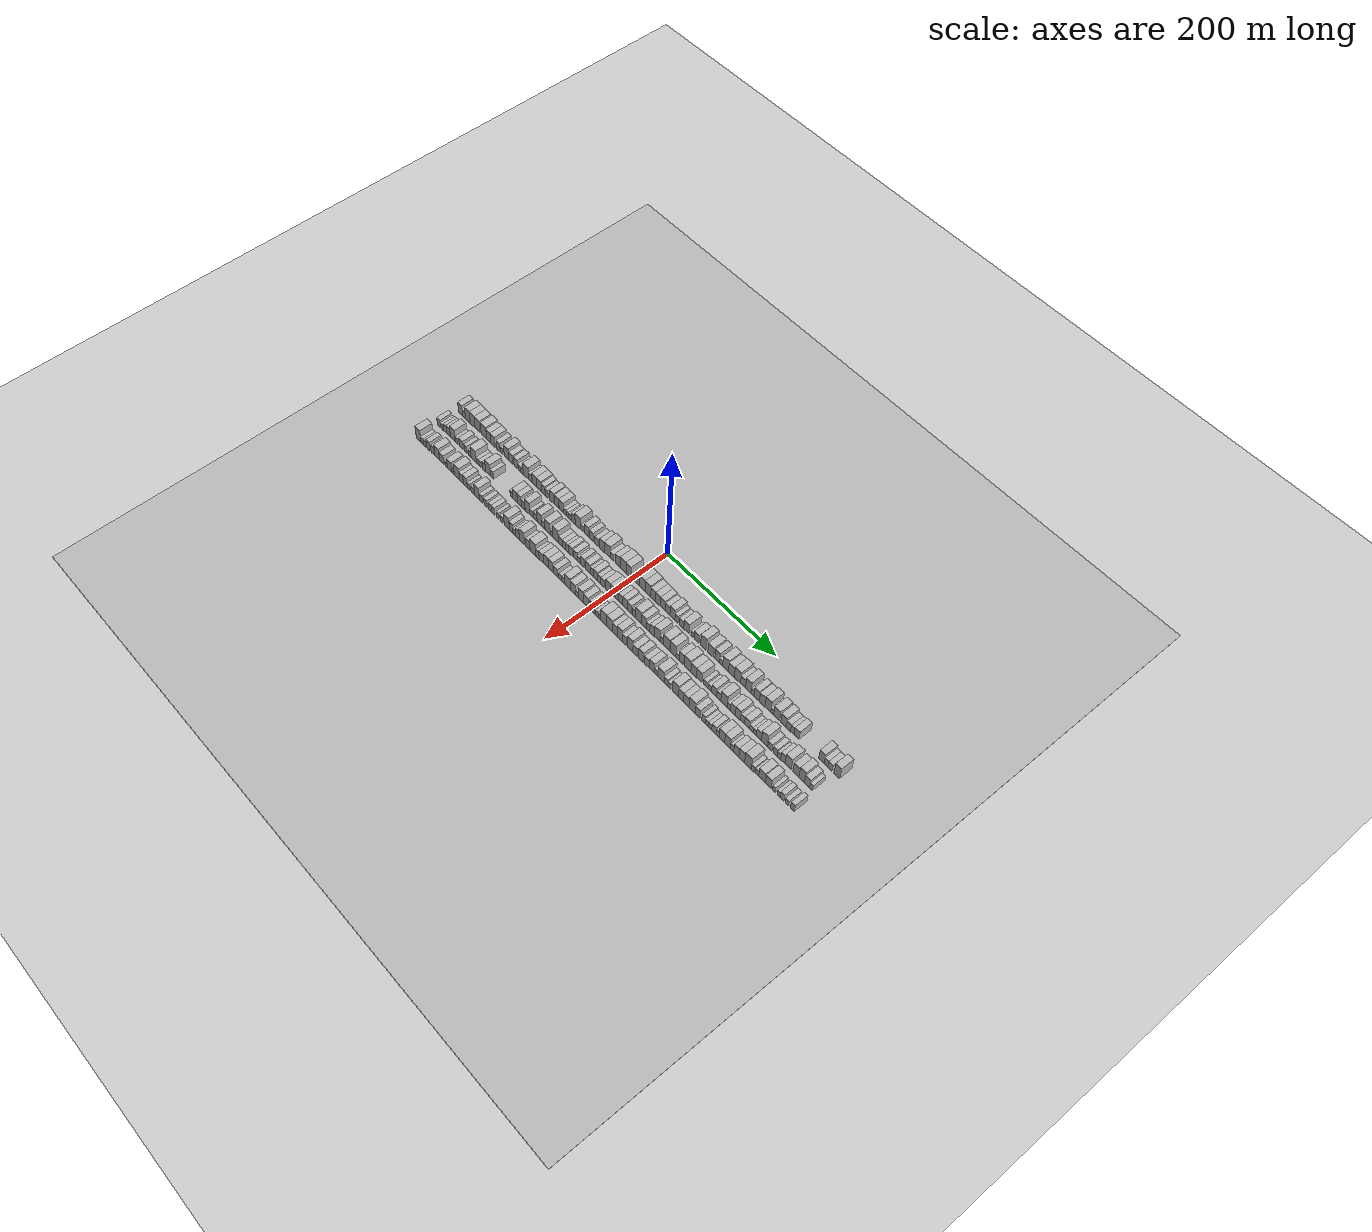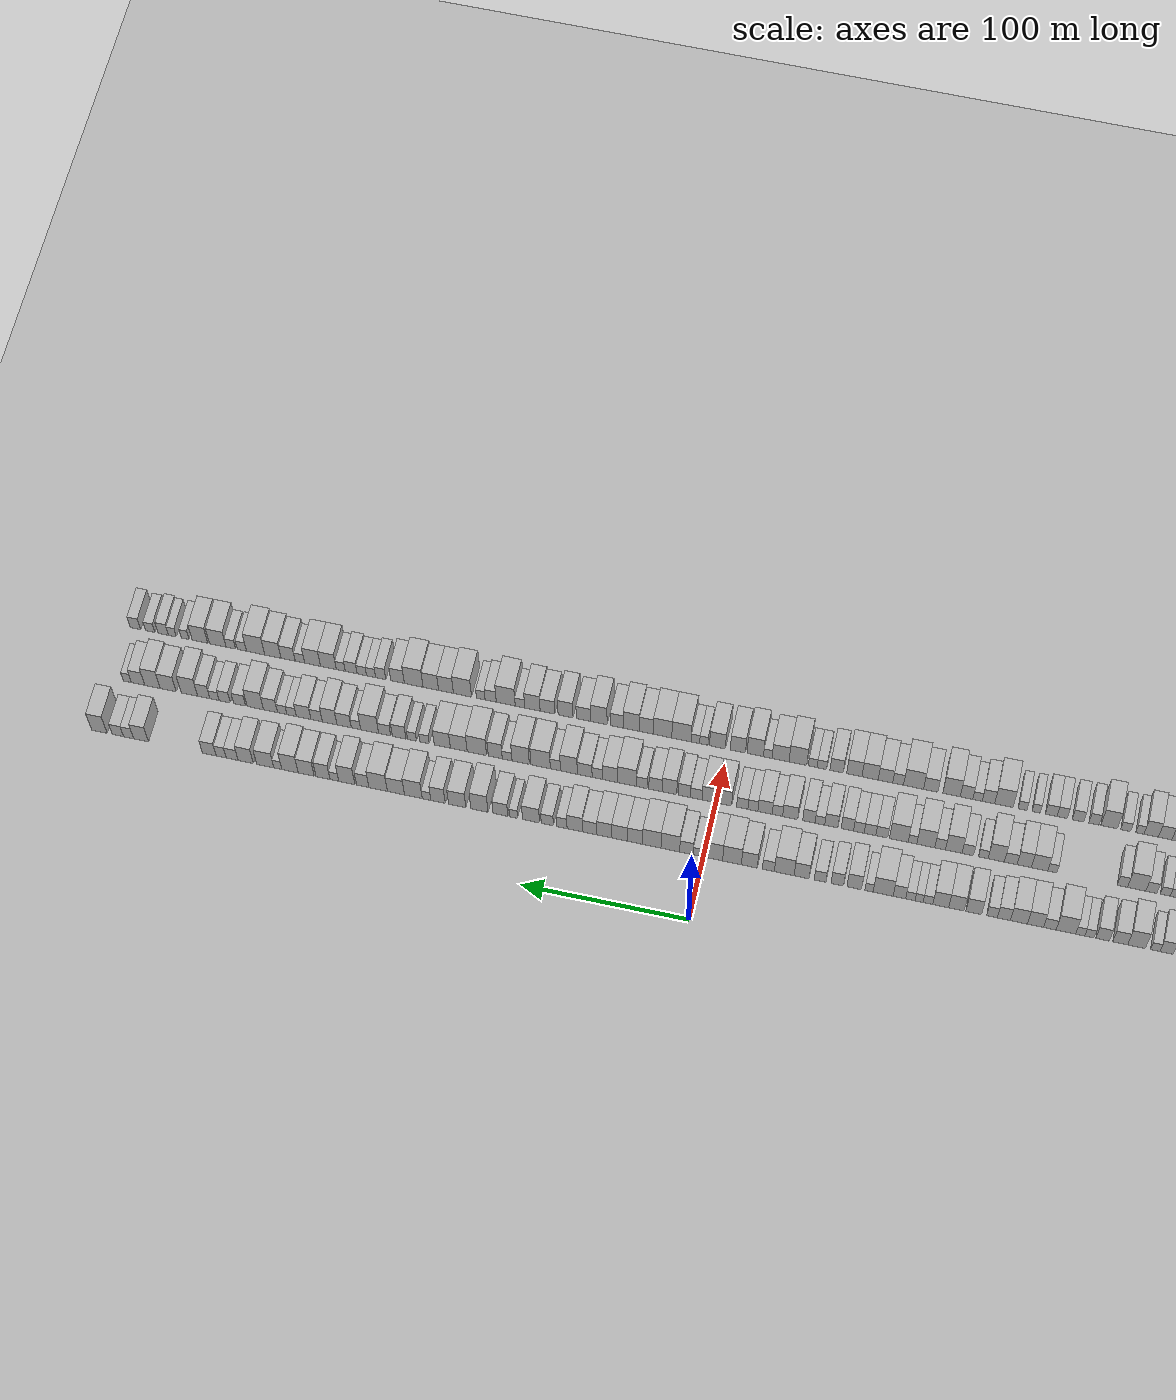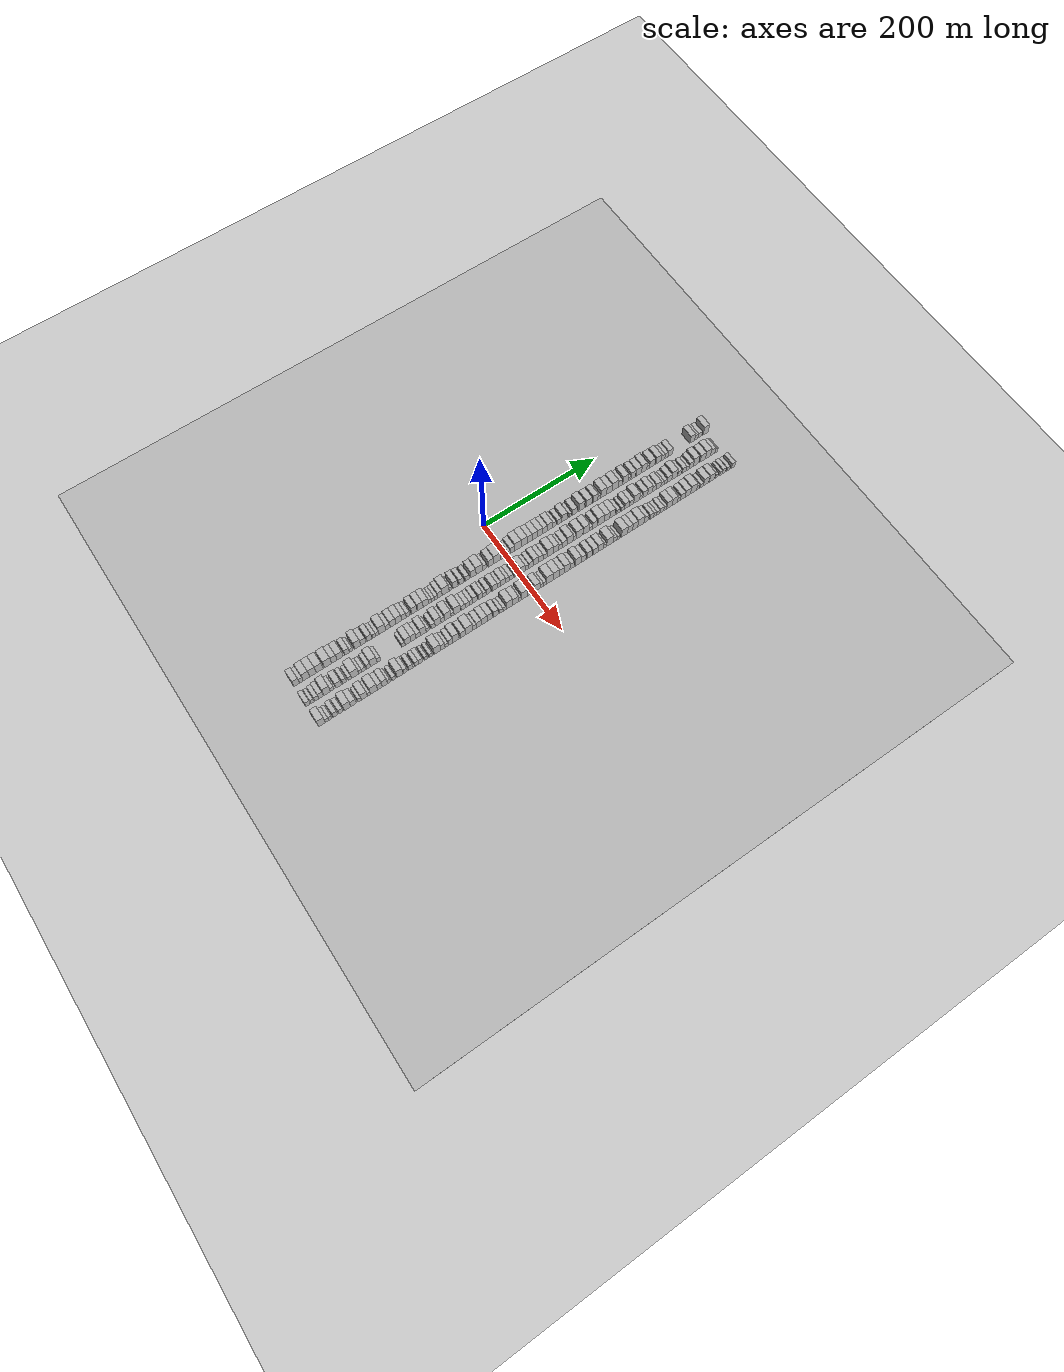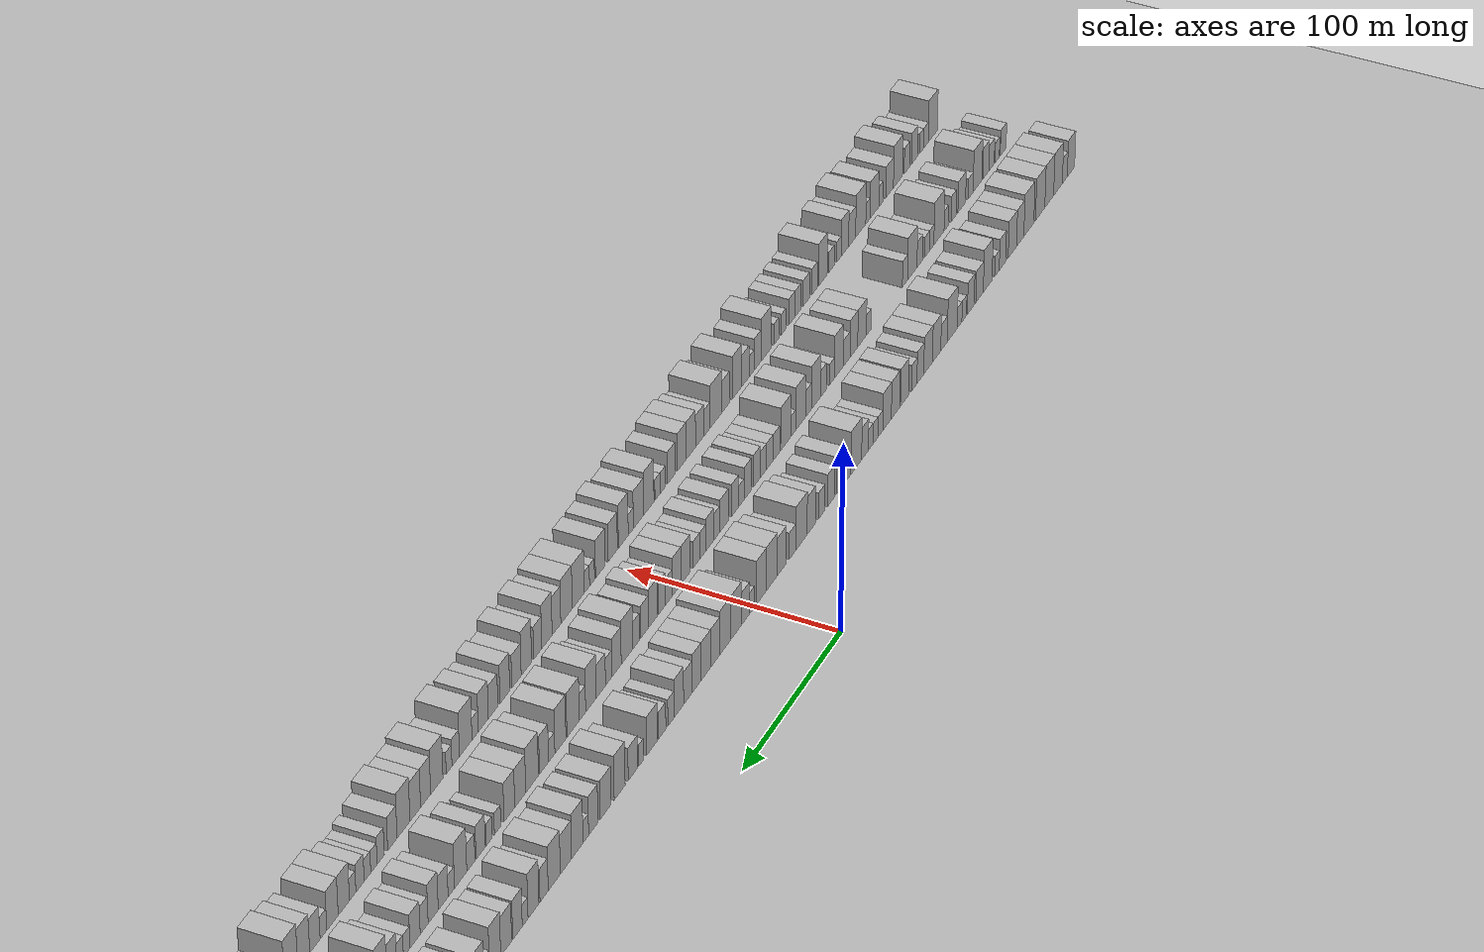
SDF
<?xml version="1.0" encoding="utf-8"?>

<sdf version="1.6">

   <world name="default">

      <gui fullscreen="0">

         <camera name="user_camera">

            <pose>-15 0 4.57585 0 0 0</pose>

            <view_controller>orbit</view_controller>

         </camera>

      </gui>

      <scene>

         <sky>

           <clouds>

             <speed>12</speed>

           </clouds>

         </sky>

         <ambient>0.4 0.4 0.4 1</ambient>

         <background>0.7 0.7 0.7 1</background>

         <shadows>1</shadows>

      </scene>

      <gravity>0 0 -9.8066</gravity>

      <magnetic_field>6e-06 2.3e-05 -4.2e-05</magnetic_field>

      <physics default="0" name="default_physics" type="ode">

         <ode>

            <solver>

               <type>quick</type>

               <iters>10</iters>

               <sor>1.0</sor>

               <use_dynamic_moi_rescaling>0</use_dynamic_moi_rescaling>

            </solver>

            <constraints>

               <cfm>0</cfm>

               <erp>0.2</erp>

               <contact_max_correcting_vel>100</contact_max_correcting_vel>

               <contact_surface_layer>0.001</contact_surface_layer>

            </constraints>

         </ode>

         <max_step_size>0.004</max_step_size>

         <real_time_factor>1</real_time_factor>

         <real_time_update_rate>250</real_time_update_rate>

      </physics>

      <light name="sun" type="directional">

         <cast_shadows>1</cast_shadows>

         <pose>0 0 10 0 0 0</pose>

         <diffuse>0.8 0.8 0.8 1</diffuse>

         <specular>0.2 0.2 0.2 1</specular>

         <attenuation>

            <range>1000</range>

            <constant>0.9</constant>

            <linear>0.01</linear>

            <quadratic>0.001</quadratic>

         </attenuation>

         <direction>-0.5 0.1 -0.9</direction>

      </light>

      <include>

         <name>ground_plane_1</name>

         <uri>model://HANNAS_ground_plane</uri>

         <pose>0 0 0  0 0 0</pose>

      </include>

      <include>

         <name>ground_plane_2</name>

         <uri>model://HANNAS_ground_plane</uri>

         <pose>100 0 0  0 0 0</pose>

      </include>

      <model name="building_1">

         <static>1</static>

         <pose frame="">50.0000 -354.4846 0 0.000000 0.000000 0.000000</pose>

         <link name="link">

            <pose frame="">0 0 10.50 0 0 0</pose>

            <collision name="collision">

               <geometry>

                  <box>

                     <size>20.0000 9.0309 21.0000</size>

                  </box>

               </geometry>

               <max_contacts>10</max_contacts>

               <surface>

                  <contact>

                     <ode/>

                  </contact>

                  <bounce/>

                  <friction>

                     <torsional>

                        <ode/>

                     </torsional>

                     <ode/>

                  </friction>

               </surface>

            </collision>

            <visual name="visual">

               <cast_shadows>0</cast_shadows>

               <geometry>

                  <box>

                     <size>20.0000 9.0309 21.0000</size>

                  </box>

               </geometry>

               <material>

                  <script>

                     <uri>model://HANNAS_wall/materials/scripts</uri>

                     <uri>model://HANNAS_wall/materials/textures</uri>

                     <name>vrc/HANNAS_wall</name>

                  </script>

               </material>

            </visual>

            <self_collide>0</self_collide>

            <enable_wind>0</enable_wind>

            <kinematic>0</kinematic>

         </link>

      </model>

      <model name="building_2">

         <static>1</static>

         <pose frame="">50.0000 -346.9367 0 0.000000 0.000000 0.000000</pose>

         <link name="link">

            <pose frame="">0 0 7.50 0 0 0</pose>

            <collision name="collision">

               <geometry>

                  <box>

                     <size>20.0000 6.0649 15.0000</size>

                  </box>

               </geometry>

               <max_contacts>10</max_contacts>

               <surface>

                  <contact>

                     <ode/>

                  </contact>

                  <bounce/>

                  <friction>

                     <torsional>

                        <ode/>

                     </torsional>

                     <ode/>

                  </friction>

               </surface>

            </collision>

            <visual name="visual">

               <cast_shadows>0</cast_shadows>

               <geometry>

                  <box>

                     <size>20.0000 6.0649 15.0000</size>

                  </box>

               </geometry>

               <material>

                  <script>

                     <uri>model://HANNAS_wall/materials/scripts</uri>

                     <uri>model://HANNAS_wall/materials/textures</uri>

                     <name>vrc/HANNAS_wall</name>

                  </script>

               </material>

            </visual>

            <self_collide>0</self_collide>

            <enable_wind>0</enable_wind>

            <kinematic>0</kinematic>

         </link>

      </model>

      <model name="building_3">

         <static>1</static>

         <pose frame="">50.0000 -338.6176 0 0.000000 0.000000 0.000000</pose>

         <link name="link">

            <pose frame="">0 0 12.00 0 0 0</pose>

            <collision name="collision">

               <geometry>

                  <box>

                     <size>20.0000 10.5732 24.0000</size>

                  </box>

               </geometry>

               <max_contacts>10</max_contacts>

               <surface>

                  <contact>

                     <ode/>

                  </contact>

                  <bounce/>

                  <friction>

                     <torsional>

                        <ode/>

                     </torsional>

                     <ode/>

                  </friction>

               </surface>

            </collision>

            <visual name="visual">

               <cast_shadows>0</cast_shadows>

               <geometry>

                  <box>

                     <size>20.0000 10.5732 24.0000</size>

                  </box>

               </geometry>

               <material>

                  <script>

                     <uri>model://HANNAS_wall/materials/scripts</uri>

                     <uri>model://HANNAS_wall/materials/textures</uri>

                     <name>vrc/HANNAS_wall</name>

                  </script>

               </material>

            </visual>

            <self_collide>0</self_collide>

            <enable_wind>0</enable_wind>

            <kinematic>0</kinematic>

         </link>

      </model>

      <model name="building_4">

         <static>1</static>

         <pose frame="">50.0000 -327.9796 0 0.000000 0.000000 0.000000</pose>

         <link name="link">

            <pose frame="">0 0 12.00 0 0 0</pose>

            <collision name="collision">

               <geometry>

                  <box>

                     <size>20.0000 10.7028 24.0000</size>

                  </box>

               </geometry>

               <max_contacts>10</max_contacts>

               <surface>

                  <contact>

                     <ode/>

                  </contact>

                  <bounce/>

                  <friction>

                     <torsional>

                        <ode/>

                     </torsional>

                     <ode/>

                  </friction>

               </surface>

            </collision>

            <visual name="visual">

               <cast_shadows>0</cast_shadows>

               <geometry>

                  <box>

                     <size>20.0000 10.7028 24.0000</size>

                  </box>

               </geometry>

               <material>

                  <script>

                     <uri>model://HANNAS_wall/materials/scripts</uri>

                     <uri>model://HANNAS_wall/materials/textures</uri>

                     <name>vrc/HANNAS_wall</name>

                  </script>

               </material>

            </visual>

            <self_collide>0</self_collide>

            <enable_wind>0</enable_wind>

            <kinematic>0</kinematic>

         </link>

      </model>

      <model name="building_5">

         <static>1</static>

         <pose frame="">50.0000 -316.9930 0 0.000000 0.000000 0.000000</pose>

         <link name="link">

            <pose frame="">0 0 12.00 0 0 0</pose>

            <collision name="collision">

               <geometry>

                  <box>

                     <size>20.0000 11.2703 24.0000</size>

                  </box>

               </geometry>

               <max_contacts>10</max_contacts>

               <surface>

                  <contact>

                     <ode/>

                  </contact>

                  <bounce/>

                  <friction>

                     <torsional>

                        <ode/>

                     </torsional>

                     <ode/>

                  </friction>

               </surface>

            </collision>

            <visual name="visual">

               <cast_shadows>0</cast_shadows>

               <geometry>

                  <box>

                     <size>20.0000 11.2703 24.0000</size>

                  </box>

               </geometry>

               <material>

                  <script>

                     <uri>model://HANNAS_wall/materials/scripts</uri>

                     <uri>model://HANNAS_wall/materials/textures</uri>

                     <name>vrc/HANNAS_wall</name>

                  </script>

               </material>

            </visual>

            <self_collide>0</self_collide>

            <enable_wind>0</enable_wind>

            <kinematic>0</kinematic>

         </link>

      </model>

      <model name="building_6">

         <static>1</static>

         <pose frame="">50.0000 -303.3786 0 0.000000 0.000000 0.000000</pose>

         <link name="link">

            <pose frame="">0 0 12.00 0 0 0</pose>

            <collision name="collision">

               <geometry>

                  <box>

                     <size>20.0000 11.9585 24.0000</size>

                  </box>

               </geometry>

               <max_contacts>10</max_contacts>

               <surface>

                  <contact>

                     <ode/>

                  </contact>

                  <bounce/>

                  <friction>

                     <torsional>

                        <ode/>

                     </torsional>

                     <ode/>

                  </friction>

               </surface>

            </collision>

            <visual name="visual">

               <cast_shadows>0</cast_shadows>

               <geometry>

                  <box>

                     <size>20.0000 11.9585 24.0000</size>

                  </box>

               </geometry>

               <material>

                  <script>

                     <uri>model://HANNAS_wall/materials/scripts</uri>

                     <uri>model://HANNAS_wall/materials/textures</uri>

                     <name>vrc/HANNAS_wall</name>

                  </script>

               </material>

            </visual>

            <self_collide>0</self_collide>

            <enable_wind>0</enable_wind>

            <kinematic>0</kinematic>

         </link>

      </model>

      <model name="building_7">

         <static>1</static>

         <pose frame="">50.0000 -293.0085 0 0.000000 0.000000 0.000000</pose>

         <link name="link">

            <pose frame="">0 0 10.50 0 0 0</pose>

            <collision name="collision">

               <geometry>

                  <box>

                     <size>20.0000 8.7817 21.0000</size>

                  </box>

               </geometry>

               <max_contacts>10</max_contacts>

               <surface>

                  <contact>

                     <ode/>

                  </contact>

                  <bounce/>

                  <friction>

                     <torsional>

                        <ode/>

                     </torsional>

                     <ode/>

                  </friction>

               </surface>

            </collision>

            <visual name="visual">

               <cast_shadows>0</cast_shadows>

               <geometry>

                  <box>

                     <size>20.0000 8.7817 21.0000</size>

                  </box>

               </geometry>

               <material>

                  <script>

                     <uri>model://HANNAS_wall/materials/scripts</uri>

                     <uri>model://HANNAS_wall/materials/textures</uri>

                     <name>vrc/HANNAS_wall</name>

                  </script>

               </material>

            </visual>

            <self_collide>0</self_collide>

            <enable_wind>0</enable_wind>

            <kinematic>0</kinematic>

         </link>

      </model>

      <model name="building_8">

         <static>1</static>

         <pose frame="">50.0000 -283.6809 0 0.000000 0.000000 0.000000</pose>

         <link name="link">

            <pose frame="">0 0 10.50 0 0 0</pose>

            <collision name="collision">

               <geometry>

                  <box>

                     <size>20.0000 9.8734 21.0000</size>

                  </box>

               </geometry>

               <max_contacts>10</max_contacts>

               <surface>

                  <contact>

                     <ode/>

                  </contact>

                  <bounce/>

                  <friction>

                     <torsional>

                        <ode/>

                     </torsional>

                     <ode/>

                  </friction>

               </surface>

            </collision>

            <visual name="visual">

               <cast_shadows>0</cast_shadows>

               <geometry>

                  <box>

                     <size>20.0000 9.8734 21.0000</size>

                  </box>

               </geometry>

               <material>

                  <script>

                     <uri>model://HANNAS_wall/materials/scripts</uri>

                     <uri>model://HANNAS_wall/materials/textures</uri>

                     <name>vrc/HANNAS_wall</name>

                  </script>

               </material>

            </visual>

            <self_collide>0</self_collide>

            <enable_wind>0</enable_wind>

            <kinematic>0</kinematic>

         </link>

      </model>

      <model name="building_9">

         <static>1</static>

         <pose frame="">50.0000 -271.9531 0 0.000000 0.000000 0.000000</pose>

         <link name="link">

            <pose frame="">0 0 9.00 0 0 0</pose>

            <collision name="collision">

               <geometry>

                  <box>

                     <size>20.0000 7.5822 18.0000</size>

                  </box>

               </geometry>

               <max_contacts>10</max_contacts>

               <surface>

                  <contact>

                     <ode/>

                  </contact>

                  <bounce/>

                  <friction>

                     <torsional>

                        <ode/>

                     </torsional>

                     <ode/>

                  </friction>

               </surface>

            </collision>

            <visual name="visual">

               <cast_shadows>0</cast_shadows>

               <geometry>

                  <box>

                     <size>20.0000 7.5822 18.0000</size>

                  </box>

               </geometry>

               <material>

                  <script>

                     <uri>model://HANNAS_wall/materials/scripts</uri>

                     <uri>model://HANNAS_wall/materials/textures</uri>

                     <name>vrc/HANNAS_wall</name>

                  </script>

               </material>

            </visual>

            <self_collide>0</self_collide>

            <enable_wind>0</enable_wind>

            <kinematic>0</kinematic>

         </link>

      </model>

      <model name="building_10">

         <static>1</static>

         <pose frame="">50.0000 -265.4090 0 0.000000 0.000000 0.000000</pose>

         <link name="link">

            <pose frame="">0 0 6.00 0 0 0</pose>

            <collision name="collision">

               <geometry>

                  <box>

                     <size>20.0000 5.5061 12.0000</size>

                  </box>

               </geometry>

               <max_contacts>10</max_contacts>

               <surface>

                  <contact>

                     <ode/>

                  </contact>

                  <bounce/>

                  <friction>

                     <torsional>

                        <ode/>

                     </torsional>

                     <ode/>

                  </friction>

               </surface>

            </collision>

            <visual name="visual">

               <cast_shadows>0</cast_shadows>

               <geometry>

                  <box>

                     <size>20.0000 5.5061 12.0000</size>

                  </box>

               </geometry>

               <material>

                  <script>

                     <uri>model://HANNAS_wall/materials/scripts</uri>

                     <uri>model://HANNAS_wall/materials/textures</uri>

                     <name>vrc/HANNAS_wall</name>

                  </script>

               </material>

            </visual>

            <self_collide>0</self_collide>

            <enable_wind>0</enable_wind>

            <kinematic>0</kinematic>

         </link>

      </model>

      <model name="building_11">

         <static>1</static>

         <pose frame="">50.0000 -254.5445 0 0.000000 0.000000 0.000000</pose>

         <link name="link">

            <pose frame="">0 0 12.00 0 0 0</pose>

            <collision name="collision">

               <geometry>

                  <box>

                     <size>20.0000 10.2230 24.0000</size>

                  </box>

               </geometry>

               <max_contacts>10</max_contacts>

               <surface>

                  <contact>

                     <ode/>

                  </contact>

                  <bounce/>

                  <friction>

                     <torsional>

                        <ode/>

                     </torsional>

                     <ode/>

                  </friction>

               </surface>

            </collision>

            <visual name="visual">

               <cast_shadows>0</cast_shadows>

               <geometry>

                  <box>

                     <size>20.0000 10.2230 24.0000</size>

                  </box>

               </geometry>

               <material>

                  <script>

                     <uri>model://HANNAS_wall/materials/scripts</uri>

                     <uri>model://HANNAS_wall/materials/textures</uri>

                     <name>vrc/HANNAS_wall</name>

                  </script>

               </material>

            </visual>

            <self_collide>0</self_collide>

            <enable_wind>0</enable_wind>

            <kinematic>0</kinematic>

         </link>

      </model>

      <model name="building_12">

         <static>1</static>

         <pose frame="">50.0000 -245.1012 0 0.000000 0.000000 0.000000</pose>

         <link name="link">

            <pose frame="">0 0 9.00 0 0 0</pose>

            <collision name="collision">

               <geometry>

                  <box>

                     <size>20.0000 8.6635 18.0000</size>

                  </box>

               </geometry>

               <max_contacts>10</max_contacts>

               <surface>

                  <contact>

                     <ode/>

                  </contact>

                  <bounce/>

                  <friction>

                     <torsional>

                        <ode/>

                     </torsional>

                     <ode/>

                  </friction>

               </surface>

            </collision>

            <visual name="visual">

               <cast_shadows>0</cast_shadows>

               <geometry>

                  <box>

                     <size>20.0000 8.6635 18.0000</size>

                  </box>

               </geometry>

               <material>

                  <script>

                     <uri>model://HANNAS_wall/materials/scripts</uri>

                     <uri>model://HANNAS_wall/materials/textures</uri>

                     <name>vrc/HANNAS_wall</name>

                  </script>

               </material>

            </visual>

            <self_collide>0</self_collide>

            <enable_wind>0</enable_wind>

            <kinematic>0</kinematic>

         </link>

      </model>

      <model name="building_13">

         <static>1</static>

         <pose frame="">50.0000 -234.8488 0 0.000000 0.000000 0.000000</pose>

         <link name="link">

            <pose frame="">0 0 9.00 0 0 0</pose>

            <collision name="collision">

               <geometry>

                  <box>

                     <size>20.0000 7.8414 18.0000</size>

                  </box>

               </geometry>

               <max_contacts>10</max_contacts>

               <surface>

                  <contact>

                     <ode/>

                  </contact>

                  <bounce/>

                  <friction>

                     <torsional>

                        <ode/>

                     </torsional>

                     <ode/>

                  </friction>

               </surface>

            </collision>

            <visual name="visual">

               <cast_shadows>0</cast_shadows>

               <geometry>

                  <box>

                     <size>20.0000 7.8414 18.0000</size>

                  </box>

               </geometry>

               <material>

                  <script>

                     <uri>model://HANNAS_wall/materials/scripts</uri>

                     <uri>model://HANNAS_wall/materials/textures</uri>

                     <name>vrc/HANNAS_wall</name>

                  </script>

               </material>

            </visual>

            <self_collide>0</self_collide>

            <enable_wind>0</enable_wind>

            <kinematic>0</kinematic>

         </link>

      </model>

      <model name="building_14">

         <static>1</static>

         <pose frame="">50.0000 -227.2313 0 0.000000 0.000000 0.000000</pose>

         <link name="link">

            <pose frame="">0 0 6.00 0 0 0</pose>

            <collision name="collision">

               <geometry>

                  <box>

                     <size>20.0000 5.3936 12.0000</size>

                  </box>

               </geometry>

               <max_contacts>10</max_contacts>

               <surface>

                  <contact>

                     <ode/>

                  </contact>

                  <bounce/>

                  <friction>

                     <torsional>

                        <ode/>

                     </torsional>

                     <ode/>

                  </friction>

               </surface>

            </collision>

            <visual name="visual">

               <cast_shadows>0</cast_shadows>

               <geometry>

                  <box>

                     <size>20.0000 5.3936 12.0000</size>

                  </box>

               </geometry>

               <material>

                  <script>

                     <uri>model://HANNAS_wall/materials/scripts</uri>

                     <uri>model://HANNAS_wall/materials/textures</uri>

                     <name>vrc/HANNAS_wall</name>

                  </script>

               </material>

            </visual>

            <self_collide>0</self_collide>

            <enable_wind>0</enable_wind>

            <kinematic>0</kinematic>

         </link>

      </model>

      <model name="building_15">

         <static>1</static>

         <pose frame="">50.0000 -221.8529 0 0.000000 0.000000 0.000000</pose>

         <link name="link">

            <pose frame="">0 0 6.00 0 0 0</pose>

            <collision name="collision">

               <geometry>

                  <box>

                     <size>20.0000 5.3632 12.0000</size>

                  </box>

               </geometry>

               <max_contacts>10</max_contacts>

               <surface>

                  <contact>

                     <ode/>

                  </contact>

                  <bounce/>

                  <friction>

                     <torsional>

                        <ode/>

                     </torsional>

                     <ode/>

                  </friction>

               </surface>

            </collision>

            <visual name="visual">

               <cast_shadows>0</cast_shadows>

               <geometry>

                  <box>

                     <size>20.0000 5.3632 12.0000</size>

                  </box>

               </geometry>

               <material>

                  <script>

                     <uri>model://HANNAS_wall/materials/scripts</uri>

                     <uri>model://HANNAS_wall/materials/textures</uri>

                     <name>vrc/HANNAS_wall</name>

                  </script>

               </material>

            </visual>

            <self_collide>0</self_collide>

            <enable_wind>0</enable_wind>

            <kinematic>0</kinematic>

         </link>

      </model>

      <model name="building_16">

         <static>1</static>

         <pose frame="">50.0000 -213.4907 0 0.000000 0.000000 0.000000</pose>

         <link name="link">

            <pose frame="">0 0 12.00 0 0 0</pose>

            <collision name="collision">

               <geometry>

                  <box>

                     <size>20.0000 11.3611 24.0000</size>

                  </box>

               </geometry>

               <max_contacts>10</max_contacts>

               <surface>

                  <contact>

                     <ode/>

                  </contact>

                  <bounce/>

                  <friction>

                     <torsional>

                        <ode/>

                     </torsional>

                     <ode/>

                  </friction>

               </surface>

            </collision>

            <visual name="visual">

               <cast_shadows>0</cast_shadows>

               <geometry>

                  <box>

                     <size>20.0000 11.3611 24.0000</size>

                  </box>

               </geometry>

               <material>

                  <script>

                     <uri>model://HANNAS_wall/materials/scripts</uri>

                     <uri>model://HANNAS_wall/materials/textures</uri>

                     <name>vrc/HANNAS_wall</name>

                  </script>

               </material>

            </visual>

            <self_collide>0</self_collide>

            <enable_wind>0</enable_wind>

            <kinematic>0</kinematic>

         </link>

      </model>

      <model name="building_17">

         <static>1</static>

         <pose frame="">50.0000 -204.1119 0 0.000000 0.000000 0.000000</pose>

         <link name="link">

            <pose frame="">0 0 7.50 0 0 0</pose>

            <collision name="collision">

               <geometry>

                  <box>

                     <size>20.0000 7.3966 15.0000</size>

                  </box>

               </geometry>

               <max_contacts>10</max_contacts>

               <surface>

                  <contact>

                     <ode/>

                  </contact>

                  <bounce/>

                  <friction>

                     <torsional>

                        <ode/>

                     </torsional>

                     <ode/>

                  </friction>

               </surface>

            </collision>

            <visual name="visual">

               <cast_shadows>0</cast_shadows>

               <geometry>

                  <box>

                     <size>20.0000 7.3966 15.0000</size>

                  </box>

               </geometry>

               <material>

                  <script>

                     <uri>model://HANNAS_wall/materials/scripts</uri>

                     <uri>model://HANNAS_wall/materials/textures</uri>

                     <name>vrc/HANNAS_wall</name>

                  </script>

               </material>

            </visual>

            <self_collide>0</self_collide>

            <enable_wind>0</enable_wind>

            <kinematic>0</kinematic>

         </link>

      </model>

      <model name="building_18">

         <static>1</static>

         <pose frame="">50.0000 -195.6882 0 0.000000 0.000000 0.000000</pose>

         <link name="link">

            <pose frame="">0 0 10.50 0 0 0</pose>

            <collision name="collision">

               <geometry>

                  <box>

                     <size>20.0000 9.4509 21.0000</size>

                  </box>

               </geometry>

               <max_contacts>10</max_contacts>

               <surface>

                  <contact>

                     <ode/>

                  </contact>

                  <bounce/>

                  <friction>

                     <torsional>

                        <ode/>

                     </torsional>

                     <ode/>

                  </friction>

               </surface>

            </collision>

            <visual name="visual">

               <cast_shadows>0</cast_shadows>

               <geometry>

                  <box>

                     <size>20.0000 9.4509 21.0000</size>

                  </box>

               </geometry>

               <material>

                  <script>

                     <uri>model://HANNAS_wall/materials/scripts</uri>

                     <uri>model://HANNAS_wall/materials/textures</uri>

                     <name>vrc/HANNAS_wall</name>

                  </script>

               </material>

            </visual>

            <self_collide>0</self_collide>

            <enable_wind>0</enable_wind>

            <kinematic>0</kinematic>

         </link>

      </model>

      <model name="building_19">

         <static>1</static>

         <pose frame="">50.0000 -186.0301 0 0.000000 0.000000 0.000000</pose>

         <link name="link">

            <pose frame="">0 0 10.50 0 0 0</pose>

            <collision name="collision">

               <geometry>

                  <box>

                     <size>20.0000 9.8652 21.0000</size>

                  </box>

               </geometry>

               <max_contacts>10</max_contacts>

               <surface>

                  <contact>

                     <ode/>

                  </contact>

                  <bounce/>

                  <friction>

                     <torsional>

                        <ode/>

                     </torsional>

                     <ode/>

                  </friction>

               </surface>

            </collision>

            <visual name="visual">

               <cast_shadows>0</cast_shadows>

               <geometry>

                  <box>

                     <size>20.0000 9.8652 21.0000</size>

                  </box>

               </geometry>

               <material>

                  <script>

                     <uri>model://HANNAS_wall/materials/scripts</uri>

                     <uri>model://HANNAS_wall/materials/textures</uri>

                     <name>vrc/HANNAS_wall</name>

                  </script>

               </material>

            </visual>

            <self_collide>0</self_collide>

            <enable_wind>0</enable_wind>

            <kinematic>0</kinematic>

         </link>

      </model>

      <model name="building_20">

         <static>1</static>

         <pose frame="">50.0000 -177.2665 0 0.000000 0.000000 0.000000</pose>

         <link name="link">

            <pose frame="">0 0 9.00 0 0 0</pose>

            <collision name="collision">

               <geometry>

                  <box>

                     <size>20.0000 7.6620 18.0000</size>

                  </box>

               </geometry>

               <max_contacts>10</max_contacts>

               <surface>

                  <contact>

                     <ode/>

                  </contact>

                  <bounce/>

                  <friction>

                     <torsional>

                        <ode/>

                     </torsional>

                     <ode/>

                  </friction>

               </surface>

            </collision>

            <visual name="visual">

               <cast_shadows>0</cast_shadows>

               <geometry>

                  <box>

                     <size>20.0000 7.6620 18.0000</size>

                  </box>

               </geometry>

               <material>

                  <script>

                     <uri>model://HANNAS_wall/materials/scripts</uri>

                     <uri>model://HANNAS_wall/materials/textures</uri>

                     <name>vrc/HANNAS_wall</name>

                  </script>

               </material>

            </visual>

            <self_collide>0</self_collide>

            <enable_wind>0</enable_wind>

            <kinematic>0</kinematic>

         </link>

      </model>

      <model name="building_21">

         <static>1</static>

         <pose frame="">50.0000 -170.3118 0 0.000000 0.000000 0.000000</pose>

         <link name="link">

            <pose frame="">0 0 7.50 0 0 0</pose>

            <collision name="collision">

               <geometry>

                  <box>

                     <size>20.0000 6.2473 15.0000</size>

                  </box>

               </geometry>

               <max_contacts>10</max_contacts>

               <surface>

                  <contact>

                     <ode/>

                  </contact>

                  <bounce/>

                  <friction>

                     <torsional>

                        <ode/>

                     </torsional>

                     <ode/>

                  </friction>

               </surface>

            </collision>

            <visual name="visual">

               <cast_shadows>0</cast_shadows>

               <geometry>

                  <box>

                     <size>20.0000 6.2473 15.0000</size>

                  </box>

               </geometry>

               <material>

                  <script>

                     <uri>model://HANNAS_wall/materials/scripts</uri>

                     <uri>model://HANNAS_wall/materials/textures</uri>

                     <name>vrc/HANNAS_wall</name>

                  </script>

               </material>

            </visual>

            <self_collide>0</self_collide>

            <enable_wind>0</enable_wind>

            <kinematic>0</kinematic>

         </link>

      </model>

      <model name="building_22">

         <static>1</static>

         <pose frame="">50.0000 -159.5734 0 0.000000 0.000000 0.000000</pose>

         <link name="link">

            <pose frame="">0 0 10.50 0 0 0</pose>

            <collision name="collision">

               <geometry>

                  <box>

                     <size>20.0000 9.2295 21.0000</size>

                  </box>

               </geometry>

               <max_contacts>10</max_contacts>

               <surface>

                  <contact>

                     <ode/>

                  </contact>

                  <bounce/>

                  <friction>

                     <torsional>

                        <ode/>

                     </torsional>

                     <ode/>

                  </friction>

               </surface>

            </collision>

            <visual name="visual">

               <cast_shadows>0</cast_shadows>

               <geometry>

                  <box>

                     <size>20.0000 9.2295 21.0000</size>

                  </box>

               </geometry>

               <material>

                  <script>

                     <uri>model://HANNAS_wall/materials/scripts</uri>

                     <uri>model://HANNAS_wall/materials/textures</uri>

                     <name>vrc/HANNAS_wall</name>

                  </script>

               </material>

            </visual>

            <self_collide>0</self_collide>

            <enable_wind>0</enable_wind>

            <kinematic>0</kinematic>

         </link>

      </model>

      <model name="building_23">

         <static>1</static>

         <pose frame="">50.0000 -149.4023 0 0.000000 0.000000 0.000000</pose>

         <link name="link">

            <pose frame="">0 0 10.50 0 0 0</pose>

            <collision name="collision">

               <geometry>

                  <box>

                     <size>20.0000 9.1128 21.0000</size>

                  </box>

               </geometry>

               <max_contacts>10</max_contacts>

               <surface>

                  <contact>

                     <ode/>

                  </contact>

                  <bounce/>

                  <friction>

                     <torsional>

                        <ode/>

                     </torsional>

                     <ode/>

                  </friction>

               </surface>

            </collision>

            <visual name="visual">

               <cast_shadows>0</cast_shadows>

               <geometry>

                  <box>

                     <size>20.0000 9.1128 21.0000</size>

                  </box>

               </geometry>

               <material>

                  <script>

                     <uri>model://HANNAS_wall/materials/scripts</uri>

                     <uri>model://HANNAS_wall/materials/textures</uri>

                     <name>vrc/HANNAS_wall</name>

                  </script>

               </material>

            </visual>

            <self_collide>0</self_collide>

            <enable_wind>0</enable_wind>

            <kinematic>0</kinematic>

         </link>

      </model>

      <model name="building_24">

         <static>1</static>

         <pose frame="">50.0000 -140.2071 0 0.000000 0.000000 0.000000</pose>

         <link name="link">

            <pose frame="">0 0 10.50 0 0 0</pose>

            <collision name="collision">

               <geometry>

                  <box>

                     <size>20.0000 9.2776 21.0000</size>

                  </box>

               </geometry>

               <max_contacts>10</max_contacts>

               <surface>

                  <contact>

                     <ode/>

                  </contact>

                  <bounce/>

                  <friction>

                     <torsional>

                        <ode/>

                     </torsional>

                     <ode/>

                  </friction>

               </surface>

            </collision>

            <visual name="visual">

               <cast_shadows>0</cast_shadows>

               <geometry>

                  <box>

                     <size>20.0000 9.2776 21.0000</size>

                  </box>

               </geometry>

               <material>

                  <script>

                     <uri>model://HANNAS_wall/materials/scripts</uri>

                     <uri>model://HANNAS_wall/materials/textures</uri>

                     <name>vrc/HANNAS_wall</name>

                  </script>

               </material>

            </visual>

            <self_collide>0</self_collide>

            <enable_wind>0</enable_wind>

            <kinematic>0</kinematic>

         </link>

      </model>

      <model name="building_25">

         <static>1</static>

         <pose frame="">50.0000 -132.7250 0 0.000000 0.000000 0.000000</pose>

         <link name="link">

            <pose frame="">0 0 6.00 0 0 0</pose>

            <collision name="collision">

               <geometry>

                  <box>

                     <size>20.0000 5.6866 12.0000</size>

                  </box>

               </geometry>

               <max_contacts>10</max_contacts>

               <surface>

                  <contact>

                     <ode/>

                  </contact>

                  <bounce/>

                  <friction>

                     <torsional>

                        <ode/>

                     </torsional>

                     <ode/>

                  </friction>

               </surface>

            </collision>

            <visual name="visual">

               <cast_shadows>0</cast_shadows>

               <geometry>

                  <box>

                     <size>20.0000 5.6866 12.0000</size>

                  </box>

               </geometry>

               <material>

                  <script>

                     <uri>model://HANNAS_wall/materials/scripts</uri>

                     <uri>model://HANNAS_wall/materials/textures</uri>

                     <name>vrc/HANNAS_wall</name>

                  </script>

               </material>

            </visual>

            <self_collide>0</self_collide>

            <enable_wind>0</enable_wind>

            <kinematic>0</kinematic>

         </link>

      </model>

      <model name="building_26">

         <static>1</static>

         <pose frame="">50.0000 -127.4625 0 0.000000 0.000000 0.000000</pose>

         <link name="link">

            <pose frame="">0 0 6.00 0 0 0</pose>

            <collision name="collision">

               <geometry>

                  <box>

                     <size>20.0000 4.8385 12.0000</size>

                  </box>

               </geometry>

               <max_contacts>10</max_contacts>

               <surface>

                  <contact>

                     <ode/>

                  </contact>

                  <bounce/>

                  <friction>

                     <torsional>

                        <ode/>

                     </torsional>

                     <ode/>

                  </friction>

               </surface>

            </collision>

            <visual name="visual">

               <cast_shadows>0</cast_shadows>

               <geometry>

                  <box>

                     <size>20.0000 4.8385 12.0000</size>

                  </box>

               </geometry>

               <material>

                  <script>

                     <uri>model://HANNAS_wall/materials/scripts</uri>

                     <uri>model://HANNAS_wall/materials/textures</uri>

                     <name>vrc/HANNAS_wall</name>

                  </script>

               </material>

            </visual>

            <self_collide>0</self_collide>

            <enable_wind>0</enable_wind>

            <kinematic>0</kinematic>

         </link>

      </model>

      <model name="building_27">

         <static>1</static>

         <pose frame="">50.0000 -122.3108 0 0.000000 0.000000 0.000000</pose>

         <link name="link">

            <pose frame="">0 0 6.00 0 0 0</pose>

            <collision name="collision">

               <geometry>

                  <box>

                     <size>20.0000 5.4649 12.0000</size>

                  </box>

               </geometry>

               <max_contacts>10</max_contacts>

               <surface>

                  <contact>

                     <ode/>

                  </contact>

                  <bounce/>

                  <friction>

                     <torsional>

                        <ode/>

                     </torsional>

                     <ode/>

                  </friction>

               </surface>

            </collision>

            <visual name="visual">

               <cast_shadows>0</cast_shadows>

               <geometry>

                  <box>

                     <size>20.0000 5.4649 12.0000</size>

                  </box>

               </geometry>

               <material>

                  <script>

                     <uri>model://HANNAS_wall/materials/scripts</uri>

                     <uri>model://HANNAS_wall/materials/textures</uri>

                     <name>vrc/HANNAS_wall</name>

                  </script>

               </material>

            </visual>

            <self_collide>0</self_collide>

            <enable_wind>0</enable_wind>

            <kinematic>0</kinematic>

         </link>

      </model>

      <model name="building_28">

         <static>1</static>

         <pose frame="">50.0000 -115.8985 0 0.000000 0.000000 0.000000</pose>

         <link name="link">

            <pose frame="">0 0 9.00 0 0 0</pose>

            <collision name="collision">

               <geometry>

                  <box>

                     <size>20.0000 7.3597 18.0000</size>

                  </box>

               </geometry>

               <max_contacts>10</max_contacts>

               <surface>

                  <contact>

                     <ode/>

                  </contact>

                  <bounce/>

                  <friction>

                     <torsional>

                        <ode/>

                     </torsional>

                     <ode/>

                  </friction>

               </surface>

            </collision>

            <visual name="visual">

               <cast_shadows>0</cast_shadows>

               <geometry>

                  <box>

                     <size>20.0000 7.3597 18.0000</size>

                  </box>

               </geometry>

               <material>

                  <script>

                     <uri>model://HANNAS_wall/materials/scripts</uri>

                     <uri>model://HANNAS_wall/materials/textures</uri>

                     <name>vrc/HANNAS_wall</name>

                  </script>

               </material>

            </visual>

            <self_collide>0</self_collide>

            <enable_wind>0</enable_wind>

            <kinematic>0</kinematic>

         </link>

      </model>

      <model name="building_29">

         <static>1</static>

         <pose frame="">50.0000 -106.3487 0 0.000000 0.000000 0.000000</pose>

         <link name="link">

            <pose frame="">0 0 12.00 0 0 0</pose>

            <collision name="collision">

               <geometry>

                  <box>

                     <size>20.0000 11.7398 24.0000</size>

                  </box>

               </geometry>

               <max_contacts>10</max_contacts>

               <surface>

                  <contact>

                     <ode/>

                  </contact>

                  <bounce/>

                  <friction>

                     <torsional>

                        <ode/>

                     </torsional>

                     <ode/>

                  </friction>

               </surface>

            </collision>

            <visual name="visual">

               <cast_shadows>0</cast_shadows>

               <geometry>

                  <box>

                     <size>20.0000 11.7398 24.0000</size>

                  </box>

               </geometry>

               <material>

                  <script>

                     <uri>model://HANNAS_wall/materials/scripts</uri>

                     <uri>model://HANNAS_wall/materials/textures</uri>

                     <name>vrc/HANNAS_wall</name>

                  </script>

               </material>

            </visual>

            <self_collide>0</self_collide>

            <enable_wind>0</enable_wind>

            <kinematic>0</kinematic>

         </link>

      </model>

      <model name="building_30">

         <static>1</static>

         <pose frame="">50.0000 -98.0165 0 0.000000 0.000000 0.000000</pose>

         <link name="link">

            <pose frame="">0 0 6.00 0 0 0</pose>

            <collision name="collision">

               <geometry>

                  <box>

                     <size>20.0000 4.9245 12.0000</size>

                  </box>

               </geometry>

               <max_contacts>10</max_contacts>

               <surface>

                  <contact>

                     <ode/>

                  </contact>

                  <bounce/>

                  <friction>

                     <torsional>

                        <ode/>

                     </torsional>

                     <ode/>

                  </friction>

               </surface>

            </collision>

            <visual name="visual">

               <cast_shadows>0</cast_shadows>

               <geometry>

                  <box>

                     <size>20.0000 4.9245 12.0000</size>

                  </box>

               </geometry>

               <material>

                  <script>

                     <uri>model://HANNAS_wall/materials/scripts</uri>

                     <uri>model://HANNAS_wall/materials/textures</uri>

                     <name>vrc/HANNAS_wall</name>

                  </script>

               </material>

            </visual>

            <self_collide>0</self_collide>

            <enable_wind>0</enable_wind>

            <kinematic>0</kinematic>

         </link>

      </model>

      <model name="building_31">

         <static>1</static>

         <pose frame="">50.0000 -89.2858 0 0.000000 0.000000 0.000000</pose>

         <link name="link">

            <pose frame="">0 0 10.50 0 0 0</pose>

            <collision name="collision">

               <geometry>

                  <box>

                     <size>20.0000 8.5370 21.0000</size>

                  </box>

               </geometry>

               <max_contacts>10</max_contacts>

               <surface>

                  <contact>

                     <ode/>

                  </contact>

                  <bounce/>

                  <friction>

                     <torsional>

                        <ode/>

                     </torsional>

                     <ode/>

                  </friction>

               </surface>

            </collision>

            <visual name="visual">

               <cast_shadows>0</cast_shadows>

               <geometry>

                  <box>

                     <size>20.0000 8.5370 21.0000</size>

                  </box>

               </geometry>

               <material>

                  <script>

                     <uri>model://HANNAS_wall/materials/scripts</uri>

                     <uri>model://HANNAS_wall/materials/textures</uri>

                     <name>vrc/HANNAS_wall</name>

                  </script>

               </material>

            </visual>

            <self_collide>0</self_collide>

            <enable_wind>0</enable_wind>

            <kinematic>0</kinematic>

         </link>

      </model>

      <model name="building_32">

         <static>1</static>

         <pose frame="">50.0000 -79.3101 0 0.000000 0.000000 0.000000</pose>

         <link name="link">

            <pose frame="">0 0 9.00 0 0 0</pose>

            <collision name="collision">

               <geometry>

                  <box>

                     <size>20.0000 7.4142 18.0000</size>

                  </box>

               </geometry>

               <max_contacts>10</max_contacts>

               <surface>

                  <contact>

                     <ode/>

                  </contact>

                  <bounce/>

                  <friction>

                     <torsional>

                        <ode/>

                     </torsional>

                     <ode/>

                  </friction>

               </surface>

            </collision>

            <visual name="visual">

               <cast_shadows>0</cast_shadows>

               <geometry>

                  <box>

                     <size>20.0000 7.4142 18.0000</size>

                  </box>

               </geometry>

               <material>

                  <script>

                     <uri>model://HANNAS_wall/materials/scripts</uri>

                     <uri>model://HANNAS_wall/materials/textures</uri>

                     <name>vrc/HANNAS_wall</name>

                  </script>

               </material>

            </visual>

            <self_collide>0</self_collide>

            <enable_wind>0</enable_wind>

            <kinematic>0</kinematic>

         </link>

      </model>

      <model name="building_33">

         <static>1</static>

         <pose frame="">50.0000 -69.1158 0 0.000000 0.000000 0.000000</pose>

         <link name="link">

            <pose frame="">0 0 7.50 0 0 0</pose>

            <collision name="collision">

               <geometry>

                  <box>

                     <size>20.0000 6.9746 15.0000</size>

                  </box>

               </geometry>

               <max_contacts>10</max_contacts>

               <surface>

                  <contact>

                     <ode/>

                  </contact>

                  <bounce/>

                  <friction>

                     <torsional>

                        <ode/>

                     </torsional>

                     <ode/>

                  </friction>

               </surface>

            </collision>

            <visual name="visual">

               <cast_shadows>0</cast_shadows>

               <geometry>

                  <box>

                     <size>20.0000 6.9746 15.0000</size>

                  </box>

               </geometry>

               <material>

                  <script>

                     <uri>model://HANNAS_wall/materials/scripts</uri>

                     <uri>model://HANNAS_wall/materials/textures</uri>

                     <name>vrc/HANNAS_wall</name>

                  </script>

               </material>

            </visual>

            <self_collide>0</self_collide>

            <enable_wind>0</enable_wind>

            <kinematic>0</kinematic>

         </link>

      </model>

      <model name="building_34">

         <static>1</static>

         <pose frame="">50.0000 -58.2032 0 0.000000 0.000000 0.000000</pose>

         <link name="link">

            <pose frame="">0 0 10.50 0 0 0</pose>

            <collision name="collision">

               <geometry>

                  <box>

                     <size>20.0000 8.8505 21.0000</size>

                  </box>

               </geometry>

               <max_contacts>10</max_contacts>

               <surface>

                  <contact>

                     <ode/>

                  </contact>

                  <bounce/>

                  <friction>

                     <torsional>

                        <ode/>

                     </torsional>

                     <ode/>

                  </friction>

               </surface>

            </collision>

            <visual name="visual">

               <cast_shadows>0</cast_shadows>

               <geometry>

                  <box>

                     <size>20.0000 8.8505 21.0000</size>

                  </box>

               </geometry>

               <material>

                  <script>

                     <uri>model://HANNAS_wall/materials/scripts</uri>

                     <uri>model://HANNAS_wall/materials/textures</uri>

                     <name>vrc/HANNAS_wall</name>

                  </script>

               </material>

            </visual>

            <self_collide>0</self_collide>

            <enable_wind>0</enable_wind>

            <kinematic>0</kinematic>

         </link>

      </model>

      <model name="building_35">

         <static>1</static>

         <pose frame="">50.0000 -47.9410 0 0.000000 0.000000 0.000000</pose>

         <link name="link">

            <pose frame="">0 0 12.00 0 0 0</pose>

            <collision name="collision">

               <geometry>

                  <box>

                     <size>20.0000 11.6740 24.0000</size>

                  </box>

               </geometry>

               <max_contacts>10</max_contacts>

               <surface>

                  <contact>

                     <ode/>

                  </contact>

                  <bounce/>

                  <friction>

                     <torsional>

                        <ode/>

                     </torsional>

                     <ode/>

                  </friction>

               </surface>

            </collision>

            <visual name="visual">

               <cast_shadows>0</cast_shadows>

               <geometry>

                  <box>

                     <size>20.0000 11.6740 24.0000</size>

                  </box>

               </geometry>

               <material>

                  <script>

                     <uri>model://HANNAS_wall/materials/scripts</uri>

                     <uri>model://HANNAS_wall/materials/textures</uri>

                     <name>vrc/HANNAS_wall</name>

                  </script>

               </material>

            </visual>

            <self_collide>0</self_collide>

            <enable_wind>0</enable_wind>

            <kinematic>0</kinematic>

         </link>

      </model>

      <model name="building_36">

         <static>1</static>

         <pose frame="">50.0000 -38.5350 0 0.000000 0.000000 0.000000</pose>

         <link name="link">

            <pose frame="">0 0 7.50 0 0 0</pose>

            <collision name="collision">

               <geometry>

                  <box>

                     <size>20.0000 7.1380 15.0000</size>

                  </box>

               </geometry>

               <max_contacts>10</max_contacts>

               <surface>

                  <contact>

                     <ode/>

                  </contact>

                  <bounce/>

                  <friction>

                     <torsional>

                        <ode/>

                     </torsional>

                     <ode/>

                  </friction>

               </surface>

            </collision>

            <visual name="visual">

               <cast_shadows>0</cast_shadows>

               <geometry>

                  <box>

                     <size>20.0000 7.1380 15.0000</size>

                  </box>

               </geometry>

               <material>

                  <script>

                     <uri>model://HANNAS_wall/materials/scripts</uri>

                     <uri>model://HANNAS_wall/materials/textures</uri>

                     <name>vrc/HANNAS_wall</name>

                  </script>

               </material>

            </visual>

            <self_collide>0</self_collide>

            <enable_wind>0</enable_wind>

            <kinematic>0</kinematic>

         </link>

      </model>

      <model name="building_37">

         <static>1</static>

         <pose frame="">50.0000 -27.2433 0 0.000000 0.000000 0.000000</pose>

         <link name="link">

            <pose frame="">0 0 10.50 0 0 0</pose>

            <collision name="collision">

               <geometry>

                  <box>

                     <size>20.0000 9.4455 21.0000</size>

                  </box>

               </geometry>

               <max_contacts>10</max_contacts>

               <surface>

                  <contact>

                     <ode/>

                  </contact>

                  <bounce/>

                  <friction>

                     <torsional>

                        <ode/>

                     </torsional>

                     <ode/>

                  </friction>

               </surface>

            </collision>

            <visual name="visual">

               <cast_shadows>0</cast_shadows>

               <geometry>

                  <box>

                     <size>20.0000 9.4455 21.0000</size>

                  </box>

               </geometry>

               <material>

                  <script>

                     <uri>model://HANNAS_wall/materials/scripts</uri>

                     <uri>model://HANNAS_wall/materials/textures</uri>

                     <name>vrc/HANNAS_wall</name>

                  </script>

               </material>

            </visual>

            <self_collide>0</self_collide>

            <enable_wind>0</enable_wind>

            <kinematic>0</kinematic>

         </link>

      </model>

      <model name="building_38">

         <static>1</static>

         <pose frame="">50.0000 -16.9282 0 0.000000 0.000000 0.000000</pose>

         <link name="link">

            <pose frame="">0 0 12.00 0 0 0</pose>

            <collision name="collision">

               <geometry>

                  <box>

                     <size>20.0000 11.1846 24.0000</size>

                  </box>

               </geometry>

               <max_contacts>10</max_contacts>

               <surface>

                  <contact>

                     <ode/>

                  </contact>

                  <bounce/>

                  <friction>

                     <torsional>

                        <ode/>

                     </torsional>

                     <ode/>

                  </friction>

               </surface>

            </collision>

            <visual name="visual">

               <cast_shadows>0</cast_shadows>

               <geometry>

                  <box>

                     <size>20.0000 11.1846 24.0000</size>

                  </box>

               </geometry>

               <material>

                  <script>

                     <uri>model://HANNAS_wall/materials/scripts</uri>

                     <uri>model://HANNAS_wall/materials/textures</uri>

                     <name>vrc/HANNAS_wall</name>

                  </script>

               </material>

            </visual>

            <self_collide>0</self_collide>

            <enable_wind>0</enable_wind>

            <kinematic>0</kinematic>

         </link>

      </model>

      <model name="building_39">

         <static>1</static>

         <pose frame="">50.0000 -6.1731 0 0.000000 0.000000 0.000000</pose>

         <link name="link">

            <pose frame="">0 0 12.00 0 0 0</pose>

            <collision name="collision">

               <geometry>

                  <box>

                     <size>20.0000 10.3255 24.0000</size>

                  </box>

               </geometry>

               <max_contacts>10</max_contacts>

               <surface>

                  <contact>

                     <ode/>

                  </contact>

                  <bounce/>

                  <friction>

                     <torsional>

                        <ode/>

                     </torsional>

                     <ode/>

                  </friction>

               </surface>

            </collision>

            <visual name="visual">

               <cast_shadows>0</cast_shadows>

               <geometry>

                  <box>

                     <size>20.0000 10.3255 24.0000</size>

                  </box>

               </geometry>

               <material>

                  <script>

                     <uri>model://HANNAS_wall/materials/scripts</uri>

                     <uri>model://HANNAS_wall/materials/textures</uri>

                     <name>vrc/HANNAS_wall</name>

                  </script>

               </material>

            </visual>

            <self_collide>0</self_collide>

            <enable_wind>0</enable_wind>

            <kinematic>0</kinematic>

         </link>

      </model>

      <model name="building_40">

         <static>1</static>

         <pose frame="">50.0000 3.6072 0 0.000000 0.000000 0.000000</pose>

         <link name="link">

            <pose frame="">0 0 6.00 0 0 0</pose>

            <collision name="collision">

               <geometry>

                  <box>

                     <size>20.0000 5.2352 12.0000</size>

                  </box>

               </geometry>

               <max_contacts>10</max_contacts>

               <surface>

                  <contact>

                     <ode/>

                  </contact>

                  <bounce/>

                  <friction>

                     <torsional>

                        <ode/>

                     </torsional>

                     <ode/>

                  </friction>

               </surface>

            </collision>

            <visual name="visual">

               <cast_shadows>0</cast_shadows>

               <geometry>

                  <box>

                     <size>20.0000 5.2352 12.0000</size>

                  </box>

               </geometry>

               <material>

                  <script>

                     <uri>model://HANNAS_wall/materials/scripts</uri>

                     <uri>model://HANNAS_wall/materials/textures</uri>

                     <name>vrc/HANNAS_wall</name>

                  </script>

               </material>

            </visual>

            <self_collide>0</self_collide>

            <enable_wind>0</enable_wind>

            <kinematic>0</kinematic>

         </link>

      </model>

      <model name="building_41">

         <static>1</static>

         <pose frame="">50.0000 10.2291 0 0.000000 0.000000 0.000000</pose>

         <link name="link">

            <pose frame="">0 0 9.00 0 0 0</pose>

            <collision name="collision">

               <geometry>

                  <box>

                     <size>20.0000 8.0086 18.0000</size>

                  </box>

               </geometry>

               <max_contacts>10</max_contacts>

               <surface>

                  <contact>

                     <ode/>

                  </contact>

                  <bounce/>

                  <friction>

                     <torsional>

                        <ode/>

                     </torsional>

                     <ode/>

                  </friction>

               </surface>

            </collision>

            <visual name="visual">

               <cast_shadows>0</cast_shadows>

               <geometry>

                  <box>

                     <size>20.0000 8.0086 18.0000</size>

                  </box>

               </geometry>

               <material>

                  <script>

                     <uri>model://HANNAS_wall/materials/scripts</uri>

                     <uri>model://HANNAS_wall/materials/textures</uri>

                     <name>vrc/HANNAS_wall</name>

                  </script>

               </material>

            </visual>

            <self_collide>0</self_collide>

            <enable_wind>0</enable_wind>

            <kinematic>0</kinematic>

         </link>

      </model>

      <model name="building_42">

         <static>1</static>

         <pose frame="">50.0000 19.8303 0 0.000000 0.000000 0.000000</pose>

         <link name="link">

            <pose frame="">0 0 12.00 0 0 0</pose>

            <collision name="collision">

               <geometry>

                  <box>

                     <size>20.0000 11.1937 24.0000</size>

                  </box>

               </geometry>

               <max_contacts>10</max_contacts>

               <surface>

                  <contact>

                     <ode/>

                  </contact>

                  <bounce/>

                  <friction>

                     <torsional>

                        <ode/>

                     </torsional>

                     <ode/>

                  </friction>

               </surface>

            </collision>

            <visual name="visual">

               <cast_shadows>0</cast_shadows>

               <geometry>

                  <box>

                     <size>20.0000 11.1937 24.0000</size>

                  </box>

               </geometry>

               <material>

                  <script>

                     <uri>model://HANNAS_wall/materials/scripts</uri>

                     <uri>model://HANNAS_wall/materials/textures</uri>

                     <name>vrc/HANNAS_wall</name>

                  </script>

               </material>

            </visual>

            <self_collide>0</self_collide>

            <enable_wind>0</enable_wind>

            <kinematic>0</kinematic>

         </link>

      </model>

      <model name="building_43">

         <static>1</static>

         <pose frame="">50.0000 30.8381 0 0.000000 0.000000 0.000000</pose>

         <link name="link">

            <pose frame="">0 0 12.00 0 0 0</pose>

            <collision name="collision">

               <geometry>

                  <box>

                     <size>20.0000 10.8220 24.0000</size>

                  </box>

               </geometry>

               <max_contacts>10</max_contacts>

               <surface>

                  <contact>

                     <ode/>

                  </contact>

                  <bounce/>

                  <friction>

                     <torsional>

                        <ode/>

                     </torsional>

                     <ode/>

                  </friction>

               </surface>

            </collision>

            <visual name="visual">

               <cast_shadows>0</cast_shadows>

               <geometry>

                  <box>

                     <size>20.0000 10.8220 24.0000</size>

                  </box>

               </geometry>

               <material>

                  <script>

                     <uri>model://HANNAS_wall/materials/scripts</uri>

                     <uri>model://HANNAS_wall/materials/textures</uri>

                     <name>vrc/HANNAS_wall</name>

                  </script>

               </material>

            </visual>

            <self_collide>0</self_collide>

            <enable_wind>0</enable_wind>

            <kinematic>0</kinematic>

         </link>

      </model>

      <model name="building_44">

         <static>1</static>

         <pose frame="">50.0000 40.8230 0 0.000000 0.000000 0.000000</pose>

         <link name="link">

            <pose frame="">0 0 10.50 0 0 0</pose>

            <collision name="collision">

               <geometry>

                  <box>

                     <size>20.0000 9.1479 21.0000</size>

                  </box>

               </geometry>

               <max_contacts>10</max_contacts>

               <surface>

                  <contact>

                     <ode/>

                  </contact>

                  <bounce/>

                  <friction>

                     <torsional>

                        <ode/>

                     </torsional>

                     <ode/>

                  </friction>

               </surface>

            </collision>

            <visual name="visual">

               <cast_shadows>0</cast_shadows>

               <geometry>

                  <box>

                     <size>20.0000 9.1479 21.0000</size>

                  </box>

               </geometry>

               <material>

                  <script>

                     <uri>model://HANNAS_wall/materials/scripts</uri>

                     <uri>model://HANNAS_wall/materials/textures</uri>

                     <name>vrc/HANNAS_wall</name>

                  </script>

               </material>

            </visual>

            <self_collide>0</self_collide>

            <enable_wind>0</enable_wind>

            <kinematic>0</kinematic>

         </link>

      </model>

      <model name="building_45">

         <static>1</static>

         <pose frame="">50.0000 50.1127 0 0.000000 0.000000 0.000000</pose>

         <link name="link">

            <pose frame="">0 0 10.50 0 0 0</pose>

            <collision name="collision">

               <geometry>

                  <box>

                     <size>20.0000 9.4315 21.0000</size>

                  </box>

               </geometry>

               <max_contacts>10</max_contacts>

               <surface>

                  <contact>

                     <ode/>

                  </contact>

                  <bounce/>

                  <friction>

                     <torsional>

                        <ode/>

                     </torsional>

                     <ode/>

                  </friction>

               </surface>

            </collision>

            <visual name="visual">

               <cast_shadows>0</cast_shadows>

               <geometry>

                  <box>

                     <size>20.0000 9.4315 21.0000</size>

                  </box>

               </geometry>

               <material>

                  <script>

                     <uri>model://HANNAS_wall/materials/scripts</uri>

                     <uri>model://HANNAS_wall/materials/textures</uri>

                     <name>vrc/HANNAS_wall</name>

                  </script>

               </material>

            </visual>

            <self_collide>0</self_collide>

            <enable_wind>0</enable_wind>

            <kinematic>0</kinematic>

         </link>

      </model>

      <model name="building_46">

         <static>1</static>

         <pose frame="">50.0000 59.2655 0 0.000000 0.000000 0.000000</pose>

         <link name="link">

            <pose frame="">0 0 10.50 0 0 0</pose>

            <collision name="collision">

               <geometry>

                  <box>

                     <size>20.0000 8.8740 21.0000</size>

                  </box>

               </geometry>

               <max_contacts>10</max_contacts>

               <surface>

                  <contact>

                     <ode/>

                  </contact>

                  <bounce/>

                  <friction>

                     <torsional>

                        <ode/>

                     </torsional>

                     <ode/>

                  </friction>

               </surface>

            </collision>

            <visual name="visual">

               <cast_shadows>0</cast_shadows>

               <geometry>

                  <box>

                     <size>20.0000 8.8740 21.0000</size>

                  </box>

               </geometry>

               <material>

                  <script>

                     <uri>model://HANNAS_wall/materials/scripts</uri>

                     <uri>model://HANNAS_wall/materials/textures</uri>

                     <name>vrc/HANNAS_wall</name>

                  </script>

               </material>

            </visual>

            <self_collide>0</self_collide>

            <enable_wind>0</enable_wind>

            <kinematic>0</kinematic>

         </link>

      </model>

      <model name="building_47">

         <static>1</static>

         <pose frame="">50.0000 68.0115 0 0.000000 0.000000 0.000000</pose>

         <link name="link">

            <pose frame="">0 0 9.00 0 0 0</pose>

            <collision name="collision">

               <geometry>

                  <box>

                     <size>20.0000 8.6180 18.0000</size>

                  </box>

               </geometry>

               <max_contacts>10</max_contacts>

               <surface>

                  <contact>

                     <ode/>

                  </contact>

                  <bounce/>

                  <friction>

                     <torsional>

                        <ode/>

                     </torsional>

                     <ode/>

                  </friction>

               </surface>

            </collision>

            <visual name="visual">

               <cast_shadows>0</cast_shadows>

               <geometry>

                  <box>

                     <size>20.0000 8.6180 18.0000</size>

                  </box>

               </geometry>

               <material>

                  <script>

                     <uri>model://HANNAS_wall/materials/scripts</uri>

                     <uri>model://HANNAS_wall/materials/textures</uri>

                     <name>vrc/HANNAS_wall</name>

                  </script>

               </material>

            </visual>

            <self_collide>0</self_collide>

            <enable_wind>0</enable_wind>

            <kinematic>0</kinematic>

         </link>

      </model>

      <model name="building_48">

         <static>1</static>

         <pose frame="">50.0000 76.9792 0 0.000000 0.000000 0.000000</pose>

         <link name="link">

            <pose frame="">0 0 10.50 0 0 0</pose>

            <collision name="collision">

               <geometry>

                  <box>

                     <size>20.0000 9.3174 21.0000</size>

                  </box>

               </geometry>

               <max_contacts>10</max_contacts>

               <surface>

                  <contact>

                     <ode/>

                  </contact>

                  <bounce/>

                  <friction>

                     <torsional>

                        <ode/>

                     </torsional>

                     <ode/>

                  </friction>

               </surface>

            </collision>

            <visual name="visual">

               <cast_shadows>0</cast_shadows>

               <geometry>

                  <box>

                     <size>20.0000 9.3174 21.0000</size>

                  </box>

               </geometry>

               <material>

                  <script>

                     <uri>model://HANNAS_wall/materials/scripts</uri>

                     <uri>model://HANNAS_wall/materials/textures</uri>

                     <name>vrc/HANNAS_wall</name>

                  </script>

               </material>

            </visual>

            <self_collide>0</self_collide>

            <enable_wind>0</enable_wind>

            <kinematic>0</kinematic>

         </link>

      </model>

      <model name="building_49">

         <static>1</static>

         <pose frame="">50.0000 84.7378 0 0.000000 0.000000 0.000000</pose>

         <link name="link">

            <pose frame="">0 0 7.50 0 0 0</pose>

            <collision name="collision">

               <geometry>

                  <box>

                     <size>20.0000 6.1998 15.0000</size>

                  </box>

               </geometry>

               <max_contacts>10</max_contacts>

               <surface>

                  <contact>

                     <ode/>

                  </contact>

                  <bounce/>

                  <friction>

                     <torsional>

                        <ode/>

                     </torsional>

                     <ode/>

                  </friction>

               </surface>

            </collision>

            <visual name="visual">

               <cast_shadows>0</cast_shadows>

               <geometry>

                  <box>

                     <size>20.0000 6.1998 15.0000</size>

                  </box>

               </geometry>

               <material>

                  <script>

                     <uri>model://HANNAS_wall/materials/scripts</uri>

                     <uri>model://HANNAS_wall/materials/textures</uri>

                     <name>vrc/HANNAS_wall</name>

                  </script>

               </material>

            </visual>

            <self_collide>0</self_collide>

            <enable_wind>0</enable_wind>

            <kinematic>0</kinematic>

         </link>

      </model>

      <model name="building_50">

         <static>1</static>

         <pose frame="">50.0000 93.4999 0 0.000000 0.000000 0.000000</pose>

         <link name="link">

            <pose frame="">0 0 7.50 0 0 0</pose>

            <collision name="collision">

               <geometry>

                  <box>

                     <size>20.0000 7.3244 15.0000</size>

                  </box>

               </geometry>

               <max_contacts>10</max_contacts>

               <surface>

                  <contact>

                     <ode/>

                  </contact>

                  <bounce/>

                  <friction>

                     <torsional>

                        <ode/>

                     </torsional>

                     <ode/>

                  </friction>

               </surface>

            </collision>

            <visual name="visual">

               <cast_shadows>0</cast_shadows>

               <geometry>

                  <box>

                     <size>20.0000 7.3244 15.0000</size>

                  </box>

               </geometry>

               <material>

                  <script>

                     <uri>model://HANNAS_wall/materials/scripts</uri>

                     <uri>model://HANNAS_wall/materials/textures</uri>

                     <name>vrc/HANNAS_wall</name>

                  </script>

               </material>

            </visual>

            <self_collide>0</self_collide>

            <enable_wind>0</enable_wind>

            <kinematic>0</kinematic>

         </link>

      </model>

      <model name="building_51">

         <static>1</static>

         <pose frame="">50.0000 103.2994 0 0.000000 0.000000 0.000000</pose>

         <link name="link">

            <pose frame="">0 0 10.50 0 0 0</pose>

            <collision name="collision">

               <geometry>

                  <box>

                     <size>20.0000 10.2746 21.0000</size>

                  </box>

               </geometry>

               <max_contacts>10</max_contacts>

               <surface>

                  <contact>

                     <ode/>

                  </contact>

                  <bounce/>

                  <friction>

                     <torsional>

                        <ode/>

                     </torsional>

                     <ode/>

                  </friction>

               </surface>

            </collision>

            <visual name="visual">

               <cast_shadows>0</cast_shadows>

               <geometry>

                  <box>

                     <size>20.0000 10.2746 21.0000</size>

                  </box>

               </geometry>

               <material>

                  <script>

                     <uri>model://HANNAS_wall/materials/scripts</uri>

                     <uri>model://HANNAS_wall/materials/textures</uri>

                     <name>vrc/HANNAS_wall</name>

                  </script>

               </material>

            </visual>

            <self_collide>0</self_collide>

            <enable_wind>0</enable_wind>

            <kinematic>0</kinematic>

         </link>

      </model>

      <model name="building_52">

         <static>1</static>

         <pose frame="">50.0000 113.8541 0 0.000000 0.000000 0.000000</pose>

         <link name="link">

            <pose frame="">0 0 6.00 0 0 0</pose>

            <collision name="collision">

               <geometry>

                  <box>

                     <size>20.0000 4.8348 12.0000</size>

                  </box>

               </geometry>

               <max_contacts>10</max_contacts>

               <surface>

                  <contact>

                     <ode/>

                  </contact>

                  <bounce/>

                  <friction>

                     <torsional>

                        <ode/>

                     </torsional>

                     <ode/>

                  </friction>

               </surface>

            </collision>

            <visual name="visual">

               <cast_shadows>0</cast_shadows>

               <geometry>

                  <box>

                     <size>20.0000 4.8348 12.0000</size>

                  </box>

               </geometry>

               <material>

                  <script>

                     <uri>model://HANNAS_wall/materials/scripts</uri>

                     <uri>model://HANNAS_wall/materials/textures</uri>

                     <name>vrc/HANNAS_wall</name>

                  </script>

               </material>

            </visual>

            <self_collide>0</self_collide>

            <enable_wind>0</enable_wind>

            <kinematic>0</kinematic>

         </link>

      </model>

      <model name="building_53">

         <static>1</static>

         <pose frame="">50.0000 121.7305 0 0.000000 0.000000 0.000000</pose>

         <link name="link">

            <pose frame="">0 0 9.00 0 0 0</pose>

            <collision name="collision">

               <geometry>

                  <box>

                     <size>20.0000 8.9180 18.0000</size>

                  </box>

               </geometry>

               <max_contacts>10</max_contacts>

               <surface>

                  <contact>

                     <ode/>

                  </contact>

                  <bounce/>

                  <friction>

                     <torsional>

                        <ode/>

                     </torsional>

                     <ode/>

                  </friction>

               </surface>

            </collision>

            <visual name="visual">

               <cast_shadows>0</cast_shadows>

               <geometry>

                  <box>

                     <size>20.0000 8.9180 18.0000</size>

                  </box>

               </geometry>

               <material>

                  <script>

                     <uri>model://HANNAS_wall/materials/scripts</uri>

                     <uri>model://HANNAS_wall/materials/textures</uri>

                     <name>vrc/HANNAS_wall</name>

                  </script>

               </material>

            </visual>

            <self_collide>0</self_collide>

            <enable_wind>0</enable_wind>

            <kinematic>0</kinematic>

         </link>

      </model>

      <model name="building_54">

         <static>1</static>

         <pose frame="">50.0000 134.3814 0 0.000000 0.000000 0.000000</pose>

         <link name="link">

            <pose frame="">0 0 12.00 0 0 0</pose>

            <collision name="collision">

               <geometry>

                  <box>

                     <size>20.0000 10.3839 24.0000</size>

                  </box>

               </geometry>

               <max_contacts>10</max_contacts>

               <surface>

                  <contact>

                     <ode/>

                  </contact>

                  <bounce/>

                  <friction>

                     <torsional>

                        <ode/>

                     </torsional>

                     <ode/>

                  </friction>

               </surface>

            </collision>

            <visual name="visual">

               <cast_shadows>0</cast_shadows>

               <geometry>

                  <box>

                     <size>20.0000 10.3839 24.0000</size>

                  </box>

               </geometry>

               <material>

                  <script>

                     <uri>model://HANNAS_wall/materials/scripts</uri>

                     <uri>model://HANNAS_wall/materials/textures</uri>

                     <name>vrc/HANNAS_wall</name>

                  </script>

               </material>

            </visual>

            <self_collide>0</self_collide>

            <enable_wind>0</enable_wind>

            <kinematic>0</kinematic>

         </link>

      </model>

      <model name="building_55">

         <static>1</static>

         <pose frame="">50.0000 147.8057 0 0.000000 0.000000 0.000000</pose>

         <link name="link">

            <pose frame="">0 0 10.50 0 0 0</pose>

            <collision name="collision">

               <geometry>

                  <box>

                     <size>20.0000 10.4646 21.0000</size>

                  </box>

               </geometry>

               <max_contacts>10</max_contacts>

               <surface>

                  <contact>

                     <ode/>

                  </contact>

                  <bounce/>

                  <friction>

                     <torsional>

                        <ode/>

                     </torsional>

                     <ode/>

                  </friction>

               </surface>

            </collision>

            <visual name="visual">

               <cast_shadows>0</cast_shadows>

               <geometry>

                  <box>

                     <size>20.0000 10.4646 21.0000</size>

                  </box>

               </geometry>

               <material>

                  <script>

                     <uri>model://HANNAS_wall/materials/scripts</uri>

                     <uri>model://HANNAS_wall/materials/textures</uri>

                     <name>vrc/HANNAS_wall</name>

                  </script>

               </material>

            </visual>

            <self_collide>0</self_collide>

            <enable_wind>0</enable_wind>

            <kinematic>0</kinematic>

         </link>

      </model>

      <model name="building_56">

         <static>1</static>

         <pose frame="">50.0000 159.3884 0 0.000000 0.000000 0.000000</pose>

         <link name="link">

            <pose frame="">0 0 10.50 0 0 0</pose>

            <collision name="collision">

               <geometry>

                  <box>

                     <size>20.0000 8.7009 21.0000</size>

                  </box>

               </geometry>

               <max_contacts>10</max_contacts>

               <surface>

                  <contact>

                     <ode/>

                  </contact>

                  <bounce/>

                  <friction>

                     <torsional>

                        <ode/>

                     </torsional>

                     <ode/>

                  </friction>

               </surface>

            </collision>

            <visual name="visual">

               <cast_shadows>0</cast_shadows>

               <geometry>

                  <box>

                     <size>20.0000 8.7009 21.0000</size>

                  </box>

               </geometry>

               <material>

                  <script>

                     <uri>model://HANNAS_wall/materials/scripts</uri>

                     <uri>model://HANNAS_wall/materials/textures</uri>

                     <name>vrc/HANNAS_wall</name>

                  </script>

               </material>

            </visual>

            <self_collide>0</self_collide>

            <enable_wind>0</enable_wind>

            <kinematic>0</kinematic>

         </link>

      </model>

      <model name="building_57">

         <static>1</static>

         <pose frame="">50.0000 166.3674 0 0.000000 0.000000 0.000000</pose>

         <link name="link">

            <pose frame="">0 0 6.00 0 0 0</pose>

            <collision name="collision">

               <geometry>

                  <box>

                     <size>20.0000 5.2570 12.0000</size>

                  </box>

               </geometry>

               <max_contacts>10</max_contacts>

               <surface>

                  <contact>

                     <ode/>

                  </contact>

                  <bounce/>

                  <friction>

                     <torsional>

                        <ode/>

                     </torsional>

                     <ode/>

                  </friction>

               </surface>

            </collision>

            <visual name="visual">

               <cast_shadows>0</cast_shadows>

               <geometry>

                  <box>

                     <size>20.0000 5.2570 12.0000</size>

                  </box>

               </geometry>

               <material>

                  <script>

                     <uri>model://HANNAS_wall/materials/scripts</uri>

                     <uri>model://HANNAS_wall/materials/textures</uri>

                     <name>vrc/HANNAS_wall</name>

                  </script>

               </material>

            </visual>

            <self_collide>0</self_collide>

            <enable_wind>0</enable_wind>

            <kinematic>0</kinematic>

         </link>

      </model>

      <model name="building_58">

         <static>1</static>

         <pose frame="">50.0000 174.3612 0 0.000000 0.000000 0.000000</pose>

         <link name="link">

            <pose frame="">0 0 12.00 0 0 0</pose>

            <collision name="collision">

               <geometry>

                  <box>

                     <size>20.0000 10.7307 24.0000</size>

                  </box>

               </geometry>

               <max_contacts>10</max_contacts>

               <surface>

                  <contact>

                     <ode/>

                  </contact>

                  <bounce/>

                  <friction>

                     <torsional>

                        <ode/>

                     </torsional>

                     <ode/>

                  </friction>

               </surface>

            </collision>

            <visual name="visual">

               <cast_shadows>0</cast_shadows>

               <geometry>

                  <box>

                     <size>20.0000 10.7307 24.0000</size>

                  </box>

               </geometry>

               <material>

                  <script>

                     <uri>model://HANNAS_wall/materials/scripts</uri>

                     <uri>model://HANNAS_wall/materials/textures</uri>

                     <name>vrc/HANNAS_wall</name>

                  </script>

               </material>

            </visual>

            <self_collide>0</self_collide>

            <enable_wind>0</enable_wind>

            <kinematic>0</kinematic>

         </link>

      </model>

      <model name="building_59">

         <static>1</static>

         <pose frame="">50.0000 184.9248 0 0.000000 0.000000 0.000000</pose>

         <link name="link">

            <pose frame="">0 0 10.50 0 0 0</pose>

            <collision name="collision">

               <geometry>

                  <box>

                     <size>20.0000 10.3965 21.0000</size>

                  </box>

               </geometry>

               <max_contacts>10</max_contacts>

               <surface>

                  <contact>

                     <ode/>

                  </contact>

                  <bounce/>

                  <friction>

                     <torsional>

                        <ode/>

                     </torsional>

                     <ode/>

                  </friction>

               </surface>

            </collision>

            <visual name="visual">

               <cast_shadows>0</cast_shadows>

               <geometry>

                  <box>

                     <size>20.0000 10.3965 21.0000</size>

                  </box>

               </geometry>

               <material>

                  <script>

                     <uri>model://HANNAS_wall/materials/scripts</uri>

                     <uri>model://HANNAS_wall/materials/textures</uri>

                     <name>vrc/HANNAS_wall</name>

                  </script>

               </material>

            </visual>

            <self_collide>0</self_collide>

            <enable_wind>0</enable_wind>

            <kinematic>0</kinematic>

         </link>

      </model>

      <model name="building_60">

         <static>1</static>

         <pose frame="">50.0000 195.7242 0 0.000000 0.000000 0.000000</pose>

         <link name="link">

            <pose frame="">0 0 12.00 0 0 0</pose>

            <collision name="collision">

               <geometry>

                  <box>

                     <size>20.0000 11.2023 24.0000</size>

                  </box>

               </geometry>

               <max_contacts>10</max_contacts>

               <surface>

                  <contact>

                     <ode/>

                  </contact>

                  <bounce/>

                  <friction>

                     <torsional>

                        <ode/>

                     </torsional>

                     <ode/>

                  </friction>

               </surface>

            </collision>

            <visual name="visual">

               <cast_shadows>0</cast_shadows>

               <geometry>

                  <box>

                     <size>20.0000 11.2023 24.0000</size>

                  </box>

               </geometry>

               <material>

                  <script>

                     <uri>model://HANNAS_wall/materials/scripts</uri>

                     <uri>model://HANNAS_wall/materials/textures</uri>

                     <name>vrc/HANNAS_wall</name>

                  </script>

               </material>

            </visual>

            <self_collide>0</self_collide>

            <enable_wind>0</enable_wind>

            <kinematic>0</kinematic>

         </link>

      </model>

      <model name="building_61">

         <static>1</static>

         <pose frame="">50.0000 205.0760 0 0.000000 0.000000 0.000000</pose>

         <link name="link">

            <pose frame="">0 0 9.00 0 0 0</pose>

            <collision name="collision">

               <geometry>

                  <box>

                     <size>20.0000 7.5013 18.0000</size>

                  </box>

               </geometry>

               <max_contacts>10</max_contacts>

               <surface>

                  <contact>

                     <ode/>

                  </contact>

                  <bounce/>

                  <friction>

                     <torsional>

                        <ode/>

                     </torsional>

                     <ode/>

                  </friction>

               </surface>

            </collision>

            <visual name="visual">

               <cast_shadows>0</cast_shadows>

               <geometry>

                  <box>

                     <size>20.0000 7.5013 18.0000</size>

                  </box>

               </geometry>

               <material>

                  <script>

                     <uri>model://HANNAS_wall/materials/scripts</uri>

                     <uri>model://HANNAS_wall/materials/textures</uri>

                     <name>vrc/HANNAS_wall</name>

                  </script>

               </material>

            </visual>

            <self_collide>0</self_collide>

            <enable_wind>0</enable_wind>

            <kinematic>0</kinematic>

         </link>

      </model>

      <model name="building_62">

         <static>1</static>

         <pose frame="">50.0000 214.7667 0 0.000000 0.000000 0.000000</pose>

         <link name="link">

            <pose frame="">0 0 12.00 0 0 0</pose>

            <collision name="collision">

               <geometry>

                  <box>

                     <size>20.0000 9.8800 24.0000</size>

                  </box>

               </geometry>

               <max_contacts>10</max_contacts>

               <surface>

                  <contact>

                     <ode/>

                  </contact>

                  <bounce/>

                  <friction>

                     <torsional>

                        <ode/>

                     </torsional>

                     <ode/>

                  </friction>

               </surface>

            </collision>

            <visual name="visual">

               <cast_shadows>0</cast_shadows>

               <geometry>

                  <box>

                     <size>20.0000 9.8800 24.0000</size>

                  </box>

               </geometry>

               <material>

                  <script>

                     <uri>model://HANNAS_wall/materials/scripts</uri>

                     <uri>model://HANNAS_wall/materials/textures</uri>

                     <name>vrc/HANNAS_wall</name>

                  </script>

               </material>

            </visual>

            <self_collide>0</self_collide>

            <enable_wind>0</enable_wind>

            <kinematic>0</kinematic>

         </link>

      </model>

      <model name="building_63">

         <static>1</static>

         <pose frame="">50.0000 222.3314 0 0.000000 0.000000 0.000000</pose>

         <link name="link">

            <pose frame="">0 0 6.00 0 0 0</pose>

            <collision name="collision">

               <geometry>

                  <box>

                     <size>20.0000 5.2495 12.0000</size>

                  </box>

               </geometry>

               <max_contacts>10</max_contacts>

               <surface>

                  <contact>

                     <ode/>

                  </contact>

                  <bounce/>

                  <friction>

                     <torsional>

                        <ode/>

                     </torsional>

                     <ode/>

                  </friction>

               </surface>

            </collision>

            <visual name="visual">

               <cast_shadows>0</cast_shadows>

               <geometry>

                  <box>

                     <size>20.0000 5.2495 12.0000</size>

                  </box>

               </geometry>

               <material>

                  <script>

                     <uri>model://HANNAS_wall/materials/scripts</uri>

                     <uri>model://HANNAS_wall/materials/textures</uri>

                     <name>vrc/HANNAS_wall</name>

                  </script>

               </material>

            </visual>

            <self_collide>0</self_collide>

            <enable_wind>0</enable_wind>

            <kinematic>0</kinematic>

         </link>

      </model>

      <model name="building_64">

         <static>1</static>

         <pose frame="">50.0000 229.2454 0 0.000000 0.000000 0.000000</pose>

         <link name="link">

            <pose frame="">0 0 10.50 0 0 0</pose>

            <collision name="collision">

               <geometry>

                  <box>

                     <size>20.0000 8.5784 21.0000</size>

                  </box>

               </geometry>

               <max_contacts>10</max_contacts>

               <surface>

                  <contact>

                     <ode/>

                  </contact>

                  <bounce/>

                  <friction>

                     <torsional>

                        <ode/>

                     </torsional>

                     <ode/>

                  </friction>

               </surface>

            </collision>

            <visual name="visual">

               <cast_shadows>0</cast_shadows>

               <geometry>

                  <box>

                     <size>20.0000 8.5784 21.0000</size>

                  </box>

               </geometry>

               <material>

                  <script>

                     <uri>model://HANNAS_wall/materials/scripts</uri>

                     <uri>model://HANNAS_wall/materials/textures</uri>

                     <name>vrc/HANNAS_wall</name>

                  </script>

               </material>

            </visual>

            <self_collide>0</self_collide>

            <enable_wind>0</enable_wind>

            <kinematic>0</kinematic>

         </link>

      </model>

      <model name="building_65">

         <static>1</static>

         <pose frame="">50.0000 239.4537 0 0.000000 0.000000 0.000000</pose>

         <link name="link">

            <pose frame="">0 0 10.50 0 0 0</pose>

            <collision name="collision">

               <geometry>

                  <box>

                     <size>20.0000 9.8383 21.0000</size>

                  </box>

               </geometry>

               <max_contacts>10</max_contacts>

               <surface>

                  <contact>

                     <ode/>

                  </contact>

                  <bounce/>

                  <friction>

                     <torsional>

                        <ode/>

                     </torsional>

                     <ode/>

                  </friction>

               </surface>

            </collision>

            <visual name="visual">

               <cast_shadows>0</cast_shadows>

               <geometry>

                  <box>

                     <size>20.0000 9.8383 21.0000</size>

                  </box>

               </geometry>

               <material>

                  <script>

                     <uri>model://HANNAS_wall/materials/scripts</uri>

                     <uri>model://HANNAS_wall/materials/textures</uri>

                     <name>vrc/HANNAS_wall</name>

                  </script>

               </material>

            </visual>

            <self_collide>0</self_collide>

            <enable_wind>0</enable_wind>

            <kinematic>0</kinematic>

         </link>

      </model>

      <model name="building_66">

         <static>1</static>

         <pose frame="">50.0000 249.3838 0 0.000000 0.000000 0.000000</pose>

         <link name="link">

            <pose frame="">0 0 12.00 0 0 0</pose>

            <collision name="collision">

               <geometry>

                  <box>

                     <size>20.0000 10.0220 24.0000</size>

                  </box>

               </geometry>

               <max_contacts>10</max_contacts>

               <surface>

                  <contact>

                     <ode/>

                  </contact>

                  <bounce/>

                  <friction>

                     <torsional>

                        <ode/>

                     </torsional>

                     <ode/>

                  </friction>

               </surface>

            </collision>

            <visual name="visual">

               <cast_shadows>0</cast_shadows>

               <geometry>

                  <box>

                     <size>20.0000 10.0220 24.0000</size>

                  </box>

               </geometry>

               <material>

                  <script>

                     <uri>model://HANNAS_wall/materials/scripts</uri>

                     <uri>model://HANNAS_wall/materials/textures</uri>

                     <name>vrc/HANNAS_wall</name>

                  </script>

               </material>

            </visual>

            <self_collide>0</self_collide>

            <enable_wind>0</enable_wind>

            <kinematic>0</kinematic>

         </link>

      </model>

      <model name="building_67">

         <static>1</static>

         <pose frame="">50.0000 256.8304 0 0.000000 0.000000 0.000000</pose>

         <link name="link">

            <pose frame="">0 0 6.00 0 0 0</pose>

            <collision name="collision">

               <geometry>

                  <box>

                     <size>20.0000 4.8712 12.0000</size>

                  </box>

               </geometry>

               <max_contacts>10</max_contacts>

               <surface>

                  <contact>

                     <ode/>

                  </contact>

                  <bounce/>

                  <friction>

                     <torsional>

                        <ode/>

                     </torsional>

                     <ode/>

                  </friction>

               </surface>

            </collision>

            <visual name="visual">

               <cast_shadows>0</cast_shadows>

               <geometry>

                  <box>

                     <size>20.0000 4.8712 12.0000</size>

                  </box>

               </geometry>

               <material>

                  <script>

                     <uri>model://HANNAS_wall/materials/scripts</uri>

                     <uri>model://HANNAS_wall/materials/textures</uri>

                     <name>vrc/HANNAS_wall</name>

                  </script>

               </material>

            </visual>

            <self_collide>0</self_collide>

            <enable_wind>0</enable_wind>

            <kinematic>0</kinematic>

         </link>

      </model>

      <model name="building_68">

         <static>1</static>

         <pose frame="">50.0000 264.5145 0 0.000000 0.000000 0.000000</pose>

         <link name="link">

            <pose frame="">0 0 10.50 0 0 0</pose>

            <collision name="collision">

               <geometry>

                  <box>

                     <size>20.0000 10.4969 21.0000</size>

                  </box>

               </geometry>

               <max_contacts>10</max_contacts>

               <surface>

                  <contact>

                     <ode/>

                  </contact>

                  <bounce/>

                  <friction>

                     <torsional>

                        <ode/>

                     </torsional>

                     <ode/>

                  </friction>

               </surface>

            </collision>

            <visual name="visual">

               <cast_shadows>0</cast_shadows>

               <geometry>

                  <box>

                     <size>20.0000 10.4969 21.0000</size>

                  </box>

               </geometry>

               <material>

                  <script>

                     <uri>model://HANNAS_wall/materials/scripts</uri>

                     <uri>model://HANNAS_wall/materials/textures</uri>

                     <name>vrc/HANNAS_wall</name>

                  </script>

               </material>

            </visual>

            <self_collide>0</self_collide>

            <enable_wind>0</enable_wind>

            <kinematic>0</kinematic>

         </link>

      </model>

      <model name="building_69">

         <static>1</static>

         <pose frame="">50.0000 276.4548 0 0.000000 0.000000 0.000000</pose>

         <link name="link">

            <pose frame="">0 0 10.50 0 0 0</pose>

            <collision name="collision">

               <geometry>

                  <box>

                     <size>20.0000 9.3837 21.0000</size>

                  </box>

               </geometry>

               <max_contacts>10</max_contacts>

               <surface>

                  <contact>

                     <ode/>

                  </contact>

                  <bounce/>

                  <friction>

                     <torsional>

                        <ode/>

                     </torsional>

                     <ode/>

                  </friction>

               </surface>

            </collision>

            <visual name="visual">

               <cast_shadows>0</cast_shadows>

               <geometry>

                  <box>

                     <size>20.0000 9.3837 21.0000</size>

                  </box>

               </geometry>

               <material>

                  <script>

                     <uri>model://HANNAS_wall/materials/scripts</uri>

                     <uri>model://HANNAS_wall/materials/textures</uri>

                     <name>vrc/HANNAS_wall</name>

                  </script>

               </material>

            </visual>

            <self_collide>0</self_collide>

            <enable_wind>0</enable_wind>

            <kinematic>0</kinematic>

         </link>

      </model>

      <model name="building_70">

         <static>1</static>

         <pose frame="">50.0000 284.7832 0 0.000000 0.000000 0.000000</pose>

         <link name="link">

            <pose frame="">0 0 7.50 0 0 0</pose>

            <collision name="collision">

               <geometry>

                  <box>

                     <size>20.0000 7.2729 15.0000</size>

                  </box>

               </geometry>

               <max_contacts>10</max_contacts>

               <surface>

                  <contact>

                     <ode/>

                  </contact>

                  <bounce/>

                  <friction>

                     <torsional>

                        <ode/>

                     </torsional>

                     <ode/>

                  </friction>

               </surface>

            </collision>

            <visual name="visual">

               <cast_shadows>0</cast_shadows>

               <geometry>

                  <box>

                     <size>20.0000 7.2729 15.0000</size>

                  </box>

               </geometry>

               <material>

                  <script>

                     <uri>model://HANNAS_wall/materials/scripts</uri>

                     <uri>model://HANNAS_wall/materials/textures</uri>

                     <name>vrc/HANNAS_wall</name>

                  </script>

               </material>

            </visual>

            <self_collide>0</self_collide>

            <enable_wind>0</enable_wind>

            <kinematic>0</kinematic>

         </link>

      </model>

      <model name="building_71">

         <static>1</static>

         <pose frame="">50.0000 291.4937 0 0.000000 0.000000 0.000000</pose>

         <link name="link">

            <pose frame="">0 0 7.50 0 0 0</pose>

            <collision name="collision">

               <geometry>

                  <box>

                     <size>20.0000 6.1482 15.0000</size>

                  </box>

               </geometry>

               <max_contacts>10</max_contacts>

               <surface>

                  <contact>

                     <ode/>

                  </contact>

                  <bounce/>

                  <friction>

                     <torsional>

                        <ode/>

                     </torsional>

                     <ode/>

                  </friction>

               </surface>

            </collision>

            <visual name="visual">

               <cast_shadows>0</cast_shadows>

               <geometry>

                  <box>

                     <size>20.0000 6.1482 15.0000</size>

                  </box>

               </geometry>

               <material>

                  <script>

                     <uri>model://HANNAS_wall/materials/scripts</uri>

                     <uri>model://HANNAS_wall/materials/textures</uri>

                     <name>vrc/HANNAS_wall</name>

                  </script>

               </material>

            </visual>

            <self_collide>0</self_collide>

            <enable_wind>0</enable_wind>

            <kinematic>0</kinematic>

         </link>

      </model>

      <model name="building_72">

         <static>1</static>

         <pose frame="">50.0000 298.7788 0 0.000000 0.000000 0.000000</pose>

         <link name="link">

            <pose frame="">0 0 9.00 0 0 0</pose>

            <collision name="collision">

               <geometry>

                  <box>

                     <size>20.0000 8.4220 18.0000</size>

                  </box>

               </geometry>

               <max_contacts>10</max_contacts>

               <surface>

                  <contact>

                     <ode/>

                  </contact>

                  <bounce/>

                  <friction>

                     <torsional>

                        <ode/>

                     </torsional>

                     <ode/>

                  </friction>

               </surface>

            </collision>

            <visual name="visual">

               <cast_shadows>0</cast_shadows>

               <geometry>

                  <box>

                     <size>20.0000 8.4220 18.0000</size>

                  </box>

               </geometry>

               <material>

                  <script>

                     <uri>model://HANNAS_wall/materials/scripts</uri>

                     <uri>model://HANNAS_wall/materials/textures</uri>

                     <name>vrc/HANNAS_wall</name>

                  </script>

               </material>

            </visual>

            <self_collide>0</self_collide>

            <enable_wind>0</enable_wind>

            <kinematic>0</kinematic>

         </link>

      </model>

      <model name="building_73">

         <static>1</static>

         <pose frame="">50.0000 340.7081 0 0.000000 0.000000 0.000000</pose>

         <link name="link">

            <pose frame="">0 0 10.50 0 0 0</pose>

            <collision name="collision">

               <geometry>

                  <box>

                     <size>20.0000 9.1456 21.0000</size>

                  </box>

               </geometry>

               <max_contacts>10</max_contacts>

               <surface>

                  <contact>

                     <ode/>

                  </contact>

                  <bounce/>

                  <friction>

                     <torsional>

                        <ode/>

                     </torsional>

                     <ode/>

                  </friction>

               </surface>

            </collision>

            <visual name="visual">

               <cast_shadows>0</cast_shadows>

               <geometry>

                  <box>

                     <size>20.0000 9.1456 21.0000</size>

                  </box>

               </geometry>

               <material>

                  <script>

                     <uri>model://HANNAS_wall/materials/scripts</uri>

                     <uri>model://HANNAS_wall/materials/textures</uri>

                     <name>vrc/HANNAS_wall</name>

                  </script>

               </material>

            </visual>

            <self_collide>0</self_collide>

            <enable_wind>0</enable_wind>

            <kinematic>0</kinematic>

         </link>

      </model>

      <model name="building_74">

         <static>1</static>

         <pose frame="">50.0000 348.4140 0 0.000000 0.000000 0.000000</pose>

         <link name="link">

            <pose frame="">0 0 7.50 0 0 0</pose>

            <collision name="collision">

               <geometry>

                  <box>

                     <size>20.0000 6.2661 15.0000</size>

                  </box>

               </geometry>

               <max_contacts>10</max_contacts>

               <surface>

                  <contact>

                     <ode/>

                  </contact>

                  <bounce/>

                  <friction>

                     <torsional>

                        <ode/>

                     </torsional>

                     <ode/>

                  </friction>

               </surface>

            </collision>

            <visual name="visual">

               <cast_shadows>0</cast_shadows>

               <geometry>

                  <box>

                     <size>20.0000 6.2661 15.0000</size>

                  </box>

               </geometry>

               <material>

                  <script>

                     <uri>model://HANNAS_wall/materials/scripts</uri>

                     <uri>model://HANNAS_wall/materials/textures</uri>

                     <name>vrc/HANNAS_wall</name>

                  </script>

               </material>

            </visual>

            <self_collide>0</self_collide>

            <enable_wind>0</enable_wind>

            <kinematic>0</kinematic>

         </link>

      </model>

      <model name="building_75">

         <static>1</static>

         <pose frame="">50.0000 355.0725 0 0.000000 0.000000 0.000000</pose>

         <link name="link">

            <pose frame="">0 0 7.50 0 0 0</pose>

            <collision name="collision">

               <geometry>

                  <box>

                     <size>20.0000 7.0509 15.0000</size>

                  </box>

               </geometry>

               <max_contacts>10</max_contacts>

               <surface>

                  <contact>

                     <ode/>

                  </contact>

                  <bounce/>

                  <friction>

                     <torsional>

                        <ode/>

                     </torsional>

                     <ode/>

                  </friction>

               </surface>

            </collision>

            <visual name="visual">

               <cast_shadows>0</cast_shadows>

               <geometry>

                  <box>

                     <size>20.0000 7.0509 15.0000</size>

                  </box>

               </geometry>

               <material>

                  <script>

                     <uri>model://HANNAS_wall/materials/scripts</uri>

                     <uri>model://HANNAS_wall/materials/textures</uri>

                     <name>vrc/HANNAS_wall</name>

                  </script>

               </material>

            </visual>

            <self_collide>0</self_collide>

            <enable_wind>0</enable_wind>

            <kinematic>0</kinematic>

         </link>

      </model>

      <model name="building_76">

         <static>1</static>

         <pose frame="">50.0000 366.4032 0 0.000000 0.000000 0.000000</pose>

         <link name="link">

            <pose frame="">0 0 12.00 0 0 0</pose>

            <collision name="collision">

               <geometry>

                  <box>

                     <size>20.0000 9.6106 24.0000</size>

                  </box>

               </geometry>

               <max_contacts>10</max_contacts>

               <surface>

                  <contact>

                     <ode/>

                  </contact>

                  <bounce/>

                  <friction>

                     <torsional>

                        <ode/>

                     </torsional>

                     <ode/>

                  </friction>

               </surface>

            </collision>

            <visual name="visual">

               <cast_shadows>0</cast_shadows>

               <geometry>

                  <box>

                     <size>20.0000 9.6106 24.0000</size>

                  </box>

               </geometry>

               <material>

                  <script>

                     <uri>model://HANNAS_wall/materials/scripts</uri>

                     <uri>model://HANNAS_wall/materials/textures</uri>

                     <name>vrc/HANNAS_wall</name>

                  </script>

               </material>

            </visual>

            <self_collide>0</self_collide>

            <enable_wind>0</enable_wind>

            <kinematic>0</kinematic>

         </link>

      </model>

      <model name="building_77">

         <static>1</static>

         <pose frame="">85.0000 -356.4351 0 0.000000 0.000000 0.000000</pose>

         <link name="link">

            <pose frame="">0 0 7.50 0 0 0</pose>

            <collision name="collision">

               <geometry>

                  <box>

                     <size>20.0000 7.1298 15.0000</size>

                  </box>

               </geometry>

               <max_contacts>10</max_contacts>

               <surface>

                  <contact>

                     <ode/>

                  </contact>

                  <bounce/>

                  <friction>

                     <torsional>

                        <ode/>

                     </torsional>

                     <ode/>

                  </friction>

               </surface>

            </collision>

            <visual name="visual">

               <cast_shadows>0</cast_shadows>

               <geometry>

                  <box>

                     <size>20.0000 7.1298 15.0000</size>

                  </box>

               </geometry>

               <material>

                  <script>

                     <uri>model://HANNAS_wall/materials/scripts</uri>

                     <uri>model://HANNAS_wall/materials/textures</uri>

                     <name>vrc/HANNAS_wall</name>

                  </script>

               </material>

            </visual>

            <self_collide>0</self_collide>

            <enable_wind>0</enable_wind>

            <kinematic>0</kinematic>

         </link>

      </model>

      <model name="building_78">

         <static>1</static>

         <pose frame="">85.0000 -349.2698 0 0.000000 0.000000 0.000000</pose>

         <link name="link">

            <pose frame="">0 0 6.00 0 0 0</pose>

            <collision name="collision">

               <geometry>

                  <box>

                     <size>20.0000 5.2008 12.0000</size>

                  </box>

               </geometry>

               <max_contacts>10</max_contacts>

               <surface>

                  <contact>

                     <ode/>

                  </contact>

                  <bounce/>

                  <friction>

                     <torsional>

                        <ode/>

                     </torsional>

                     <ode/>

                  </friction>

               </surface>

            </collision>

            <visual name="visual">

               <cast_shadows>0</cast_shadows>

               <geometry>

                  <box>

                     <size>20.0000 5.2008 12.0000</size>

                  </box>

               </geometry>

               <material>

                  <script>

                     <uri>model://HANNAS_wall/materials/scripts</uri>

                     <uri>model://HANNAS_wall/materials/textures</uri>

                     <name>vrc/HANNAS_wall</name>

                  </script>

               </material>

            </visual>

            <self_collide>0</self_collide>

            <enable_wind>0</enable_wind>

            <kinematic>0</kinematic>

         </link>

      </model>

      <model name="building_79">

         <static>1</static>

         <pose frame="">85.0000 -342.3805 0 0.000000 0.000000 0.000000</pose>

         <link name="link">

            <pose frame="">0 0 7.50 0 0 0</pose>

            <collision name="collision">

               <geometry>

                  <box>

                     <size>20.0000 6.5778 15.0000</size>

                  </box>

               </geometry>

               <max_contacts>10</max_contacts>

               <surface>

                  <contact>

                     <ode/>

                  </contact>

                  <bounce/>

                  <friction>

                     <torsional>

                        <ode/>

                     </torsional>

                     <ode/>

                  </friction>

               </surface>

            </collision>

            <visual name="visual">

               <cast_shadows>0</cast_shadows>

               <geometry>

                  <box>

                     <size>20.0000 6.5778 15.0000</size>

                  </box>

               </geometry>

               <material>

                  <script>

                     <uri>model://HANNAS_wall/materials/scripts</uri>

                     <uri>model://HANNAS_wall/materials/textures</uri>

                     <name>vrc/HANNAS_wall</name>

                  </script>

               </material>

            </visual>

            <self_collide>0</self_collide>

            <enable_wind>0</enable_wind>

            <kinematic>0</kinematic>

         </link>

      </model>

      <model name="building_80">

         <static>1</static>

         <pose frame="">85.0000 -335.4905 0 0.000000 0.000000 0.000000</pose>

         <link name="link">

            <pose frame="">0 0 9.00 0 0 0</pose>

            <collision name="collision">

               <geometry>

                  <box>

                     <size>20.0000 7.2023 18.0000</size>

                  </box>

               </geometry>

               <max_contacts>10</max_contacts>

               <surface>

                  <contact>

                     <ode/>

                  </contact>

                  <bounce/>

                  <friction>

                     <torsional>

                        <ode/>

                     </torsional>

                     <ode/>

                  </friction>

               </surface>

            </collision>

            <visual name="visual">

               <cast_shadows>0</cast_shadows>

               <geometry>

                  <box>

                     <size>20.0000 7.2023 18.0000</size>

                  </box>

               </geometry>

               <material>

                  <script>

                     <uri>model://HANNAS_wall/materials/scripts</uri>

                     <uri>model://HANNAS_wall/materials/textures</uri>

                     <name>vrc/HANNAS_wall</name>

                  </script>

               </material>

            </visual>

            <self_collide>0</self_collide>

            <enable_wind>0</enable_wind>

            <kinematic>0</kinematic>

         </link>

      </model>

      <model name="building_81">

         <static>1</static>

         <pose frame="">85.0000 -325.5970 0 0.000000 0.000000 0.000000</pose>

         <link name="link">

            <pose frame="">0 0 12.00 0 0 0</pose>

            <collision name="collision">

               <geometry>

                  <box>

                     <size>20.0000 10.5845 24.0000</size>

                  </box>

               </geometry>

               <max_contacts>10</max_contacts>

               <surface>

                  <contact>

                     <ode/>

                  </contact>

                  <bounce/>

                  <friction>

                     <torsional>

                        <ode/>

                     </torsional>

                     <ode/>

                  </friction>

               </surface>

            </collision>

            <visual name="visual">

               <cast_shadows>0</cast_shadows>

               <geometry>

                  <box>

                     <size>20.0000 10.5845 24.0000</size>

                  </box>

               </geometry>

               <material>

                  <script>

                     <uri>model://HANNAS_wall/materials/scripts</uri>

                     <uri>model://HANNAS_wall/materials/textures</uri>

                     <name>vrc/HANNAS_wall</name>

                  </script>

               </material>

            </visual>

            <self_collide>0</self_collide>

            <enable_wind>0</enable_wind>

            <kinematic>0</kinematic>

         </link>

      </model>

      <model name="building_82">

         <static>1</static>

         <pose frame="">85.0000 -317.3153 0 0.000000 0.000000 0.000000</pose>

         <link name="link">

            <pose frame="">0 0 6.00 0 0 0</pose>

            <collision name="collision">

               <geometry>

                  <box>

                     <size>20.0000 5.9789 12.0000</size>

                  </box>

               </geometry>

               <max_contacts>10</max_contacts>

               <surface>

                  <contact>

                     <ode/>

                  </contact>

                  <bounce/>

                  <friction>

                     <torsional>

                        <ode/>

                     </torsional>

                     <ode/>

                  </friction>

               </surface>

            </collision>

            <visual name="visual">

               <cast_shadows>0</cast_shadows>

               <geometry>

                  <box>

                     <size>20.0000 5.9789 12.0000</size>

                  </box>

               </geometry>

               <material>

                  <script>

                     <uri>model://HANNAS_wall/materials/scripts</uri>

                     <uri>model://HANNAS_wall/materials/textures</uri>

                     <name>vrc/HANNAS_wall</name>

                  </script>

               </material>

            </visual>

            <self_collide>0</self_collide>

            <enable_wind>0</enable_wind>

            <kinematic>0</kinematic>

         </link>

      </model>

      <model name="building_83">

         <static>1</static>

         <pose frame="">85.0000 -306.8325 0 0.000000 0.000000 0.000000</pose>

         <link name="link">

            <pose frame="">0 0 9.00 0 0 0</pose>

            <collision name="collision">

               <geometry>

                  <box>

                     <size>20.0000 8.9867 18.0000</size>

                  </box>

               </geometry>

               <max_contacts>10</max_contacts>

               <surface>

                  <contact>

                     <ode/>

                  </contact>

                  <bounce/>

                  <friction>

                     <torsional>

                        <ode/>

                     </torsional>

                     <ode/>

                  </friction>

               </surface>

            </collision>

            <visual name="visual">

               <cast_shadows>0</cast_shadows>

               <geometry>

                  <box>

                     <size>20.0000 8.9867 18.0000</size>

                  </box>

               </geometry>

               <material>

                  <script>

                     <uri>model://HANNAS_wall/materials/scripts</uri>

                     <uri>model://HANNAS_wall/materials/textures</uri>

                     <name>vrc/HANNAS_wall</name>

                  </script>

               </material>

            </visual>

            <self_collide>0</self_collide>

            <enable_wind>0</enable_wind>

            <kinematic>0</kinematic>

         </link>

      </model>

      <model name="building_84">

         <static>1</static>

         <pose frame="">85.0000 -297.3110 0 0.000000 0.000000 0.000000</pose>

         <link name="link">

            <pose frame="">0 0 7.50 0 0 0</pose>

            <collision name="collision">

               <geometry>

                  <box>

                     <size>20.0000 6.0563 15.0000</size>

                  </box>

               </geometry>

               <max_contacts>10</max_contacts>

               <surface>

                  <contact>

                     <ode/>

                  </contact>

                  <bounce/>

                  <friction>

                     <torsional>

                        <ode/>

                     </torsional>

                     <ode/>

                  </friction>

               </surface>

            </collision>

            <visual name="visual">

               <cast_shadows>0</cast_shadows>

               <geometry>

                  <box>

                     <size>20.0000 6.0563 15.0000</size>

                  </box>

               </geometry>

               <material>

                  <script>

                     <uri>model://HANNAS_wall/materials/scripts</uri>

                     <uri>model://HANNAS_wall/materials/textures</uri>

                     <name>vrc/HANNAS_wall</name>

                  </script>

               </material>

            </visual>

            <self_collide>0</self_collide>

            <enable_wind>0</enable_wind>

            <kinematic>0</kinematic>

         </link>

      </model>

      <model name="building_85">

         <static>1</static>

         <pose frame="">85.0000 -288.6707 0 0.000000 0.000000 0.000000</pose>

         <link name="link">

            <pose frame="">0 0 6.00 0 0 0</pose>

            <collision name="collision">

               <geometry>

                  <box>

                     <size>20.0000 5.2242 12.0000</size>

                  </box>

               </geometry>

               <max_contacts>10</max_contacts>

               <surface>

                  <contact>

                     <ode/>

                  </contact>

                  <bounce/>

                  <friction>

                     <torsional>

                        <ode/>

                     </torsional>

                     <ode/>

                  </friction>

               </surface>

            </collision>

            <visual name="visual">

               <cast_shadows>0</cast_shadows>

               <geometry>

                  <box>

                     <size>20.0000 5.2242 12.0000</size>

                  </box>

               </geometry>

               <material>

                  <script>

                     <uri>model://HANNAS_wall/materials/scripts</uri>

                     <uri>model://HANNAS_wall/materials/textures</uri>

                     <name>vrc/HANNAS_wall</name>

                  </script>

               </material>

            </visual>

            <self_collide>0</self_collide>

            <enable_wind>0</enable_wind>

            <kinematic>0</kinematic>

         </link>

      </model>

      <model name="building_86">

         <static>1</static>

         <pose frame="">85.0000 -280.1281 0 0.000000 0.000000 0.000000</pose>

         <link name="link">

            <pose frame="">0 0 12.00 0 0 0</pose>

            <collision name="collision">

               <geometry>

                  <box>

                     <size>20.0000 11.8610 24.0000</size>

                  </box>

               </geometry>

               <max_contacts>10</max_contacts>

               <surface>

                  <contact>

                     <ode/>

                  </contact>

                  <bounce/>

                  <friction>

                     <torsional>

                        <ode/>

                     </torsional>

                     <ode/>

                  </friction>

               </surface>

            </collision>

            <visual name="visual">

               <cast_shadows>0</cast_shadows>

               <geometry>

                  <box>

                     <size>20.0000 11.8610 24.0000</size>

                  </box>

               </geometry>

               <material>

                  <script>

                     <uri>model://HANNAS_wall/materials/scripts</uri>

                     <uri>model://HANNAS_wall/materials/textures</uri>

                     <name>vrc/HANNAS_wall</name>

                  </script>

               </material>

            </visual>

            <self_collide>0</self_collide>

            <enable_wind>0</enable_wind>

            <kinematic>0</kinematic>

         </link>

      </model>

      <model name="building_87">

         <static>1</static>

         <pose frame="">85.0000 -271.5228 0 0.000000 0.000000 0.000000</pose>

         <link name="link">

            <pose frame="">0 0 6.00 0 0 0</pose>

            <collision name="collision">

               <geometry>

                  <box>

                     <size>20.0000 5.3496 12.0000</size>

                  </box>

               </geometry>

               <max_contacts>10</max_contacts>

               <surface>

                  <contact>

                     <ode/>

                  </contact>

                  <bounce/>

                  <friction>

                     <torsional>

                        <ode/>

                     </torsional>

                     <ode/>

                  </friction>

               </surface>

            </collision>

            <visual name="visual">

               <cast_shadows>0</cast_shadows>

               <geometry>

                  <box>

                     <size>20.0000 5.3496 12.0000</size>

                  </box>

               </geometry>

               <material>

                  <script>

                     <uri>model://HANNAS_wall/materials/scripts</uri>

                     <uri>model://HANNAS_wall/materials/textures</uri>

                     <name>vrc/HANNAS_wall</name>

                  </script>

               </material>

            </visual>

            <self_collide>0</self_collide>

            <enable_wind>0</enable_wind>

            <kinematic>0</kinematic>

         </link>

      </model>

      <model name="building_88">

         <static>1</static>

         <pose frame="">85.0000 -265.9810 0 0.000000 0.000000 0.000000</pose>

         <link name="link">

            <pose frame="">0 0 6.00 0 0 0</pose>

            <collision name="collision">

               <geometry>

                  <box>

                     <size>20.0000 5.7339 12.0000</size>

                  </box>

               </geometry>

               <max_contacts>10</max_contacts>

               <surface>

                  <contact>

                     <ode/>

                  </contact>

                  <bounce/>

                  <friction>

                     <torsional>

                        <ode/>

                     </torsional>

                     <ode/>

                  </friction>

               </surface>

            </collision>

            <visual name="visual">

               <cast_shadows>0</cast_shadows>

               <geometry>

                  <box>

                     <size>20.0000 5.7339 12.0000</size>

                  </box>

               </geometry>

               <material>

                  <script>

                     <uri>model://HANNAS_wall/materials/scripts</uri>

                     <uri>model://HANNAS_wall/materials/textures</uri>

                     <name>vrc/HANNAS_wall</name>

                  </script>

               </material>

            </visual>

            <self_collide>0</self_collide>

            <enable_wind>0</enable_wind>

            <kinematic>0</kinematic>

         </link>

      </model>

      <model name="building_89">

         <static>1</static>

         <pose frame="">85.0000 -257.8806 0 0.000000 0.000000 0.000000</pose>

         <link name="link">

            <pose frame="">0 0 7.50 0 0 0</pose>

            <collision name="collision">

               <geometry>

                  <box>

                     <size>20.0000 6.4669 15.0000</size>

                  </box>

               </geometry>

               <max_contacts>10</max_contacts>

               <surface>

                  <contact>

                     <ode/>

                  </contact>

                  <bounce/>

                  <friction>

                     <torsional>

                        <ode/>

                     </torsional>

                     <ode/>

                  </friction>

               </surface>

            </collision>

            <visual name="visual">

               <cast_shadows>0</cast_shadows>

               <geometry>

                  <box>

                     <size>20.0000 6.4669 15.0000</size>

                  </box>

               </geometry>

               <material>

                  <script>

                     <uri>model://HANNAS_wall/materials/scripts</uri>

                     <uri>model://HANNAS_wall/materials/textures</uri>

                     <name>vrc/HANNAS_wall</name>

                  </script>

               </material>

            </visual>

            <self_collide>0</self_collide>

            <enable_wind>0</enable_wind>

            <kinematic>0</kinematic>

         </link>

      </model>

      <model name="building_90">

         <static>1</static>

         <pose frame="">85.0000 -249.2735 0 0.000000 0.000000 0.000000</pose>

         <link name="link">

            <pose frame="">0 0 12.00 0 0 0</pose>

            <collision name="collision">

               <geometry>

                  <box>

                     <size>20.0000 10.7474 24.0000</size>

                  </box>

               </geometry>

               <max_contacts>10</max_contacts>

               <surface>

                  <contact>

                     <ode/>

                  </contact>

                  <bounce/>

                  <friction>

                     <torsional>

                        <ode/>

                     </torsional>

                     <ode/>

                  </friction>

               </surface>

            </collision>

            <visual name="visual">

               <cast_shadows>0</cast_shadows>

               <geometry>

                  <box>

                     <size>20.0000 10.7474 24.0000</size>

                  </box>

               </geometry>

               <material>

                  <script>

                     <uri>model://HANNAS_wall/materials/scripts</uri>

                     <uri>model://HANNAS_wall/materials/textures</uri>

                     <name>vrc/HANNAS_wall</name>

                  </script>

               </material>

            </visual>

            <self_collide>0</self_collide>

            <enable_wind>0</enable_wind>

            <kinematic>0</kinematic>

         </link>

      </model>

      <model name="building_91">

         <static>1</static>

         <pose frame="">85.0000 -240.8806 0 0.000000 0.000000 0.000000</pose>

         <link name="link">

            <pose frame="">0 0 7.50 0 0 0</pose>

            <collision name="collision">

               <geometry>

                  <box>

                     <size>20.0000 6.0384 15.0000</size>

                  </box>

               </geometry>

               <max_contacts>10</max_contacts>

               <surface>

                  <contact>

                     <ode/>

                  </contact>

                  <bounce/>

                  <friction>

                     <torsional>

                        <ode/>

                     </torsional>

                     <ode/>

                  </friction>

               </surface>

            </collision>

            <visual name="visual">

               <cast_shadows>0</cast_shadows>

               <geometry>

                  <box>

                     <size>20.0000 6.0384 15.0000</size>

                  </box>

               </geometry>

               <material>

                  <script>

                     <uri>model://HANNAS_wall/materials/scripts</uri>

                     <uri>model://HANNAS_wall/materials/textures</uri>

                     <name>vrc/HANNAS_wall</name>

                  </script>

               </material>

            </visual>

            <self_collide>0</self_collide>

            <enable_wind>0</enable_wind>

            <kinematic>0</kinematic>

         </link>

      </model>

      <model name="building_92">

         <static>1</static>

         <pose frame="">85.0000 -199.8554 0 0.000000 0.000000 0.000000</pose>

         <link name="link">

            <pose frame="">0 0 6.00 0 0 0</pose>

            <collision name="collision">

               <geometry>

                  <box>

                     <size>20.0000 5.3373 12.0000</size>

                  </box>

               </geometry>

               <max_contacts>10</max_contacts>

               <surface>

                  <contact>

                     <ode/>

                  </contact>

                  <bounce/>

                  <friction>

                     <torsional>

                        <ode/>

                     </torsional>

                     <ode/>

                  </friction>

               </surface>

            </collision>

            <visual name="visual">

               <cast_shadows>0</cast_shadows>

               <geometry>

                  <box>

                     <size>20.0000 5.3373 12.0000</size>

                  </box>

               </geometry>

               <material>

                  <script>

                     <uri>model://HANNAS_wall/materials/scripts</uri>

                     <uri>model://HANNAS_wall/materials/textures</uri>

                     <name>vrc/HANNAS_wall</name>

                  </script>

               </material>

            </visual>

            <self_collide>0</self_collide>

            <enable_wind>0</enable_wind>

            <kinematic>0</kinematic>

         </link>

      </model>

      <model name="building_93">

         <static>1</static>

         <pose frame="">85.0000 -192.3418 0 0.000000 0.000000 0.000000</pose>

         <link name="link">

            <pose frame="">0 0 10.50 0 0 0</pose>

            <collision name="collision">

               <geometry>

                  <box>

                     <size>20.0000 9.6899 21.0000</size>

                  </box>

               </geometry>

               <max_contacts>10</max_contacts>

               <surface>

                  <contact>

                     <ode/>

                  </contact>

                  <bounce/>

                  <friction>

                     <torsional>

                        <ode/>

                     </torsional>

                     <ode/>

                  </friction>

               </surface>

            </collision>

            <visual name="visual">

               <cast_shadows>0</cast_shadows>

               <geometry>

                  <box>

                     <size>20.0000 9.6899 21.0000</size>

                  </box>

               </geometry>

               <material>

                  <script>

                     <uri>model://HANNAS_wall/materials/scripts</uri>

                     <uri>model://HANNAS_wall/materials/textures</uri>

                     <name>vrc/HANNAS_wall</name>

                  </script>

               </material>

            </visual>

            <self_collide>0</self_collide>

            <enable_wind>0</enable_wind>

            <kinematic>0</kinematic>

         </link>

      </model>

      <model name="building_94">

         <static>1</static>

         <pose frame="">85.0000 -183.2558 0 0.000000 0.000000 0.000000</pose>

         <link name="link">

            <pose frame="">0 0 10.50 0 0 0</pose>

            <collision name="collision">

               <geometry>

                  <box>

                     <size>20.0000 8.4821 21.0000</size>

                  </box>

               </geometry>

               <max_contacts>10</max_contacts>

               <surface>

                  <contact>

                     <ode/>

                  </contact>

                  <bounce/>

                  <friction>

                     <torsional>

                        <ode/>

                     </torsional>

                     <ode/>

                  </friction>

               </surface>

            </collision>

            <visual name="visual">

               <cast_shadows>0</cast_shadows>

               <geometry>

                  <box>

                     <size>20.0000 8.4821 21.0000</size>

                  </box>

               </geometry>

               <material>

                  <script>

                     <uri>model://HANNAS_wall/materials/scripts</uri>

                     <uri>model://HANNAS_wall/materials/textures</uri>

                     <name>vrc/HANNAS_wall</name>

                  </script>

               </material>

            </visual>

            <self_collide>0</self_collide>

            <enable_wind>0</enable_wind>

            <kinematic>0</kinematic>

         </link>

      </model>

      <model name="building_95">

         <static>1</static>

         <pose frame="">85.0000 -175.2722 0 0.000000 0.000000 0.000000</pose>

         <link name="link">

            <pose frame="">0 0 7.50 0 0 0</pose>

            <collision name="collision">

               <geometry>

                  <box>

                     <size>20.0000 7.4851 15.0000</size>

                  </box>

               </geometry>

               <max_contacts>10</max_contacts>

               <surface>

                  <contact>

                     <ode/>

                  </contact>

                  <bounce/>

                  <friction>

                     <torsional>

                        <ode/>

                     </torsional>

                     <ode/>

                  </friction>

               </surface>

            </collision>

            <visual name="visual">

               <cast_shadows>0</cast_shadows>

               <geometry>

                  <box>

                     <size>20.0000 7.4851 15.0000</size>

                  </box>

               </geometry>

               <material>

                  <script>

                     <uri>model://HANNAS_wall/materials/scripts</uri>

                     <uri>model://HANNAS_wall/materials/textures</uri>

                     <name>vrc/HANNAS_wall</name>

                  </script>

               </material>

            </visual>

            <self_collide>0</self_collide>

            <enable_wind>0</enable_wind>

            <kinematic>0</kinematic>

         </link>

      </model>

      <model name="building_96">

         <static>1</static>

         <pose frame="">85.0000 -166.7127 0 0.000000 0.000000 0.000000</pose>

         <link name="link">

            <pose frame="">0 0 12.00 0 0 0</pose>

            <collision name="collision">

               <geometry>

                  <box>

                     <size>20.0000 9.6341 24.0000</size>

                  </box>

               </geometry>

               <max_contacts>10</max_contacts>

               <surface>

                  <contact>

                     <ode/>

                  </contact>

                  <bounce/>

                  <friction>

                     <torsional>

                        <ode/>

                     </torsional>

                     <ode/>

                  </friction>

               </surface>

            </collision>

            <visual name="visual">

               <cast_shadows>0</cast_shadows>

               <geometry>

                  <box>

                     <size>20.0000 9.6341 24.0000</size>

                  </box>

               </geometry>

               <material>

                  <script>

                     <uri>model://HANNAS_wall/materials/scripts</uri>

                     <uri>model://HANNAS_wall/materials/textures</uri>

                     <name>vrc/HANNAS_wall</name>

                  </script>

               </material>

            </visual>

            <self_collide>0</self_collide>

            <enable_wind>0</enable_wind>

            <kinematic>0</kinematic>

         </link>

      </model>

      <model name="building_97">

         <static>1</static>

         <pose frame="">85.0000 -159.0897 0 0.000000 0.000000 0.000000</pose>

         <link name="link">

            <pose frame="">0 0 6.00 0 0 0</pose>

            <collision name="collision">

               <geometry>

                  <box>

                     <size>20.0000 5.6119 12.0000</size>

                  </box>

               </geometry>

               <max_contacts>10</max_contacts>

               <surface>

                  <contact>

                     <ode/>

                  </contact>

                  <bounce/>

                  <friction>

                     <torsional>

                        <ode/>

                     </torsional>

                     <ode/>

                  </friction>

               </surface>

            </collision>

            <visual name="visual">

               <cast_shadows>0</cast_shadows>

               <geometry>

                  <box>

                     <size>20.0000 5.6119 12.0000</size>

                  </box>

               </geometry>

               <material>

                  <script>

                     <uri>model://HANNAS_wall/materials/scripts</uri>

                     <uri>model://HANNAS_wall/materials/textures</uri>

                     <name>vrc/HANNAS_wall</name>

                  </script>

               </material>

            </visual>

            <self_collide>0</self_collide>

            <enable_wind>0</enable_wind>

            <kinematic>0</kinematic>

         </link>

      </model>

      <model name="building_98">

         <static>1</static>

         <pose frame="">85.0000 -149.9113 0 0.000000 0.000000 0.000000</pose>

         <link name="link">

            <pose frame="">0 0 7.50 0 0 0</pose>

            <collision name="collision">

               <geometry>

                  <box>

                     <size>20.0000 6.7449 15.0000</size>

                  </box>

               </geometry>

               <max_contacts>10</max_contacts>

               <surface>

                  <contact>

                     <ode/>

                  </contact>

                  <bounce/>

                  <friction>

                     <torsional>

                        <ode/>

                     </torsional>

                     <ode/>

                  </friction>

               </surface>

            </collision>

            <visual name="visual">

               <cast_shadows>0</cast_shadows>

               <geometry>

                  <box>

                     <size>20.0000 6.7449 15.0000</size>

                  </box>

               </geometry>

               <material>

                  <script>

                     <uri>model://HANNAS_wall/materials/scripts</uri>

                     <uri>model://HANNAS_wall/materials/textures</uri>

                     <name>vrc/HANNAS_wall</name>

                  </script>

               </material>

            </visual>

            <self_collide>0</self_collide>

            <enable_wind>0</enable_wind>

            <kinematic>0</kinematic>

         </link>

      </model>

      <model name="building_99">

         <static>1</static>

         <pose frame="">85.0000 -141.6126 0 0.000000 0.000000 0.000000</pose>

         <link name="link">

            <pose frame="">0 0 12.00 0 0 0</pose>

            <collision name="collision">

               <geometry>

                  <box>

                     <size>20.0000 9.8526 24.0000</size>

                  </box>

               </geometry>

               <max_contacts>10</max_contacts>

               <surface>

                  <contact>

                     <ode/>

                  </contact>

                  <bounce/>

                  <friction>

                     <torsional>

                        <ode/>

                     </torsional>

                     <ode/>

                  </friction>

               </surface>

            </collision>

            <visual name="visual">

               <cast_shadows>0</cast_shadows>

               <geometry>

                  <box>

                     <size>20.0000 9.8526 24.0000</size>

                  </box>

               </geometry>

               <material>

                  <script>

                     <uri>model://HANNAS_wall/materials/scripts</uri>

                     <uri>model://HANNAS_wall/materials/textures</uri>

                     <name>vrc/HANNAS_wall</name>

                  </script>

               </material>

            </visual>

            <self_collide>0</self_collide>

            <enable_wind>0</enable_wind>

            <kinematic>0</kinematic>

         </link>

      </model>

      <model name="building_100">

         <static>1</static>

         <pose frame="">85.0000 -133.5320 0 0.000000 0.000000 0.000000</pose>

         <link name="link">

            <pose frame="">0 0 7.50 0 0 0</pose>

            <collision name="collision">

               <geometry>

                  <box>

                     <size>20.0000 6.3085 15.0000</size>

                  </box>

               </geometry>

               <max_contacts>10</max_contacts>

               <surface>

                  <contact>

                     <ode/>

                  </contact>

                  <bounce/>

                  <friction>

                     <torsional>

                        <ode/>

                     </torsional>

                     <ode/>

                  </friction>

               </surface>

            </collision>

            <visual name="visual">

               <cast_shadows>0</cast_shadows>

               <geometry>

                  <box>

                     <size>20.0000 6.3085 15.0000</size>

                  </box>

               </geometry>

               <material>

                  <script>

                     <uri>model://HANNAS_wall/materials/scripts</uri>

                     <uri>model://HANNAS_wall/materials/textures</uri>

                     <name>vrc/HANNAS_wall</name>

                  </script>

               </material>

            </visual>

            <self_collide>0</self_collide>

            <enable_wind>0</enable_wind>

            <kinematic>0</kinematic>

         </link>

      </model>

      <model name="building_101">

         <static>1</static>

         <pose frame="">85.0000 -125.0605 0 0.000000 0.000000 0.000000</pose>

         <link name="link">

            <pose frame="">0 0 12.00 0 0 0</pose>

            <collision name="collision">

               <geometry>

                  <box>

                     <size>20.0000 10.6345 24.0000</size>

                  </box>

               </geometry>

               <max_contacts>10</max_contacts>

               <surface>

                  <contact>

                     <ode/>

                  </contact>

                  <bounce/>

                  <friction>

                     <torsional>

                        <ode/>

                     </torsional>

                     <ode/>

                  </friction>

               </surface>

            </collision>

            <visual name="visual">

               <cast_shadows>0</cast_shadows>

               <geometry>

                  <box>

                     <size>20.0000 10.6345 24.0000</size>

                  </box>

               </geometry>

               <material>

                  <script>

                     <uri>model://HANNAS_wall/materials/scripts</uri>

                     <uri>model://HANNAS_wall/materials/textures</uri>

                     <name>vrc/HANNAS_wall</name>

                  </script>

               </material>

            </visual>

            <self_collide>0</self_collide>

            <enable_wind>0</enable_wind>

            <kinematic>0</kinematic>

         </link>

      </model>

      <model name="building_102">

         <static>1</static>

         <pose frame="">85.0000 -117.1557 0 0.000000 0.000000 0.000000</pose>

         <link name="link">

            <pose frame="">0 0 6.00 0 0 0</pose>

            <collision name="collision">

               <geometry>

                  <box>

                     <size>20.0000 5.1753 12.0000</size>

                  </box>

               </geometry>

               <max_contacts>10</max_contacts>

               <surface>

                  <contact>

                     <ode/>

                  </contact>

                  <bounce/>

                  <friction>

                     <torsional>

                        <ode/>

                     </torsional>

                     <ode/>

                  </friction>

               </surface>

            </collision>

            <visual name="visual">

               <cast_shadows>0</cast_shadows>

               <geometry>

                  <box>

                     <size>20.0000 5.1753 12.0000</size>

                  </box>

               </geometry>

               <material>

                  <script>

                     <uri>model://HANNAS_wall/materials/scripts</uri>

                     <uri>model://HANNAS_wall/materials/textures</uri>

                     <name>vrc/HANNAS_wall</name>

                  </script>

               </material>

            </visual>

            <self_collide>0</self_collide>

            <enable_wind>0</enable_wind>

            <kinematic>0</kinematic>

         </link>

      </model>

      <model name="building_103">

         <static>1</static>

         <pose frame="">85.0000 -109.0142 0 0.000000 0.000000 0.000000</pose>

         <link name="link">

            <pose frame="">0 0 12.00 0 0 0</pose>

            <collision name="collision">

               <geometry>

                  <box>

                     <size>20.0000 11.1077 24.0000</size>

                  </box>

               </geometry>

               <max_contacts>10</max_contacts>

               <surface>

                  <contact>

                     <ode/>

                  </contact>

                  <bounce/>

                  <friction>

                     <torsional>

                        <ode/>

                     </torsional>

                     <ode/>

                  </friction>

               </surface>

            </collision>

            <visual name="visual">

               <cast_shadows>0</cast_shadows>

               <geometry>

                  <box>

                     <size>20.0000 11.1077 24.0000</size>

                  </box>

               </geometry>

               <material>

                  <script>

                     <uri>model://HANNAS_wall/materials/scripts</uri>

                     <uri>model://HANNAS_wall/materials/textures</uri>

                     <name>vrc/HANNAS_wall</name>

                  </script>

               </material>

            </visual>

            <self_collide>0</self_collide>

            <enable_wind>0</enable_wind>

            <kinematic>0</kinematic>

         </link>

      </model>

      <model name="building_104">

         <static>1</static>

         <pose frame="">85.0000 -98.9507 0 0.000000 0.000000 0.000000</pose>

         <link name="link">

            <pose frame="">0 0 7.50 0 0 0</pose>

            <collision name="collision">

               <geometry>

                  <box>

                     <size>20.0000 7.0193 15.0000</size>

                  </box>

               </geometry>

               <max_contacts>10</max_contacts>

               <surface>

                  <contact>

                     <ode/>

                  </contact>

                  <bounce/>

                  <friction>

                     <torsional>

                        <ode/>

                     </torsional>

                     <ode/>

                  </friction>

               </surface>

            </collision>

            <visual name="visual">

               <cast_shadows>0</cast_shadows>

               <geometry>

                  <box>

                     <size>20.0000 7.0193 15.0000</size>

                  </box>

               </geometry>

               <material>

                  <script>

                     <uri>model://HANNAS_wall/materials/scripts</uri>

                     <uri>model://HANNAS_wall/materials/textures</uri>

                     <name>vrc/HANNAS_wall</name>

                  </script>

               </material>

            </visual>

            <self_collide>0</self_collide>

            <enable_wind>0</enable_wind>

            <kinematic>0</kinematic>

         </link>

      </model>

      <model name="building_105">

         <static>1</static>

         <pose frame="">85.0000 -91.9428 0 0.000000 0.000000 0.000000</pose>

         <link name="link">

            <pose frame="">0 0 7.50 0 0 0</pose>

            <collision name="collision">

               <geometry>

                  <box>

                     <size>20.0000 6.9965 15.0000</size>

                  </box>

               </geometry>

               <max_contacts>10</max_contacts>

               <surface>

                  <contact>

                     <ode/>

                  </contact>

                  <bounce/>

                  <friction>

                     <torsional>

                        <ode/>

                     </torsional>

                     <ode/>

                  </friction>

               </surface>

            </collision>

            <visual name="visual">

               <cast_shadows>0</cast_shadows>

               <geometry>

                  <box>

                     <size>20.0000 6.9965 15.0000</size>

                  </box>

               </geometry>

               <material>

                  <script>

                     <uri>model://HANNAS_wall/materials/scripts</uri>

                     <uri>model://HANNAS_wall/materials/textures</uri>

                     <name>vrc/HANNAS_wall</name>

                  </script>

               </material>

            </visual>

            <self_collide>0</self_collide>

            <enable_wind>0</enable_wind>

            <kinematic>0</kinematic>

         </link>

      </model>

      <model name="building_106">

         <static>1</static>

         <pose frame="">85.0000 -85.3029 0 0.000000 0.000000 0.000000</pose>

         <link name="link">

            <pose frame="">0 0 7.50 0 0 0</pose>

            <collision name="collision">

               <geometry>

                  <box>

                     <size>20.0000 6.2833 15.0000</size>

                  </box>

               </geometry>

               <max_contacts>10</max_contacts>

               <surface>

                  <contact>

                     <ode/>

                  </contact>

                  <bounce/>

                  <friction>

                     <torsional>

                        <ode/>

                     </torsional>

                     <ode/>

                  </friction>

               </surface>

            </collision>

            <visual name="visual">

               <cast_shadows>0</cast_shadows>

               <geometry>

                  <box>

                     <size>20.0000 6.2833 15.0000</size>

                  </box>

               </geometry>

               <material>

                  <script>

                     <uri>model://HANNAS_wall/materials/scripts</uri>

                     <uri>model://HANNAS_wall/materials/textures</uri>

                     <name>vrc/HANNAS_wall</name>

                  </script>

               </material>

            </visual>

            <self_collide>0</self_collide>

            <enable_wind>0</enable_wind>

            <kinematic>0</kinematic>

         </link>

      </model>

      <model name="building_107">

         <static>1</static>

         <pose frame="">85.0000 -78.4829 0 0.000000 0.000000 0.000000</pose>

         <link name="link">

            <pose frame="">0 0 9.00 0 0 0</pose>

            <collision name="collision">

               <geometry>

                  <box>

                     <size>20.0000 7.3567 18.0000</size>

                  </box>

               </geometry>

               <max_contacts>10</max_contacts>

               <surface>

                  <contact>

                     <ode/>

                  </contact>

                  <bounce/>

                  <friction>

                     <torsional>

                        <ode/>

                     </torsional>

                     <ode/>

                  </friction>

               </surface>

            </collision>

            <visual name="visual">

               <cast_shadows>0</cast_shadows>

               <geometry>

                  <box>

                     <size>20.0000 7.3567 18.0000</size>

                  </box>

               </geometry>

               <material>

                  <script>

                     <uri>model://HANNAS_wall/materials/scripts</uri>

                     <uri>model://HANNAS_wall/materials/textures</uri>

                     <name>vrc/HANNAS_wall</name>

                  </script>

               </material>

            </visual>

            <self_collide>0</self_collide>

            <enable_wind>0</enable_wind>

            <kinematic>0</kinematic>

         </link>

      </model>

      <model name="building_108">

         <static>1</static>

         <pose frame="">85.0000 -68.9088 0 0.000000 0.000000 0.000000</pose>

         <link name="link">

            <pose frame="">0 0 9.00 0 0 0</pose>

            <collision name="collision">

               <geometry>

                  <box>

                     <size>20.0000 7.7915 18.0000</size>

                  </box>

               </geometry>

               <max_contacts>10</max_contacts>

               <surface>

                  <contact>

                     <ode/>

                  </contact>

                  <bounce/>

                  <friction>

                     <torsional>

                        <ode/>

                     </torsional>

                     <ode/>

                  </friction>

               </surface>

            </collision>

            <visual name="visual">

               <cast_shadows>0</cast_shadows>

               <geometry>

                  <box>

                     <size>20.0000 7.7915 18.0000</size>

                  </box>

               </geometry>

               <material>

                  <script>

                     <uri>model://HANNAS_wall/materials/scripts</uri>

                     <uri>model://HANNAS_wall/materials/textures</uri>

                     <name>vrc/HANNAS_wall</name>

                  </script>

               </material>

            </visual>

            <self_collide>0</self_collide>

            <enable_wind>0</enable_wind>

            <kinematic>0</kinematic>

         </link>

      </model>

      <model name="building_109">

         <static>1</static>

         <pose frame="">85.0000 -62.1397 0 0.000000 0.000000 0.000000</pose>

         <link name="link">

            <pose frame="">0 0 6.00 0 0 0</pose>

            <collision name="collision">

               <geometry>

                  <box>

                     <size>20.0000 5.7467 12.0000</size>

                  </box>

               </geometry>

               <max_contacts>10</max_contacts>

               <surface>

                  <contact>

                     <ode/>

                  </contact>

                  <bounce/>

                  <friction>

                     <torsional>

                        <ode/>

                     </torsional>

                     <ode/>

                  </friction>

               </surface>

            </collision>

            <visual name="visual">

               <cast_shadows>0</cast_shadows>

               <geometry>

                  <box>

                     <size>20.0000 5.7467 12.0000</size>

                  </box>

               </geometry>

               <material>

                  <script>

                     <uri>model://HANNAS_wall/materials/scripts</uri>

                     <uri>model://HANNAS_wall/materials/textures</uri>

                     <name>vrc/HANNAS_wall</name>

                  </script>

               </material>

            </visual>

            <self_collide>0</self_collide>

            <enable_wind>0</enable_wind>

            <kinematic>0</kinematic>

         </link>

      </model>

      <model name="building_110">

         <static>1</static>

         <pose frame="">85.0000 -55.5606 0 0.000000 0.000000 0.000000</pose>

         <link name="link">

            <pose frame="">0 0 9.00 0 0 0</pose>

            <collision name="collision">

               <geometry>

                  <box>

                     <size>20.0000 7.4116 18.0000</size>

                  </box>

               </geometry>

               <max_contacts>10</max_contacts>

               <surface>

                  <contact>

                     <ode/>

                  </contact>

                  <bounce/>

                  <friction>

                     <torsional>

                        <ode/>

                     </torsional>

                     <ode/>

                  </friction>

               </surface>

            </collision>

            <visual name="visual">

               <cast_shadows>0</cast_shadows>

               <geometry>

                  <box>

                     <size>20.0000 7.4116 18.0000</size>

                  </box>

               </geometry>

               <material>

                  <script>

                     <uri>model://HANNAS_wall/materials/scripts</uri>

                     <uri>model://HANNAS_wall/materials/textures</uri>

                     <name>vrc/HANNAS_wall</name>

                  </script>

               </material>

            </visual>

            <self_collide>0</self_collide>

            <enable_wind>0</enable_wind>

            <kinematic>0</kinematic>

         </link>

      </model>

      <model name="building_111">

         <static>1</static>

         <pose frame="">85.0000 -44.3681 0 0.000000 0.000000 0.000000</pose>

         <link name="link">

            <pose frame="">0 0 9.00 0 0 0</pose>

            <collision name="collision">

               <geometry>

                  <box>

                     <size>20.0000 8.9734 18.0000</size>

                  </box>

               </geometry>

               <max_contacts>10</max_contacts>

               <surface>

                  <contact>

                     <ode/>

                  </contact>

                  <bounce/>

                  <friction>

                     <torsional>

                        <ode/>

                     </torsional>

                     <ode/>

                  </friction>

               </surface>

            </collision>

            <visual name="visual">

               <cast_shadows>0</cast_shadows>

               <geometry>

                  <box>

                     <size>20.0000 8.9734 18.0000</size>

                  </box>

               </geometry>

               <material>

                  <script>

                     <uri>model://HANNAS_wall/materials/scripts</uri>

                     <uri>model://HANNAS_wall/materials/textures</uri>

                     <name>vrc/HANNAS_wall</name>

                  </script>

               </material>

            </visual>

            <self_collide>0</self_collide>

            <enable_wind>0</enable_wind>

            <kinematic>0</kinematic>

         </link>

      </model>

      <model name="building_112">

         <static>1</static>

         <pose frame="">85.0000 -36.7677 0 0.000000 0.000000 0.000000</pose>

         <link name="link">

            <pose frame="">0 0 7.50 0 0 0</pose>

            <collision name="collision">

               <geometry>

                  <box>

                     <size>20.0000 6.2274 15.0000</size>

                  </box>

               </geometry>

               <max_contacts>10</max_contacts>

               <surface>

                  <contact>

                     <ode/>

                  </contact>

                  <bounce/>

                  <friction>

                     <torsional>

                        <ode/>

                     </torsional>

                     <ode/>

                  </friction>

               </surface>

            </collision>

            <visual name="visual">

               <cast_shadows>0</cast_shadows>

               <geometry>

                  <box>

                     <size>20.0000 6.2274 15.0000</size>

                  </box>

               </geometry>

               <material>

                  <script>

                     <uri>model://HANNAS_wall/materials/scripts</uri>

                     <uri>model://HANNAS_wall/materials/textures</uri>

                     <name>vrc/HANNAS_wall</name>

                  </script>

               </material>

            </visual>

            <self_collide>0</self_collide>

            <enable_wind>0</enable_wind>

            <kinematic>0</kinematic>

         </link>

      </model>

      <model name="building_113">

         <static>1</static>

         <pose frame="">85.0000 -29.3756 0 0.000000 0.000000 0.000000</pose>

         <link name="link">

            <pose frame="">0 0 9.00 0 0 0</pose>

            <collision name="collision">

               <geometry>

                  <box>

                     <size>20.0000 8.5568 18.0000</size>

                  </box>

               </geometry>

               <max_contacts>10</max_contacts>

               <surface>

                  <contact>

                     <ode/>

                  </contact>

                  <bounce/>

                  <friction>

                     <torsional>

                        <ode/>

                     </torsional>

                     <ode/>

                  </friction>

               </surface>

            </collision>

            <visual name="visual">

               <cast_shadows>0</cast_shadows>

               <geometry>

                  <box>

                     <size>20.0000 8.5568 18.0000</size>

                  </box>

               </geometry>

               <material>

                  <script>

                     <uri>model://HANNAS_wall/materials/scripts</uri>

                     <uri>model://HANNAS_wall/materials/textures</uri>

                     <name>vrc/HANNAS_wall</name>

                  </script>

               </material>

            </visual>

            <self_collide>0</self_collide>

            <enable_wind>0</enable_wind>

            <kinematic>0</kinematic>

         </link>

      </model>

      <model name="building_114">

         <static>1</static>

         <pose frame="">85.0000 -22.0956 0 0.000000 0.000000 0.000000</pose>

         <link name="link">

            <pose frame="">0 0 7.50 0 0 0</pose>

            <collision name="collision">

               <geometry>

                  <box>

                     <size>20.0000 6.0031 15.0000</size>

                  </box>

               </geometry>

               <max_contacts>10</max_contacts>

               <surface>

                  <contact>

                     <ode/>

                  </contact>

                  <bounce/>

                  <friction>

                     <torsional>

                        <ode/>

                     </torsional>

                     <ode/>

                  </friction>

               </surface>

            </collision>

            <visual name="visual">

               <cast_shadows>0</cast_shadows>

               <geometry>

                  <box>

                     <size>20.0000 6.0031 15.0000</size>

                  </box>

               </geometry>

               <material>

                  <script>

                     <uri>model://HANNAS_wall/materials/scripts</uri>

                     <uri>model://HANNAS_wall/materials/textures</uri>

                     <name>vrc/HANNAS_wall</name>

                  </script>

               </material>

            </visual>

            <self_collide>0</self_collide>

            <enable_wind>0</enable_wind>

            <kinematic>0</kinematic>

         </link>

      </model>

      <model name="building_115">

         <static>1</static>

         <pose frame="">85.0000 -15.7184 0 0.000000 0.000000 0.000000</pose>

         <link name="link">

            <pose frame="">0 0 7.50 0 0 0</pose>

            <collision name="collision">

               <geometry>

                  <box>

                     <size>20.0000 6.7514 15.0000</size>

                  </box>

               </geometry>

               <max_contacts>10</max_contacts>

               <surface>

                  <contact>

                     <ode/>

                  </contact>

                  <bounce/>

                  <friction>

                     <torsional>

                        <ode/>

                     </torsional>

                     <ode/>

                  </friction>

               </surface>

            </collision>

            <visual name="visual">

               <cast_shadows>0</cast_shadows>

               <geometry>

                  <box>

                     <size>20.0000 6.7514 15.0000</size>

                  </box>

               </geometry>

               <material>

                  <script>

                     <uri>model://HANNAS_wall/materials/scripts</uri>

                     <uri>model://HANNAS_wall/materials/textures</uri>

                     <name>vrc/HANNAS_wall</name>

                  </script>

               </material>

            </visual>

            <self_collide>0</self_collide>

            <enable_wind>0</enable_wind>

            <kinematic>0</kinematic>

         </link>

      </model>

      <model name="building_116">

         <static>1</static>

         <pose frame="">85.0000 -4.7244 0 0.000000 0.000000 0.000000</pose>

         <link name="link">

            <pose frame="">0 0 10.50 0 0 0</pose>

            <collision name="collision">

               <geometry>

                  <box>

                     <size>20.0000 9.2365 21.0000</size>

                  </box>

               </geometry>

               <max_contacts>10</max_contacts>

               <surface>

                  <contact>

                     <ode/>

                  </contact>

                  <bounce/>

                  <friction>

                     <torsional>

                        <ode/>

                     </torsional>

                     <ode/>

                  </friction>

               </surface>

            </collision>

            <visual name="visual">

               <cast_shadows>0</cast_shadows>

               <geometry>

                  <box>

                     <size>20.0000 9.2365 21.0000</size>

                  </box>

               </geometry>

               <material>

                  <script>

                     <uri>model://HANNAS_wall/materials/scripts</uri>

                     <uri>model://HANNAS_wall/materials/textures</uri>

                     <name>vrc/HANNAS_wall</name>

                  </script>

               </material>

            </visual>

            <self_collide>0</self_collide>

            <enable_wind>0</enable_wind>

            <kinematic>0</kinematic>

         </link>

      </model>

      <model name="building_117">

         <static>1</static>

         <pose frame="">85.0000 4.1799 0 0.000000 0.000000 0.000000</pose>

         <link name="link">

            <pose frame="">0 0 10.50 0 0 0</pose>

            <collision name="collision">

               <geometry>

                  <box>

                     <size>20.0000 8.5720 21.0000</size>

                  </box>

               </geometry>

               <max_contacts>10</max_contacts>

               <surface>

                  <contact>

                     <ode/>

                  </contact>

                  <bounce/>

                  <friction>

                     <torsional>

                        <ode/>

                     </torsional>

                     <ode/>

                  </friction>

               </surface>

            </collision>

            <visual name="visual">

               <cast_shadows>0</cast_shadows>

               <geometry>

                  <box>

                     <size>20.0000 8.5720 21.0000</size>

                  </box>

               </geometry>

               <material>

                  <script>

                     <uri>model://HANNAS_wall/materials/scripts</uri>

                     <uri>model://HANNAS_wall/materials/textures</uri>

                     <name>vrc/HANNAS_wall</name>

                  </script>

               </material>

            </visual>

            <self_collide>0</self_collide>

            <enable_wind>0</enable_wind>

            <kinematic>0</kinematic>

         </link>

      </model>

      <model name="building_118">

         <static>1</static>

         <pose frame="">85.0000 11.9170 0 0.000000 0.000000 0.000000</pose>

         <link name="link">

            <pose frame="">0 0 7.50 0 0 0</pose>

            <collision name="collision">

               <geometry>

                  <box>

                     <size>20.0000 6.9021 15.0000</size>

                  </box>

               </geometry>

               <max_contacts>10</max_contacts>

               <surface>

                  <contact>

                     <ode/>

                  </contact>

                  <bounce/>

                  <friction>

                     <torsional>

                        <ode/>

                     </torsional>

                     <ode/>

                  </friction>

               </surface>

            </collision>

            <visual name="visual">

               <cast_shadows>0</cast_shadows>

               <geometry>

                  <box>

                     <size>20.0000 6.9021 15.0000</size>

                  </box>

               </geometry>

               <material>

                  <script>

                     <uri>model://HANNAS_wall/materials/scripts</uri>

                     <uri>model://HANNAS_wall/materials/textures</uri>

                     <name>vrc/HANNAS_wall</name>

                  </script>

               </material>

            </visual>

            <self_collide>0</self_collide>

            <enable_wind>0</enable_wind>

            <kinematic>0</kinematic>

         </link>

      </model>

      <model name="building_119">

         <static>1</static>

         <pose frame="">85.0000 18.9825 0 0.000000 0.000000 0.000000</pose>

         <link name="link">

            <pose frame="">0 0 9.00 0 0 0</pose>

            <collision name="collision">

               <geometry>

                  <box>

                     <size>20.0000 7.2289 18.0000</size>

                  </box>

               </geometry>

               <max_contacts>10</max_contacts>

               <surface>

                  <contact>

                     <ode/>

                  </contact>

                  <bounce/>

                  <friction>

                     <torsional>

                        <ode/>

                     </torsional>

                     <ode/>

                  </friction>

               </surface>

            </collision>

            <visual name="visual">

               <cast_shadows>0</cast_shadows>

               <geometry>

                  <box>

                     <size>20.0000 7.2289 18.0000</size>

                  </box>

               </geometry>

               <material>

                  <script>

                     <uri>model://HANNAS_wall/materials/scripts</uri>

                     <uri>model://HANNAS_wall/materials/textures</uri>

                     <name>vrc/HANNAS_wall</name>

                  </script>

               </material>

            </visual>

            <self_collide>0</self_collide>

            <enable_wind>0</enable_wind>

            <kinematic>0</kinematic>

         </link>

      </model>

      <model name="building_120">

         <static>1</static>

         <pose frame="">85.0000 28.0159 0 0.000000 0.000000 0.000000</pose>

         <link name="link">

            <pose frame="">0 0 10.50 0 0 0</pose>

            <collision name="collision">

               <geometry>

                  <box>

                     <size>20.0000 8.8378 21.0000</size>

                  </box>

               </geometry>

               <max_contacts>10</max_contacts>

               <surface>

                  <contact>

                     <ode/>

                  </contact>

                  <bounce/>

                  <friction>

                     <torsional>

                        <ode/>

                     </torsional>

                     <ode/>

                  </friction>

               </surface>

            </collision>

            <visual name="visual">

               <cast_shadows>0</cast_shadows>

               <geometry>

                  <box>

                     <size>20.0000 8.8378 21.0000</size>

                  </box>

               </geometry>

               <material>

                  <script>

                     <uri>model://HANNAS_wall/materials/scripts</uri>

                     <uri>model://HANNAS_wall/materials/textures</uri>

                     <name>vrc/HANNAS_wall</name>

                  </script>

               </material>

            </visual>

            <self_collide>0</self_collide>

            <enable_wind>0</enable_wind>

            <kinematic>0</kinematic>

         </link>

      </model>

      <model name="building_121">

         <static>1</static>

         <pose frame="">85.0000 36.4065 0 0.000000 0.000000 0.000000</pose>

         <link name="link">

            <pose frame="">0 0 9.00 0 0 0</pose>

            <collision name="collision">

               <geometry>

                  <box>

                     <size>20.0000 7.9435 18.0000</size>

                  </box>

               </geometry>

               <max_contacts>10</max_contacts>

               <surface>

                  <contact>

                     <ode/>

                  </contact>

                  <bounce/>

                  <friction>

                     <torsional>

                        <ode/>

                     </torsional>

                     <ode/>

                  </friction>

               </surface>

            </collision>

            <visual name="visual">

               <cast_shadows>0</cast_shadows>

               <geometry>

                  <box>

                     <size>20.0000 7.9435 18.0000</size>

                  </box>

               </geometry>

               <material>

                  <script>

                     <uri>model://HANNAS_wall/materials/scripts</uri>

                     <uri>model://HANNAS_wall/materials/textures</uri>

                     <name>vrc/HANNAS_wall</name>

                  </script>

               </material>

            </visual>

            <self_collide>0</self_collide>

            <enable_wind>0</enable_wind>

            <kinematic>0</kinematic>

         </link>

      </model>

      <model name="building_122">

         <static>1</static>

         <pose frame="">85.0000 44.6299 0 0.000000 0.000000 0.000000</pose>

         <link name="link">

            <pose frame="">0 0 7.50 0 0 0</pose>

            <collision name="collision">

               <geometry>

                  <box>

                     <size>20.0000 6.5034 15.0000</size>

                  </box>

               </geometry>

               <max_contacts>10</max_contacts>

               <surface>

                  <contact>

                     <ode/>

                  </contact>

                  <bounce/>

                  <friction>

                     <torsional>

                        <ode/>

                     </torsional>

                     <ode/>

                  </friction>

               </surface>

            </collision>

            <visual name="visual">

               <cast_shadows>0</cast_shadows>

               <geometry>

                  <box>

                     <size>20.0000 6.5034 15.0000</size>

                  </box>

               </geometry>

               <material>

                  <script>

                     <uri>model://HANNAS_wall/materials/scripts</uri>

                     <uri>model://HANNAS_wall/materials/textures</uri>

                     <name>vrc/HANNAS_wall</name>

                  </script>

               </material>

            </visual>

            <self_collide>0</self_collide>

            <enable_wind>0</enable_wind>

            <kinematic>0</kinematic>

         </link>

      </model>

      <model name="building_123">

         <static>1</static>

         <pose frame="">85.0000 53.6020 0 0.000000 0.000000 0.000000</pose>

         <link name="link">

            <pose frame="">0 0 12.00 0 0 0</pose>

            <collision name="collision">

               <geometry>

                  <box>

                     <size>20.0000 11.4407 24.0000</size>

                  </box>

               </geometry>

               <max_contacts>10</max_contacts>

               <surface>

                  <contact>

                     <ode/>

                  </contact>

                  <bounce/>

                  <friction>

                     <torsional>

                        <ode/>

                     </torsional>

                     <ode/>

                  </friction>

               </surface>

            </collision>

            <visual name="visual">

               <cast_shadows>0</cast_shadows>

               <geometry>

                  <box>

                     <size>20.0000 11.4407 24.0000</size>

                  </box>

               </geometry>

               <material>

                  <script>

                     <uri>model://HANNAS_wall/materials/scripts</uri>

                     <uri>model://HANNAS_wall/materials/textures</uri>

                     <name>vrc/HANNAS_wall</name>

                  </script>

               </material>

            </visual>

            <self_collide>0</self_collide>

            <enable_wind>0</enable_wind>

            <kinematic>0</kinematic>

         </link>

      </model>

      <model name="building_124">

         <static>1</static>

         <pose frame="">85.0000 63.8164 0 0.000000 0.000000 0.000000</pose>

         <link name="link">

            <pose frame="">0 0 10.50 0 0 0</pose>

            <collision name="collision">

               <geometry>

                  <box>

                     <size>20.0000 8.9883 21.0000</size>

                  </box>

               </geometry>

               <max_contacts>10</max_contacts>

               <surface>

                  <contact>

                     <ode/>

                  </contact>

                  <bounce/>

                  <friction>

                     <torsional>

                        <ode/>

                     </torsional>

                     <ode/>

                  </friction>

               </surface>

            </collision>

            <visual name="visual">

               <cast_shadows>0</cast_shadows>

               <geometry>

                  <box>

                     <size>20.0000 8.9883 21.0000</size>

                  </box>

               </geometry>

               <material>

                  <script>

                     <uri>model://HANNAS_wall/materials/scripts</uri>

                     <uri>model://HANNAS_wall/materials/textures</uri>

                     <name>vrc/HANNAS_wall</name>

                  </script>

               </material>

            </visual>

            <self_collide>0</self_collide>

            <enable_wind>0</enable_wind>

            <kinematic>0</kinematic>

         </link>

      </model>

      <model name="building_125">

         <static>1</static>

         <pose frame="">85.0000 71.4733 0 0.000000 0.000000 0.000000</pose>

         <link name="link">

            <pose frame="">0 0 7.50 0 0 0</pose>

            <collision name="collision">

               <geometry>

                  <box>

                     <size>20.0000 6.3255 15.0000</size>

                  </box>

               </geometry>

               <max_contacts>10</max_contacts>

               <surface>

                  <contact>

                     <ode/>

                  </contact>

                  <bounce/>

                  <friction>

                     <torsional>

                        <ode/>

                     </torsional>

                     <ode/>

                  </friction>

               </surface>

            </collision>

            <visual name="visual">

               <cast_shadows>0</cast_shadows>

               <geometry>

                  <box>

                     <size>20.0000 6.3255 15.0000</size>

                  </box>

               </geometry>

               <material>

                  <script>

                     <uri>model://HANNAS_wall/materials/scripts</uri>

                     <uri>model://HANNAS_wall/materials/textures</uri>

                     <name>vrc/HANNAS_wall</name>

                  </script>

               </material>

            </visual>

            <self_collide>0</self_collide>

            <enable_wind>0</enable_wind>

            <kinematic>0</kinematic>

         </link>

      </model>

      <model name="building_126">

         <static>1</static>

         <pose frame="">85.0000 79.0989 0 0.000000 0.000000 0.000000</pose>

         <link name="link">

            <pose frame="">0 0 9.00 0 0 0</pose>

            <collision name="collision">

               <geometry>

                  <box>

                     <size>20.0000 8.9257 18.0000</size>

                  </box>

               </geometry>

               <max_contacts>10</max_contacts>

               <surface>

                  <contact>

                     <ode/>

                  </contact>

                  <bounce/>

                  <friction>

                     <torsional>

                        <ode/>

                     </torsional>

                     <ode/>

                  </friction>

               </surface>

            </collision>

            <visual name="visual">

               <cast_shadows>0</cast_shadows>

               <geometry>

                  <box>

                     <size>20.0000 8.9257 18.0000</size>

                  </box>

               </geometry>

               <material>

                  <script>

                     <uri>model://HANNAS_wall/materials/scripts</uri>

                     <uri>model://HANNAS_wall/materials/textures</uri>

                     <name>vrc/HANNAS_wall</name>

                  </script>

               </material>

            </visual>

            <self_collide>0</self_collide>

            <enable_wind>0</enable_wind>

            <kinematic>0</kinematic>

         </link>

      </model>

      <model name="building_127">

         <static>1</static>

         <pose frame="">85.0000 88.6784 0 0.000000 0.000000 0.000000</pose>

         <link name="link">

            <pose frame="">0 0 12.00 0 0 0</pose>

            <collision name="collision">

               <geometry>

                  <box>

                     <size>20.0000 10.2333 24.0000</size>

                  </box>

               </geometry>

               <max_contacts>10</max_contacts>

               <surface>

                  <contact>

                     <ode/>

                  </contact>

                  <bounce/>

                  <friction>

                     <torsional>

                        <ode/>

                     </torsional>

                     <ode/>

                  </friction>

               </surface>

            </collision>

            <visual name="visual">

               <cast_shadows>0</cast_shadows>

               <geometry>

                  <box>

                     <size>20.0000 10.2333 24.0000</size>

                  </box>

               </geometry>

               <material>

                  <script>

                     <uri>model://HANNAS_wall/materials/scripts</uri>

                     <uri>model://HANNAS_wall/materials/textures</uri>

                     <name>vrc/HANNAS_wall</name>

                  </script>

               </material>

            </visual>

            <self_collide>0</self_collide>

            <enable_wind>0</enable_wind>

            <kinematic>0</kinematic>

         </link>

      </model>

      <model name="building_128">

         <static>1</static>

         <pose frame="">85.0000 96.8512 0 0.000000 0.000000 0.000000</pose>

         <link name="link">

            <pose frame="">0 0 7.50 0 0 0</pose>

            <collision name="collision">

               <geometry>

                  <box>

                     <size>20.0000 6.1123 15.0000</size>

                  </box>

               </geometry>

               <max_contacts>10</max_contacts>

               <surface>

                  <contact>

                     <ode/>

                  </contact>

                  <bounce/>

                  <friction>

                     <torsional>

                        <ode/>

                     </torsional>

                     <ode/>

                  </friction>

               </surface>

            </collision>

            <visual name="visual">

               <cast_shadows>0</cast_shadows>

               <geometry>

                  <box>

                     <size>20.0000 6.1123 15.0000</size>

                  </box>

               </geometry>

               <material>

                  <script>

                     <uri>model://HANNAS_wall/materials/scripts</uri>

                     <uri>model://HANNAS_wall/materials/textures</uri>

                     <name>vrc/HANNAS_wall</name>

                  </script>

               </material>

            </visual>

            <self_collide>0</self_collide>

            <enable_wind>0</enable_wind>

            <kinematic>0</kinematic>

         </link>

      </model>

      <model name="building_129">

         <static>1</static>

         <pose frame="">85.0000 105.7952 0 0.000000 0.000000 0.000000</pose>

         <link name="link">

            <pose frame="">0 0 12.00 0 0 0</pose>

            <collision name="collision">

               <geometry>

                  <box>

                     <size>20.0000 11.7757 24.0000</size>

                  </box>

               </geometry>

               <max_contacts>10</max_contacts>

               <surface>

                  <contact>

                     <ode/>

                  </contact>

                  <bounce/>

                  <friction>

                     <torsional>

                        <ode/>

                     </torsional>

                     <ode/>

                  </friction>

               </surface>

            </collision>

            <visual name="visual">

               <cast_shadows>0</cast_shadows>

               <geometry>

                  <box>

                     <size>20.0000 11.7757 24.0000</size>

                  </box>

               </geometry>

               <material>

                  <script>

                     <uri>model://HANNAS_wall/materials/scripts</uri>

                     <uri>model://HANNAS_wall/materials/textures</uri>

                     <name>vrc/HANNAS_wall</name>

                  </script>

               </material>

            </visual>

            <self_collide>0</self_collide>

            <enable_wind>0</enable_wind>

            <kinematic>0</kinematic>

         </link>

      </model>

      <model name="building_130">

         <static>1</static>

         <pose frame="">85.0000 117.9254 0 0.000000 0.000000 0.000000</pose>

         <link name="link">

            <pose frame="">0 0 12.00 0 0 0</pose>

            <collision name="collision">

               <geometry>

                  <box>

                     <size>20.0000 10.4849 24.0000</size>

                  </box>

               </geometry>

               <max_contacts>10</max_contacts>

               <surface>

                  <contact>

                     <ode/>

                  </contact>

                  <bounce/>

                  <friction>

                     <torsional>

                        <ode/>

                     </torsional>

                     <ode/>

                  </friction>

               </surface>

            </collision>

            <visual name="visual">

               <cast_shadows>0</cast_shadows>

               <geometry>

                  <box>

                     <size>20.0000 10.4849 24.0000</size>

                  </box>

               </geometry>

               <material>

                  <script>

                     <uri>model://HANNAS_wall/materials/scripts</uri>

                     <uri>model://HANNAS_wall/materials/textures</uri>

                     <name>vrc/HANNAS_wall</name>

                  </script>

               </material>

            </visual>

            <self_collide>0</self_collide>

            <enable_wind>0</enable_wind>

            <kinematic>0</kinematic>

         </link>

      </model>

      <model name="building_131">

         <static>1</static>

         <pose frame="">85.0000 126.1492 0 0.000000 0.000000 0.000000</pose>

         <link name="link">

            <pose frame="">0 0 6.00 0 0 0</pose>

            <collision name="collision">

               <geometry>

                  <box>

                     <size>20.0000 5.9626 12.0000</size>

                  </box>

               </geometry>

               <max_contacts>10</max_contacts>

               <surface>

                  <contact>

                     <ode/>

                  </contact>

                  <bounce/>

                  <friction>

                     <torsional>

                        <ode/>

                     </torsional>

                     <ode/>

                  </friction>

               </surface>

            </collision>

            <visual name="visual">

               <cast_shadows>0</cast_shadows>

               <geometry>

                  <box>

                     <size>20.0000 5.9626 12.0000</size>

                  </box>

               </geometry>

               <material>

                  <script>

                     <uri>model://HANNAS_wall/materials/scripts</uri>

                     <uri>model://HANNAS_wall/materials/textures</uri>

                     <name>vrc/HANNAS_wall</name>

                  </script>

               </material>

            </visual>

            <self_collide>0</self_collide>

            <enable_wind>0</enable_wind>

            <kinematic>0</kinematic>

         </link>

      </model>

      <model name="building_132">

         <static>1</static>

         <pose frame="">85.0000 133.3634 0 0.000000 0.000000 0.000000</pose>

         <link name="link">

            <pose frame="">0 0 10.50 0 0 0</pose>

            <collision name="collision">

               <geometry>

                  <box>

                     <size>20.0000 8.4659 21.0000</size>

                  </box>

               </geometry>

               <max_contacts>10</max_contacts>

               <surface>

                  <contact>

                     <ode/>

                  </contact>

                  <bounce/>

                  <friction>

                     <torsional>

                        <ode/>

                     </torsional>

                     <ode/>

                  </friction>

               </surface>

            </collision>

            <visual name="visual">

               <cast_shadows>0</cast_shadows>

               <geometry>

                  <box>

                     <size>20.0000 8.4659 21.0000</size>

                  </box>

               </geometry>

               <material>

                  <script>

                     <uri>model://HANNAS_wall/materials/scripts</uri>

                     <uri>model://HANNAS_wall/materials/textures</uri>

                     <name>vrc/HANNAS_wall</name>

                  </script>

               </material>

            </visual>

            <self_collide>0</self_collide>

            <enable_wind>0</enable_wind>

            <kinematic>0</kinematic>

         </link>

      </model>

      <model name="building_133">

         <static>1</static>

         <pose frame="">85.0000 144.5189 0 0.000000 0.000000 0.000000</pose>

         <link name="link">

            <pose frame="">0 0 12.00 0 0 0</pose>

            <collision name="collision">

               <geometry>

                  <box>

                     <size>20.0000 11.8450 24.0000</size>

                  </box>

               </geometry>

               <max_contacts>10</max_contacts>

               <surface>

                  <contact>

                     <ode/>

                  </contact>

                  <bounce/>

                  <friction>

                     <torsional>

                        <ode/>

                     </torsional>

                     <ode/>

                  </friction>

               </surface>

            </collision>

            <visual name="visual">

               <cast_shadows>0</cast_shadows>

               <geometry>

                  <box>

                     <size>20.0000 11.8450 24.0000</size>

                  </box>

               </geometry>

               <material>

                  <script>

                     <uri>model://HANNAS_wall/materials/scripts</uri>

                     <uri>model://HANNAS_wall/materials/textures</uri>

                     <name>vrc/HANNAS_wall</name>

                  </script>

               </material>

            </visual>

            <self_collide>0</self_collide>

            <enable_wind>0</enable_wind>

            <kinematic>0</kinematic>

         </link>

      </model>

      <model name="building_134">

         <static>1</static>

         <pose frame="">85.0000 155.5428 0 0.000000 0.000000 0.000000</pose>

         <link name="link">

            <pose frame="">0 0 10.50 0 0 0</pose>

            <collision name="collision">

               <geometry>

                  <box>

                     <size>20.0000 10.2028 21.0000</size>

                  </box>

               </geometry>

               <max_contacts>10</max_contacts>

               <surface>

                  <contact>

                     <ode/>

                  </contact>

                  <bounce/>

                  <friction>

                     <torsional>

                        <ode/>

                     </torsional>

                     <ode/>

                  </friction>

               </surface>

            </collision>

            <visual name="visual">

               <cast_shadows>0</cast_shadows>

               <geometry>

                  <box>

                     <size>20.0000 10.2028 21.0000</size>

                  </box>

               </geometry>

               <material>

                  <script>

                     <uri>model://HANNAS_wall/materials/scripts</uri>

                     <uri>model://HANNAS_wall/materials/textures</uri>

                     <name>vrc/HANNAS_wall</name>

                  </script>

               </material>

            </visual>

            <self_collide>0</self_collide>

            <enable_wind>0</enable_wind>

            <kinematic>0</kinematic>

         </link>

      </model>

      <model name="building_135">

         <static>1</static>

         <pose frame="">85.0000 165.5980 0 0.000000 0.000000 0.000000</pose>

         <link name="link">

            <pose frame="">0 0 10.50 0 0 0</pose>

            <collision name="collision">

               <geometry>

                  <box>

                     <size>20.0000 9.9078 21.0000</size>

                  </box>

               </geometry>

               <max_contacts>10</max_contacts>

               <surface>

                  <contact>

                     <ode/>

                  </contact>

                  <bounce/>

                  <friction>

                     <torsional>

                        <ode/>

                     </torsional>

                     <ode/>

                  </friction>

               </surface>

            </collision>

            <visual name="visual">

               <cast_shadows>0</cast_shadows>

               <geometry>

                  <box>

                     <size>20.0000 9.9078 21.0000</size>

                  </box>

               </geometry>

               <material>

                  <script>

                     <uri>model://HANNAS_wall/materials/scripts</uri>

                     <uri>model://HANNAS_wall/materials/textures</uri>

                     <name>vrc/HANNAS_wall</name>

                  </script>

               </material>

            </visual>

            <self_collide>0</self_collide>

            <enable_wind>0</enable_wind>

            <kinematic>0</kinematic>

         </link>

      </model>

      <model name="building_136">

         <static>1</static>

         <pose frame="">85.0000 176.4492 0 0.000000 0.000000 0.000000</pose>

         <link name="link">

            <pose frame="">0 0 6.00 0 0 0</pose>

            <collision name="collision">

               <geometry>

                  <box>

                     <size>20.0000 5.7945 12.0000</size>

                  </box>

               </geometry>

               <max_contacts>10</max_contacts>

               <surface>

                  <contact>

                     <ode/>

                  </contact>

                  <bounce/>

                  <friction>

                     <torsional>

                        <ode/>

                     </torsional>

                     <ode/>

                  </friction>

               </surface>

            </collision>

            <visual name="visual">

               <cast_shadows>0</cast_shadows>

               <geometry>

                  <box>

                     <size>20.0000 5.7945 12.0000</size>

                  </box>

               </geometry>

               <material>

                  <script>

                     <uri>model://HANNAS_wall/materials/scripts</uri>

                     <uri>model://HANNAS_wall/materials/textures</uri>

                     <name>vrc/HANNAS_wall</name>

                  </script>

               </material>

            </visual>

            <self_collide>0</self_collide>

            <enable_wind>0</enable_wind>

            <kinematic>0</kinematic>

         </link>

      </model>

      <model name="building_137">

         <static>1</static>

         <pose frame="">85.0000 184.0670 0 0.000000 0.000000 0.000000</pose>

         <link name="link">

            <pose frame="">0 0 6.00 0 0 0</pose>

            <collision name="collision">

               <geometry>

                  <box>

                     <size>20.0000 5.4410 12.0000</size>

                  </box>

               </geometry>

               <max_contacts>10</max_contacts>

               <surface>

                  <contact>

                     <ode/>

                  </contact>

                  <bounce/>

                  <friction>

                     <torsional>

                        <ode/>

                     </torsional>

                     <ode/>

                  </friction>

               </surface>

            </collision>

            <visual name="visual">

               <cast_shadows>0</cast_shadows>

               <geometry>

                  <box>

                     <size>20.0000 5.4410 12.0000</size>

                  </box>

               </geometry>

               <material>

                  <script>

                     <uri>model://HANNAS_wall/materials/scripts</uri>

                     <uri>model://HANNAS_wall/materials/textures</uri>

                     <name>vrc/HANNAS_wall</name>

                  </script>

               </material>

            </visual>

            <self_collide>0</self_collide>

            <enable_wind>0</enable_wind>

            <kinematic>0</kinematic>

         </link>

      </model>

      <model name="building_138">

         <static>1</static>

         <pose frame="">85.0000 191.9416 0 0.000000 0.000000 0.000000</pose>

         <link name="link">

            <pose frame="">0 0 9.00 0 0 0</pose>

            <collision name="collision">

               <geometry>

                  <box>

                     <size>20.0000 8.3082 18.0000</size>

                  </box>

               </geometry>

               <max_contacts>10</max_contacts>

               <surface>

                  <contact>

                     <ode/>

                  </contact>

                  <bounce/>

                  <friction>

                     <torsional>

                        <ode/>

                     </torsional>

                     <ode/>

                  </friction>

               </surface>

            </collision>

            <visual name="visual">

               <cast_shadows>0</cast_shadows>

               <geometry>

                  <box>

                     <size>20.0000 8.3082 18.0000</size>

                  </box>

               </geometry>

               <material>

                  <script>

                     <uri>model://HANNAS_wall/materials/scripts</uri>

                     <uri>model://HANNAS_wall/materials/textures</uri>

                     <name>vrc/HANNAS_wall</name>

                  </script>

               </material>

            </visual>

            <self_collide>0</self_collide>

            <enable_wind>0</enable_wind>

            <kinematic>0</kinematic>

         </link>

      </model>

      <model name="building_139">

         <static>1</static>

         <pose frame="">85.0000 200.7867 0 0.000000 0.000000 0.000000</pose>

         <link name="link">

            <pose frame="">0 0 7.50 0 0 0</pose>

            <collision name="collision">

               <geometry>

                  <box>

                     <size>20.0000 7.3820 15.0000</size>

                  </box>

               </geometry>

               <max_contacts>10</max_contacts>

               <surface>

                  <contact>

                     <ode/>

                  </contact>

                  <bounce/>

                  <friction>

                     <torsional>

                        <ode/>

                     </torsional>

                     <ode/>

                  </friction>

               </surface>

            </collision>

            <visual name="visual">

               <cast_shadows>0</cast_shadows>

               <geometry>

                  <box>

                     <size>20.0000 7.3820 15.0000</size>

                  </box>

               </geometry>

               <material>

                  <script>

                     <uri>model://HANNAS_wall/materials/scripts</uri>

                     <uri>model://HANNAS_wall/materials/textures</uri>

                     <name>vrc/HANNAS_wall</name>

                  </script>

               </material>

            </visual>

            <self_collide>0</self_collide>

            <enable_wind>0</enable_wind>

            <kinematic>0</kinematic>

         </link>

      </model>

      <model name="building_140">

         <static>1</static>

         <pose frame="">85.0000 210.0080 0 0.000000 0.000000 0.000000</pose>

         <link name="link">

            <pose frame="">0 0 12.00 0 0 0</pose>

            <collision name="collision">

               <geometry>

                  <box>

                     <size>20.0000 11.0606 24.0000</size>

                  </box>

               </geometry>

               <max_contacts>10</max_contacts>

               <surface>

                  <contact>

                     <ode/>

                  </contact>

                  <bounce/>

                  <friction>

                     <torsional>

                        <ode/>

                     </torsional>

                     <ode/>

                  </friction>

               </surface>

            </collision>

            <visual name="visual">

               <cast_shadows>0</cast_shadows>

               <geometry>

                  <box>

                     <size>20.0000 11.0606 24.0000</size>

                  </box>

               </geometry>

               <material>

                  <script>

                     <uri>model://HANNAS_wall/materials/scripts</uri>

                     <uri>model://HANNAS_wall/materials/textures</uri>

                     <name>vrc/HANNAS_wall</name>

                  </script>

               </material>

            </visual>

            <self_collide>0</self_collide>

            <enable_wind>0</enable_wind>

            <kinematic>0</kinematic>

         </link>

      </model>

      <model name="building_141">

         <static>1</static>

         <pose frame="">85.0000 218.4133 0 0.000000 0.000000 0.000000</pose>

         <link name="link">

            <pose frame="">0 0 6.00 0 0 0</pose>

            <collision name="collision">

               <geometry>

                  <box>

                     <size>20.0000 5.7501 12.0000</size>

                  </box>

               </geometry>

               <max_contacts>10</max_contacts>

               <surface>

                  <contact>

                     <ode/>

                  </contact>

                  <bounce/>

                  <friction>

                     <torsional>

                        <ode/>

                     </torsional>

                     <ode/>

                  </friction>

               </surface>

            </collision>

            <visual name="visual">

               <cast_shadows>0</cast_shadows>

               <geometry>

                  <box>

                     <size>20.0000 5.7501 12.0000</size>

                  </box>

               </geometry>

               <material>

                  <script>

                     <uri>model://HANNAS_wall/materials/scripts</uri>

                     <uri>model://HANNAS_wall/materials/textures</uri>

                     <name>vrc/HANNAS_wall</name>

                  </script>

               </material>

            </visual>

            <self_collide>0</self_collide>

            <enable_wind>0</enable_wind>

            <kinematic>0</kinematic>

         </link>

      </model>

      <model name="building_142">

         <static>1</static>

         <pose frame="">85.0000 225.6847 0 0.000000 0.000000 0.000000</pose>

         <link name="link">

            <pose frame="">0 0 9.00 0 0 0</pose>

            <collision name="collision">

               <geometry>

                  <box>

                     <size>20.0000 8.7927 18.0000</size>

                  </box>

               </geometry>

               <max_contacts>10</max_contacts>

               <surface>

                  <contact>

                     <ode/>

                  </contact>

                  <bounce/>

                  <friction>

                     <torsional>

                        <ode/>

                     </torsional>

                     <ode/>

                  </friction>

               </surface>

            </collision>

            <visual name="visual">

               <cast_shadows>0</cast_shadows>

               <geometry>

                  <box>

                     <size>20.0000 8.7927 18.0000</size>

                  </box>

               </geometry>

               <material>

                  <script>

                     <uri>model://HANNAS_wall/materials/scripts</uri>

                     <uri>model://HANNAS_wall/materials/textures</uri>

                     <name>vrc/HANNAS_wall</name>

                  </script>

               </material>

            </visual>

            <self_collide>0</self_collide>

            <enable_wind>0</enable_wind>

            <kinematic>0</kinematic>

         </link>

      </model>

      <model name="building_143">

         <static>1</static>

         <pose frame="">85.0000 234.5611 0 0.000000 0.000000 0.000000</pose>

         <link name="link">

            <pose frame="">0 0 10.50 0 0 0</pose>

            <collision name="collision">

               <geometry>

                  <box>

                     <size>20.0000 8.9601 21.0000</size>

                  </box>

               </geometry>

               <max_contacts>10</max_contacts>

               <surface>

                  <contact>

                     <ode/>

                  </contact>

                  <bounce/>

                  <friction>

                     <torsional>

                        <ode/>

                     </torsional>

                     <ode/>

                  </friction>

               </surface>

            </collision>

            <visual name="visual">

               <cast_shadows>0</cast_shadows>

               <geometry>

                  <box>

                     <size>20.0000 8.9601 21.0000</size>

                  </box>

               </geometry>

               <material>

                  <script>

                     <uri>model://HANNAS_wall/materials/scripts</uri>

                     <uri>model://HANNAS_wall/materials/textures</uri>

                     <name>vrc/HANNAS_wall</name>

                  </script>

               </material>

            </visual>

            <self_collide>0</self_collide>

            <enable_wind>0</enable_wind>

            <kinematic>0</kinematic>

         </link>

      </model>

      <model name="building_144">

         <static>1</static>

         <pose frame="">85.0000 242.5487 0 0.000000 0.000000 0.000000</pose>

         <link name="link">

            <pose frame="">0 0 7.50 0 0 0</pose>

            <collision name="collision">

               <geometry>

                  <box>

                     <size>20.0000 7.0150 15.0000</size>

                  </box>

               </geometry>

               <max_contacts>10</max_contacts>

               <surface>

                  <contact>

                     <ode/>

                  </contact>

                  <bounce/>

                  <friction>

                     <torsional>

                        <ode/>

                     </torsional>

                     <ode/>

                  </friction>

               </surface>

            </collision>

            <visual name="visual">

               <cast_shadows>0</cast_shadows>

               <geometry>

                  <box>

                     <size>20.0000 7.0150 15.0000</size>

                  </box>

               </geometry>

               <material>

                  <script>

                     <uri>model://HANNAS_wall/materials/scripts</uri>

                     <uri>model://HANNAS_wall/materials/textures</uri>

                     <name>vrc/HANNAS_wall</name>

                  </script>

               </material>

            </visual>

            <self_collide>0</self_collide>

            <enable_wind>0</enable_wind>

            <kinematic>0</kinematic>

         </link>

      </model>

      <model name="building_145">

         <static>1</static>

         <pose frame="">85.0000 250.5208 0 0.000000 0.000000 0.000000</pose>

         <link name="link">

            <pose frame="">0 0 9.00 0 0 0</pose>

            <collision name="collision">

               <geometry>

                  <box>

                     <size>20.0000 8.9292 18.0000</size>

                  </box>

               </geometry>

               <max_contacts>10</max_contacts>

               <surface>

                  <contact>

                     <ode/>

                  </contact>

                  <bounce/>

                  <friction>

                     <torsional>

                        <ode/>

                     </torsional>

                     <ode/>

                  </friction>

               </surface>

            </collision>

            <visual name="visual">

               <cast_shadows>0</cast_shadows>

               <geometry>

                  <box>

                     <size>20.0000 8.9292 18.0000</size>

                  </box>

               </geometry>

               <material>

                  <script>

                     <uri>model://HANNAS_wall/materials/scripts</uri>

                     <uri>model://HANNAS_wall/materials/textures</uri>

                     <name>vrc/HANNAS_wall</name>

                  </script>

               </material>

            </visual>

            <self_collide>0</self_collide>

            <enable_wind>0</enable_wind>

            <kinematic>0</kinematic>

         </link>

      </model>

      <model name="building_146">

         <static>1</static>

         <pose frame="">85.0000 257.8987 0 0.000000 0.000000 0.000000</pose>

         <link name="link">

            <pose frame="">0 0 6.00 0 0 0</pose>

            <collision name="collision">

               <geometry>

                  <box>

                     <size>20.0000 5.8268 12.0000</size>

                  </box>

               </geometry>

               <max_contacts>10</max_contacts>

               <surface>

                  <contact>

                     <ode/>

                  </contact>

                  <bounce/>

                  <friction>

                     <torsional>

                        <ode/>

                     </torsional>

                     <ode/>

                  </friction>

               </surface>

            </collision>

            <visual name="visual">

               <cast_shadows>0</cast_shadows>

               <geometry>

                  <box>

                     <size>20.0000 5.8268 12.0000</size>

                  </box>

               </geometry>

               <material>

                  <script>

                     <uri>model://HANNAS_wall/materials/scripts</uri>

                     <uri>model://HANNAS_wall/materials/textures</uri>

                     <name>vrc/HANNAS_wall</name>

                  </script>

               </material>

            </visual>

            <self_collide>0</self_collide>

            <enable_wind>0</enable_wind>

            <kinematic>0</kinematic>

         </link>

      </model>

      <model name="building_147">

         <static>1</static>

         <pose frame="">85.0000 263.7088 0 0.000000 0.000000 0.000000</pose>

         <link name="link">

            <pose frame="">0 0 6.00 0 0 0</pose>

            <collision name="collision">

               <geometry>

                  <box>

                     <size>20.0000 5.7935 12.0000</size>

                  </box>

               </geometry>

               <max_contacts>10</max_contacts>

               <surface>

                  <contact>

                     <ode/>

                  </contact>

                  <bounce/>

                  <friction>

                     <torsional>

                        <ode/>

                     </torsional>

                     <ode/>

                  </friction>

               </surface>

            </collision>

            <visual name="visual">

               <cast_shadows>0</cast_shadows>

               <geometry>

                  <box>

                     <size>20.0000 5.7935 12.0000</size>

                  </box>

               </geometry>

               <material>

                  <script>

                     <uri>model://HANNAS_wall/materials/scripts</uri>

                     <uri>model://HANNAS_wall/materials/textures</uri>

                     <name>vrc/HANNAS_wall</name>

                  </script>

               </material>

            </visual>

            <self_collide>0</self_collide>

            <enable_wind>0</enable_wind>

            <kinematic>0</kinematic>

         </link>

      </model>

      <model name="building_148">

         <static>1</static>

         <pose frame="">85.0000 270.9054 0 0.000000 0.000000 0.000000</pose>

         <link name="link">

            <pose frame="">0 0 9.00 0 0 0</pose>

            <collision name="collision">

               <geometry>

                  <box>

                     <size>20.0000 8.5997 18.0000</size>

                  </box>

               </geometry>

               <max_contacts>10</max_contacts>

               <surface>

                  <contact>

                     <ode/>

                  </contact>

                  <bounce/>

                  <friction>

                     <torsional>

                        <ode/>

                     </torsional>

                     <ode/>

                  </friction>

               </surface>

            </collision>

            <visual name="visual">

               <cast_shadows>0</cast_shadows>

               <geometry>

                  <box>

                     <size>20.0000 8.5997 18.0000</size>

                  </box>

               </geometry>

               <material>

                  <script>

                     <uri>model://HANNAS_wall/materials/scripts</uri>

                     <uri>model://HANNAS_wall/materials/textures</uri>

                     <name>vrc/HANNAS_wall</name>

                  </script>

               </material>

            </visual>

            <self_collide>0</self_collide>

            <enable_wind>0</enable_wind>

            <kinematic>0</kinematic>

         </link>

      </model>

      <model name="building_149">

         <static>1</static>

         <pose frame="">85.0000 280.2719 0 0.000000 0.000000 0.000000</pose>

         <link name="link">

            <pose frame="">0 0 12.00 0 0 0</pose>

            <collision name="collision">

               <geometry>

                  <box>

                     <size>20.0000 10.1333 24.0000</size>

                  </box>

               </geometry>

               <max_contacts>10</max_contacts>

               <surface>

                  <contact>

                     <ode/>

                  </contact>

                  <bounce/>

                  <friction>

                     <torsional>

                        <ode/>

                     </torsional>

                     <ode/>

                  </friction>

               </surface>

            </collision>

            <visual name="visual">

               <cast_shadows>0</cast_shadows>

               <geometry>

                  <box>

                     <size>20.0000 10.1333 24.0000</size>

                  </box>

               </geometry>

               <material>

                  <script>

                     <uri>model://HANNAS_wall/materials/scripts</uri>

                     <uri>model://HANNAS_wall/materials/textures</uri>

                     <name>vrc/HANNAS_wall</name>

                  </script>

               </material>

            </visual>

            <self_collide>0</self_collide>

            <enable_wind>0</enable_wind>

            <kinematic>0</kinematic>

         </link>

      </model>

      <model name="building_150">

         <static>1</static>

         <pose frame="">85.0000 290.0118 0 0.000000 0.000000 0.000000</pose>

         <link name="link">

            <pose frame="">0 0 7.50 0 0 0</pose>

            <collision name="collision">

               <geometry>

                  <box>

                     <size>20.0000 7.3466 15.0000</size>

                  </box>

               </geometry>

               <max_contacts>10</max_contacts>

               <surface>

                  <contact>

                     <ode/>

                  </contact>

                  <bounce/>

                  <friction>

                     <torsional>

                        <ode/>

                     </torsional>

                     <ode/>

                  </friction>

               </surface>

            </collision>

            <visual name="visual">

               <cast_shadows>0</cast_shadows>

               <geometry>

                  <box>

                     <size>20.0000 7.3466 15.0000</size>

                  </box>

               </geometry>

               <material>

                  <script>

                     <uri>model://HANNAS_wall/materials/scripts</uri>

                     <uri>model://HANNAS_wall/materials/textures</uri>

                     <name>vrc/HANNAS_wall</name>

                  </script>

               </material>

            </visual>

            <self_collide>0</self_collide>

            <enable_wind>0</enable_wind>

            <kinematic>0</kinematic>

         </link>

      </model>

      <model name="building_151">

         <static>1</static>

         <pose frame="">85.0000 299.1734 0 0.000000 0.000000 0.000000</pose>

         <link name="link">

            <pose frame="">0 0 7.50 0 0 0</pose>

            <collision name="collision">

               <geometry>

                  <box>

                     <size>20.0000 6.9765 15.0000</size>

                  </box>

               </geometry>

               <max_contacts>10</max_contacts>

               <surface>

                  <contact>

                     <ode/>

                  </contact>

                  <bounce/>

                  <friction>

                     <torsional>

                        <ode/>

                     </torsional>

                     <ode/>

                  </friction>

               </surface>

            </collision>

            <visual name="visual">

               <cast_shadows>0</cast_shadows>

               <geometry>

                  <box>

                     <size>20.0000 6.9765 15.0000</size>

                  </box>

               </geometry>

               <material>

                  <script>

                     <uri>model://HANNAS_wall/materials/scripts</uri>

                     <uri>model://HANNAS_wall/materials/textures</uri>

                     <name>vrc/HANNAS_wall</name>

                  </script>

               </material>

            </visual>

            <self_collide>0</self_collide>

            <enable_wind>0</enable_wind>

            <kinematic>0</kinematic>

         </link>

      </model>

      <model name="building_152">

         <static>1</static>

         <pose frame="">85.0000 305.5049 0 0.000000 0.000000 0.000000</pose>

         <link name="link">

            <pose frame="">0 0 6.00 0 0 0</pose>

            <collision name="collision">

               <geometry>

                  <box>

                     <size>20.0000 5.6864 12.0000</size>

                  </box>

               </geometry>

               <max_contacts>10</max_contacts>

               <surface>

                  <contact>

                     <ode/>

                  </contact>

                  <bounce/>

                  <friction>

                     <torsional>

                        <ode/>

                     </torsional>

                     <ode/>

                  </friction>

               </surface>

            </collision>

            <visual name="visual">

               <cast_shadows>0</cast_shadows>

               <geometry>

                  <box>

                     <size>20.0000 5.6864 12.0000</size>

                  </box>

               </geometry>

               <material>

                  <script>

                     <uri>model://HANNAS_wall/materials/scripts</uri>

                     <uri>model://HANNAS_wall/materials/textures</uri>

                     <name>vrc/HANNAS_wall</name>

                  </script>

               </material>

            </visual>

            <self_collide>0</self_collide>

            <enable_wind>0</enable_wind>

            <kinematic>0</kinematic>

         </link>

      </model>

      <model name="building_153">

         <static>1</static>

         <pose frame="">85.0000 312.1440 0 0.000000 0.000000 0.000000</pose>

         <link name="link">

            <pose frame="">0 0 9.00 0 0 0</pose>

            <collision name="collision">

               <geometry>

                  <box>

                     <size>20.0000 7.5918 18.0000</size>

                  </box>

               </geometry>

               <max_contacts>10</max_contacts>

               <surface>

                  <contact>

                     <ode/>

                  </contact>

                  <bounce/>

                  <friction>

                     <torsional>

                        <ode/>

                     </torsional>

                     <ode/>

                  </friction>

               </surface>

            </collision>

            <visual name="visual">

               <cast_shadows>0</cast_shadows>

               <geometry>

                  <box>

                     <size>20.0000 7.5918 18.0000</size>

                  </box>

               </geometry>

               <material>

                  <script>

                     <uri>model://HANNAS_wall/materials/scripts</uri>

                     <uri>model://HANNAS_wall/materials/textures</uri>

                     <name>vrc/HANNAS_wall</name>

                  </script>

               </material>

            </visual>

            <self_collide>0</self_collide>

            <enable_wind>0</enable_wind>

            <kinematic>0</kinematic>

         </link>

      </model>

      <model name="building_154">

         <static>1</static>

         <pose frame="">85.0000 321.0387 0 0.000000 0.000000 0.000000</pose>

         <link name="link">

            <pose frame="">0 0 12.00 0 0 0</pose>

            <collision name="collision">

               <geometry>

                  <box>

                     <size>20.0000 10.1975 24.0000</size>

                  </box>

               </geometry>

               <max_contacts>10</max_contacts>

               <surface>

                  <contact>

                     <ode/>

                  </contact>

                  <bounce/>

                  <friction>

                     <torsional>

                        <ode/>

                     </torsional>

                     <ode/>

                  </friction>

               </surface>

            </collision>

            <visual name="visual">

               <cast_shadows>0</cast_shadows>

               <geometry>

                  <box>

                     <size>20.0000 10.1975 24.0000</size>

                  </box>

               </geometry>

               <material>

                  <script>

                     <uri>model://HANNAS_wall/materials/scripts</uri>

                     <uri>model://HANNAS_wall/materials/textures</uri>

                     <name>vrc/HANNAS_wall</name>

                  </script>

               </material>

            </visual>

            <self_collide>0</self_collide>

            <enable_wind>0</enable_wind>

            <kinematic>0</kinematic>

         </link>

      </model>

      <model name="building_155">

         <static>1</static>

         <pose frame="">85.0000 334.1100 0 0.000000 0.000000 0.000000</pose>

         <link name="link">

            <pose frame="">0 0 10.50 0 0 0</pose>

            <collision name="collision">

               <geometry>

                  <box>

                     <size>20.0000 9.9452 21.0000</size>

                  </box>

               </geometry>

               <max_contacts>10</max_contacts>

               <surface>

                  <contact>

                     <ode/>

                  </contact>

                  <bounce/>

                  <friction>

                     <torsional>

                        <ode/>

                     </torsional>

                     <ode/>

                  </friction>

               </surface>

            </collision>

            <visual name="visual">

               <cast_shadows>0</cast_shadows>

               <geometry>

                  <box>

                     <size>20.0000 9.9452 21.0000</size>

                  </box>

               </geometry>

               <material>

                  <script>

                     <uri>model://HANNAS_wall/materials/scripts</uri>

                     <uri>model://HANNAS_wall/materials/textures</uri>

                     <name>vrc/HANNAS_wall</name>

                  </script>

               </material>

            </visual>

            <self_collide>0</self_collide>

            <enable_wind>0</enable_wind>

            <kinematic>0</kinematic>

         </link>

      </model>

      <model name="building_156">

         <static>1</static>

         <pose frame="">85.0000 343.9161 0 0.000000 0.000000 0.000000</pose>

         <link name="link">

            <pose frame="">0 0 12.00 0 0 0</pose>

            <collision name="collision">

               <geometry>

                  <box>

                     <size>20.0000 9.6670 24.0000</size>

                  </box>

               </geometry>

               <max_contacts>10</max_contacts>

               <surface>

                  <contact>

                     <ode/>

                  </contact>

                  <bounce/>

                  <friction>

                     <torsional>

                        <ode/>

                     </torsional>

                     <ode/>

                  </friction>

               </surface>

            </collision>

            <visual name="visual">

               <cast_shadows>0</cast_shadows>

               <geometry>

                  <box>

                     <size>20.0000 9.6670 24.0000</size>

                  </box>

               </geometry>

               <material>

                  <script>

                     <uri>model://HANNAS_wall/materials/scripts</uri>

                     <uri>model://HANNAS_wall/materials/textures</uri>

                     <name>vrc/HANNAS_wall</name>

                  </script>

               </material>

            </visual>

            <self_collide>0</self_collide>

            <enable_wind>0</enable_wind>

            <kinematic>0</kinematic>

         </link>

      </model>

      <model name="building_157">

         <static>1</static>

         <pose frame="">85.0000 352.9273 0 0.000000 0.000000 0.000000</pose>

         <link name="link">

            <pose frame="">0 0 9.00 0 0 0</pose>

            <collision name="collision">

               <geometry>

                  <box>

                     <size>20.0000 8.3553 18.0000</size>

                  </box>

               </geometry>

               <max_contacts>10</max_contacts>

               <surface>

                  <contact>

                     <ode/>

                  </contact>

                  <bounce/>

                  <friction>

                     <torsional>

                        <ode/>

                     </torsional>

                     <ode/>

                  </friction>

               </surface>

            </collision>

            <visual name="visual">

               <cast_shadows>0</cast_shadows>

               <geometry>

                  <box>

                     <size>20.0000 8.3553 18.0000</size>

                  </box>

               </geometry>

               <material>

                  <script>

                     <uri>model://HANNAS_wall/materials/scripts</uri>

                     <uri>model://HANNAS_wall/materials/textures</uri>

                     <name>vrc/HANNAS_wall</name>

                  </script>

               </material>

            </visual>

            <self_collide>0</self_collide>

            <enable_wind>0</enable_wind>

            <kinematic>0</kinematic>

         </link>

      </model>

      <model name="building_158">

         <static>1</static>

         <pose frame="">85.0000 359.6115 0 0.000000 0.000000 0.000000</pose>

         <link name="link">

            <pose frame="">0 0 6.00 0 0 0</pose>

            <collision name="collision">

               <geometry>

                  <box>

                     <size>20.0000 5.0130 12.0000</size>

                  </box>

               </geometry>

               <max_contacts>10</max_contacts>

               <surface>

                  <contact>

                     <ode/>

                  </contact>

                  <bounce/>

                  <friction>

                     <torsional>

                        <ode/>

                     </torsional>

                     <ode/>

                  </friction>

               </surface>

            </collision>

            <visual name="visual">

               <cast_shadows>0</cast_shadows>

               <geometry>

                  <box>

                     <size>20.0000 5.0130 12.0000</size>

                  </box>

               </geometry>

               <material>

                  <script>

                     <uri>model://HANNAS_wall/materials/scripts</uri>

                     <uri>model://HANNAS_wall/materials/textures</uri>

                     <name>vrc/HANNAS_wall</name>

                  </script>

               </material>

            </visual>

            <self_collide>0</self_collide>

            <enable_wind>0</enable_wind>

            <kinematic>0</kinematic>

         </link>

      </model>

      <model name="building_159">

         <static>1</static>

         <pose frame="">120.0000 -354.6484 0 0.000000 0.000000 0.000000</pose>

         <link name="link">

            <pose frame="">0 0 12.00 0 0 0</pose>

            <collision name="collision">

               <geometry>

                  <box>

                     <size>20.0000 10.7032 24.0000</size>

                  </box>

               </geometry>

               <max_contacts>10</max_contacts>

               <surface>

                  <contact>

                     <ode/>

                  </contact>

                  <bounce/>

                  <friction>

                     <torsional>

                        <ode/>

                     </torsional>

                     <ode/>

                  </friction>

               </surface>

            </collision>

            <visual name="visual">

               <cast_shadows>0</cast_shadows>

               <geometry>

                  <box>

                     <size>20.0000 10.7032 24.0000</size>

                  </box>

               </geometry>

               <material>

                  <script>

                     <uri>model://HANNAS_wall/materials/scripts</uri>

                     <uri>model://HANNAS_wall/materials/textures</uri>

                     <name>vrc/HANNAS_wall</name>

                  </script>

               </material>

            </visual>

            <self_collide>0</self_collide>

            <enable_wind>0</enable_wind>

            <kinematic>0</kinematic>

         </link>

      </model>

      <model name="building_160">

         <static>1</static>

         <pose frame="">120.0000 -346.4985 0 0.000000 0.000000 0.000000</pose>

         <link name="link">

            <pose frame="">0 0 6.00 0 0 0</pose>

            <collision name="collision">

               <geometry>

                  <box>

                     <size>20.0000 5.5966 12.0000</size>

                  </box>

               </geometry>

               <max_contacts>10</max_contacts>

               <surface>

                  <contact>

                     <ode/>

                  </contact>

                  <bounce/>

                  <friction>

                     <torsional>

                        <ode/>

                     </torsional>

                     <ode/>

                  </friction>

               </surface>

            </collision>

            <visual name="visual">

               <cast_shadows>0</cast_shadows>

               <geometry>

                  <box>

                     <size>20.0000 5.5966 12.0000</size>

                  </box>

               </geometry>

               <material>

                  <script>

                     <uri>model://HANNAS_wall/materials/scripts</uri>

                     <uri>model://HANNAS_wall/materials/textures</uri>

                     <name>vrc/HANNAS_wall</name>

                  </script>

               </material>

            </visual>

            <self_collide>0</self_collide>

            <enable_wind>0</enable_wind>

            <kinematic>0</kinematic>

         </link>

      </model>

      <model name="building_161">

         <static>1</static>

         <pose frame="">120.0000 -341.1580 0 0.000000 0.000000 0.000000</pose>

         <link name="link">

            <pose frame="">0 0 6.00 0 0 0</pose>

            <collision name="collision">

               <geometry>

                  <box>

                     <size>20.0000 5.0844 12.0000</size>

                  </box>

               </geometry>

               <max_contacts>10</max_contacts>

               <surface>

                  <contact>

                     <ode/>

                  </contact>

                  <bounce/>

                  <friction>

                     <torsional>

                        <ode/>

                     </torsional>

                     <ode/>

                  </friction>

               </surface>

            </collision>

            <visual name="visual">

               <cast_shadows>0</cast_shadows>

               <geometry>

                  <box>

                     <size>20.0000 5.0844 12.0000</size>

                  </box>

               </geometry>

               <material>

                  <script>

                     <uri>model://HANNAS_wall/materials/scripts</uri>

                     <uri>model://HANNAS_wall/materials/textures</uri>

                     <name>vrc/HANNAS_wall</name>

                  </script>

               </material>

            </visual>

            <self_collide>0</self_collide>

            <enable_wind>0</enable_wind>

            <kinematic>0</kinematic>

         </link>

      </model>

      <model name="building_162">

         <static>1</static>

         <pose frame="">120.0000 -333.0033 0 0.000000 0.000000 0.000000</pose>

         <link name="link">

            <pose frame="">0 0 9.00 0 0 0</pose>

            <collision name="collision">

               <geometry>

                  <box>

                     <size>20.0000 7.2250 18.0000</size>

                  </box>

               </geometry>

               <max_contacts>10</max_contacts>

               <surface>

                  <contact>

                     <ode/>

                  </contact>

                  <bounce/>

                  <friction>

                     <torsional>

                        <ode/>

                     </torsional>

                     <ode/>

                  </friction>

               </surface>

            </collision>

            <visual name="visual">

               <cast_shadows>0</cast_shadows>

               <geometry>

                  <box>

                     <size>20.0000 7.2250 18.0000</size>

                  </box>

               </geometry>

               <material>

                  <script>

                     <uri>model://HANNAS_wall/materials/scripts</uri>

                     <uri>model://HANNAS_wall/materials/textures</uri>

                     <name>vrc/HANNAS_wall</name>

                  </script>

               </material>

            </visual>

            <self_collide>0</self_collide>

            <enable_wind>0</enable_wind>

            <kinematic>0</kinematic>

         </link>

      </model>

      <model name="building_163">

         <static>1</static>

         <pose frame="">120.0000 -324.0798 0 0.000000 0.000000 0.000000</pose>

         <link name="link">

            <pose frame="">0 0 7.50 0 0 0</pose>

            <collision name="collision">

               <geometry>

                  <box>

                     <size>20.0000 6.6219 15.0000</size>

                  </box>

               </geometry>

               <max_contacts>10</max_contacts>

               <surface>

                  <contact>

                     <ode/>

                  </contact>

                  <bounce/>

                  <friction>

                     <torsional>

                        <ode/>

                     </torsional>

                     <ode/>

                  </friction>

               </surface>

            </collision>

            <visual name="visual">

               <cast_shadows>0</cast_shadows>

               <geometry>

                  <box>

                     <size>20.0000 6.6219 15.0000</size>

                  </box>

               </geometry>

               <material>

                  <script>

                     <uri>model://HANNAS_wall/materials/scripts</uri>

                     <uri>model://HANNAS_wall/materials/textures</uri>

                     <name>vrc/HANNAS_wall</name>

                  </script>

               </material>

            </visual>

            <self_collide>0</self_collide>

            <enable_wind>0</enable_wind>

            <kinematic>0</kinematic>

         </link>

      </model>

      <model name="building_164">

         <static>1</static>

         <pose frame="">120.0000 -313.4905 0 0.000000 0.000000 0.000000</pose>

         <link name="link">

            <pose frame="">0 0 12.00 0 0 0</pose>

            <collision name="collision">

               <geometry>

                  <box>

                     <size>20.0000 10.5567 24.0000</size>

                  </box>

               </geometry>

               <max_contacts>10</max_contacts>

               <surface>

                  <contact>

                     <ode/>

                  </contact>

                  <bounce/>

                  <friction>

                     <torsional>

                        <ode/>

                     </torsional>

                     <ode/>

                  </friction>

               </surface>

            </collision>

            <visual name="visual">

               <cast_shadows>0</cast_shadows>

               <geometry>

                  <box>

                     <size>20.0000 10.5567 24.0000</size>

                  </box>

               </geometry>

               <material>

                  <script>

                     <uri>model://HANNAS_wall/materials/scripts</uri>

                     <uri>model://HANNAS_wall/materials/textures</uri>

                     <name>vrc/HANNAS_wall</name>

                  </script>

               </material>

            </visual>

            <self_collide>0</self_collide>

            <enable_wind>0</enable_wind>

            <kinematic>0</kinematic>

         </link>

      </model>

      <model name="building_165">

         <static>1</static>

         <pose frame="">120.0000 -303.7315 0 0.000000 0.000000 0.000000</pose>

         <link name="link">

            <pose frame="">0 0 9.00 0 0 0</pose>

            <collision name="collision">

               <geometry>

                  <box>

                     <size>20.0000 8.9613 18.0000</size>

                  </box>

               </geometry>

               <max_contacts>10</max_contacts>

               <surface>

                  <contact>

                     <ode/>

                  </contact>

                  <bounce/>

                  <friction>

                     <torsional>

                        <ode/>

                     </torsional>

                     <ode/>

                  </friction>

               </surface>

            </collision>

            <visual name="visual">

               <cast_shadows>0</cast_shadows>

               <geometry>

                  <box>

                     <size>20.0000 8.9613 18.0000</size>

                  </box>

               </geometry>

               <material>

                  <script>

                     <uri>model://HANNAS_wall/materials/scripts</uri>

                     <uri>model://HANNAS_wall/materials/textures</uri>

                     <name>vrc/HANNAS_wall</name>

                  </script>

               </material>

            </visual>

            <self_collide>0</self_collide>

            <enable_wind>0</enable_wind>

            <kinematic>0</kinematic>

         </link>

      </model>

      <model name="building_166">

         <static>1</static>

         <pose frame="">120.0000 -293.7350 0 0.000000 0.000000 0.000000</pose>

         <link name="link">

            <pose frame="">0 0 6.00 0 0 0</pose>

            <collision name="collision">

               <geometry>

                  <box>

                     <size>20.0000 5.0317 12.0000</size>

                  </box>

               </geometry>

               <max_contacts>10</max_contacts>

               <surface>

                  <contact>

                     <ode/>

                  </contact>

                  <bounce/>

                  <friction>

                     <torsional>

                        <ode/>

                     </torsional>

                     <ode/>

                  </friction>

               </surface>

            </collision>

            <visual name="visual">

               <cast_shadows>0</cast_shadows>

               <geometry>

                  <box>

                     <size>20.0000 5.0317 12.0000</size>

                  </box>

               </geometry>

               <material>

                  <script>

                     <uri>model://HANNAS_wall/materials/scripts</uri>

                     <uri>model://HANNAS_wall/materials/textures</uri>

                     <name>vrc/HANNAS_wall</name>

                  </script>

               </material>

            </visual>

            <self_collide>0</self_collide>

            <enable_wind>0</enable_wind>

            <kinematic>0</kinematic>

         </link>

      </model>

      <model name="building_167">

         <static>1</static>

         <pose frame="">120.0000 -286.2786 0 0.000000 0.000000 0.000000</pose>

         <link name="link">

            <pose frame="">0 0 10.50 0 0 0</pose>

            <collision name="collision">

               <geometry>

                  <box>

                     <size>20.0000 9.8811 21.0000</size>

                  </box>

               </geometry>

               <max_contacts>10</max_contacts>

               <surface>

                  <contact>

                     <ode/>

                  </contact>

                  <bounce/>

                  <friction>

                     <torsional>

                        <ode/>

                     </torsional>

                     <ode/>

                  </friction>

               </surface>

            </collision>

            <visual name="visual">

               <cast_shadows>0</cast_shadows>

               <geometry>

                  <box>

                     <size>20.0000 9.8811 21.0000</size>

                  </box>

               </geometry>

               <material>

                  <script>

                     <uri>model://HANNAS_wall/materials/scripts</uri>

                     <uri>model://HANNAS_wall/materials/textures</uri>

                     <name>vrc/HANNAS_wall</name>

                  </script>

               </material>

            </visual>

            <self_collide>0</self_collide>

            <enable_wind>0</enable_wind>

            <kinematic>0</kinematic>

         </link>

      </model>

      <model name="building_168">

         <static>1</static>

         <pose frame="">120.0000 -278.8066 0 0.000000 0.000000 0.000000</pose>

         <link name="link">

            <pose frame="">0 0 6.00 0 0 0</pose>

            <collision name="collision">

               <geometry>

                  <box>

                     <size>20.0000 5.0628 12.0000</size>

                  </box>

               </geometry>

               <max_contacts>10</max_contacts>

               <surface>

                  <contact>

                     <ode/>

                  </contact>

                  <bounce/>

                  <friction>

                     <torsional>

                        <ode/>

                     </torsional>

                     <ode/>

                  </friction>

               </surface>

            </collision>

            <visual name="visual">

               <cast_shadows>0</cast_shadows>

               <geometry>

                  <box>

                     <size>20.0000 5.0628 12.0000</size>

                  </box>

               </geometry>

               <material>

                  <script>

                     <uri>model://HANNAS_wall/materials/scripts</uri>

                     <uri>model://HANNAS_wall/materials/textures</uri>

                     <name>vrc/HANNAS_wall</name>

                  </script>

               </material>

            </visual>

            <self_collide>0</self_collide>

            <enable_wind>0</enable_wind>

            <kinematic>0</kinematic>

         </link>

      </model>

      <model name="building_169">

         <static>1</static>

         <pose frame="">120.0000 -270.4989 0 0.000000 0.000000 0.000000</pose>

         <link name="link">

            <pose frame="">0 0 12.00 0 0 0</pose>

            <collision name="collision">

               <geometry>

                  <box>

                     <size>20.0000 11.5526 24.0000</size>

                  </box>

               </geometry>

               <max_contacts>10</max_contacts>

               <surface>

                  <contact>

                     <ode/>

                  </contact>

                  <bounce/>

                  <friction>

                     <torsional>

                        <ode/>

                     </torsional>

                     <ode/>

                  </friction>

               </surface>

            </collision>

            <visual name="visual">

               <cast_shadows>0</cast_shadows>

               <geometry>

                  <box>

                     <size>20.0000 11.5526 24.0000</size>

                  </box>

               </geometry>

               <material>

                  <script>

                     <uri>model://HANNAS_wall/materials/scripts</uri>

                     <uri>model://HANNAS_wall/materials/textures</uri>

                     <name>vrc/HANNAS_wall</name>

                  </script>

               </material>

            </visual>

            <self_collide>0</self_collide>

            <enable_wind>0</enable_wind>

            <kinematic>0</kinematic>

         </link>

      </model>

      <model name="building_170">

         <static>1</static>

         <pose frame="">120.0000 -260.7447 0 0.000000 0.000000 0.000000</pose>

         <link name="link">

            <pose frame="">0 0 9.00 0 0 0</pose>

            <collision name="collision">

               <geometry>

                  <box>

                     <size>20.0000 7.9560 18.0000</size>

                  </box>

               </geometry>

               <max_contacts>10</max_contacts>

               <surface>

                  <contact>

                     <ode/>

                  </contact>

                  <bounce/>

                  <friction>

                     <torsional>

                        <ode/>

                     </torsional>

                     <ode/>

                  </friction>

               </surface>

            </collision>

            <visual name="visual">

               <cast_shadows>0</cast_shadows>

               <geometry>

                  <box>

                     <size>20.0000 7.9560 18.0000</size>

                  </box>

               </geometry>

               <material>

                  <script>

                     <uri>model://HANNAS_wall/materials/scripts</uri>

                     <uri>model://HANNAS_wall/materials/textures</uri>

                     <name>vrc/HANNAS_wall</name>

                  </script>

               </material>

            </visual>

            <self_collide>0</self_collide>

            <enable_wind>0</enable_wind>

            <kinematic>0</kinematic>

         </link>

      </model>

      <model name="building_171">

         <static>1</static>

         <pose frame="">120.0000 -252.5085 0 0.000000 0.000000 0.000000</pose>

         <link name="link">

            <pose frame="">0 0 10.50 0 0 0</pose>

            <collision name="collision">

               <geometry>

                  <box>

                     <size>20.0000 8.5163 21.0000</size>

                  </box>

               </geometry>

               <max_contacts>10</max_contacts>

               <surface>

                  <contact>

                     <ode/>

                  </contact>

                  <bounce/>

                  <friction>

                     <torsional>

                        <ode/>

                     </torsional>

                     <ode/>

                  </friction>

               </surface>

            </collision>

            <visual name="visual">

               <cast_shadows>0</cast_shadows>

               <geometry>

                  <box>

                     <size>20.0000 8.5163 21.0000</size>

                  </box>

               </geometry>

               <material>

                  <script>

                     <uri>model://HANNAS_wall/materials/scripts</uri>

                     <uri>model://HANNAS_wall/materials/textures</uri>

                     <name>vrc/HANNAS_wall</name>

                  </script>

               </material>

            </visual>

            <self_collide>0</self_collide>

            <enable_wind>0</enable_wind>

            <kinematic>0</kinematic>

         </link>

      </model>

      <model name="building_172">

         <static>1</static>

         <pose frame="">120.0000 -245.8384 0 0.000000 0.000000 0.000000</pose>

         <link name="link">

            <pose frame="">0 0 6.00 0 0 0</pose>

            <collision name="collision">

               <geometry>

                  <box>

                     <size>20.0000 4.8240 12.0000</size>

                  </box>

               </geometry>

               <max_contacts>10</max_contacts>

               <surface>

                  <contact>

                     <ode/>

                  </contact>

                  <bounce/>

                  <friction>

                     <torsional>

                        <ode/>

                     </torsional>

                     <ode/>

                  </friction>

               </surface>

            </collision>

            <visual name="visual">

               <cast_shadows>0</cast_shadows>

               <geometry>

                  <box>

                     <size>20.0000 4.8240 12.0000</size>

                  </box>

               </geometry>

               <material>

                  <script>

                     <uri>model://HANNAS_wall/materials/scripts</uri>

                     <uri>model://HANNAS_wall/materials/textures</uri>

                     <name>vrc/HANNAS_wall</name>

                  </script>

               </material>

            </visual>

            <self_collide>0</self_collide>

            <enable_wind>0</enable_wind>

            <kinematic>0</kinematic>

         </link>

      </model>

      <model name="building_173">

         <static>1</static>

         <pose frame="">120.0000 -237.4725 0 0.000000 0.000000 0.000000</pose>

         <link name="link">

            <pose frame="">0 0 6.00 0 0 0</pose>

            <collision name="collision">

               <geometry>

                  <box>

                     <size>20.0000 5.9077 12.0000</size>

                  </box>

               </geometry>

               <max_contacts>10</max_contacts>

               <surface>

                  <contact>

                     <ode/>

                  </contact>

                  <bounce/>

                  <friction>

                     <torsional>

                        <ode/>

                     </torsional>

                     <ode/>

                  </friction>

               </surface>

            </collision>

            <visual name="visual">

               <cast_shadows>0</cast_shadows>

               <geometry>

                  <box>

                     <size>20.0000 5.9077 12.0000</size>

                  </box>

               </geometry>

               <material>

                  <script>

                     <uri>model://HANNAS_wall/materials/scripts</uri>

                     <uri>model://HANNAS_wall/materials/textures</uri>

                     <name>vrc/HANNAS_wall</name>

                  </script>

               </material>

            </visual>

            <self_collide>0</self_collide>

            <enable_wind>0</enable_wind>

            <kinematic>0</kinematic>

         </link>

      </model>

      <model name="building_174">

         <static>1</static>

         <pose frame="">120.0000 -227.6288 0 0.000000 0.000000 0.000000</pose>

         <link name="link">

            <pose frame="">0 0 12.00 0 0 0</pose>

            <collision name="collision">

               <geometry>

                  <box>

                     <size>20.0000 9.7797 24.0000</size>

                  </box>

               </geometry>

               <max_contacts>10</max_contacts>

               <surface>

                  <contact>

                     <ode/>

                  </contact>

                  <bounce/>

                  <friction>

                     <torsional>

                        <ode/>

                     </torsional>

                     <ode/>

                  </friction>

               </surface>

            </collision>

            <visual name="visual">

               <cast_shadows>0</cast_shadows>

               <geometry>

                  <box>

                     <size>20.0000 9.7797 24.0000</size>

                  </box>

               </geometry>

               <material>

                  <script>

                     <uri>model://HANNAS_wall/materials/scripts</uri>

                     <uri>model://HANNAS_wall/materials/textures</uri>

                     <name>vrc/HANNAS_wall</name>

                  </script>

               </material>

            </visual>

            <self_collide>0</self_collide>

            <enable_wind>0</enable_wind>

            <kinematic>0</kinematic>

         </link>

      </model>

      <model name="building_175">

         <static>1</static>

         <pose frame="">120.0000 -218.7058 0 0.000000 0.000000 0.000000</pose>

         <link name="link">

            <pose frame="">0 0 7.50 0 0 0</pose>

            <collision name="collision">

               <geometry>

                  <box>

                     <size>20.0000 6.0663 15.0000</size>

                  </box>

               </geometry>

               <max_contacts>10</max_contacts>

               <surface>

                  <contact>

                     <ode/>

                  </contact>

                  <bounce/>

                  <friction>

                     <torsional>

                        <ode/>

                     </torsional>

                     <ode/>

                  </friction>

               </surface>

            </collision>

            <visual name="visual">

               <cast_shadows>0</cast_shadows>

               <geometry>

                  <box>

                     <size>20.0000 6.0663 15.0000</size>

                  </box>

               </geometry>

               <material>

                  <script>

                     <uri>model://HANNAS_wall/materials/scripts</uri>

                     <uri>model://HANNAS_wall/materials/textures</uri>

                     <name>vrc/HANNAS_wall</name>

                  </script>

               </material>

            </visual>

            <self_collide>0</self_collide>

            <enable_wind>0</enable_wind>

            <kinematic>0</kinematic>

         </link>

      </model>

      <model name="building_176">

         <static>1</static>

         <pose frame="">120.0000 -209.2443 0 0.000000 0.000000 0.000000</pose>

         <link name="link">

            <pose frame="">0 0 7.50 0 0 0</pose>

            <collision name="collision">

               <geometry>

                  <box>

                     <size>20.0000 6.8568 15.0000</size>

                  </box>

               </geometry>

               <max_contacts>10</max_contacts>

               <surface>

                  <contact>

                     <ode/>

                  </contact>

                  <bounce/>

                  <friction>

                     <torsional>

                        <ode/>

                     </torsional>

                     <ode/>

                  </friction>

               </surface>

            </collision>

            <visual name="visual">

               <cast_shadows>0</cast_shadows>

               <geometry>

                  <box>

                     <size>20.0000 6.8568 15.0000</size>

                  </box>

               </geometry>

               <material>

                  <script>

                     <uri>model://HANNAS_wall/materials/scripts</uri>

                     <uri>model://HANNAS_wall/materials/textures</uri>

                     <name>vrc/HANNAS_wall</name>

                  </script>

               </material>

            </visual>

            <self_collide>0</self_collide>

            <enable_wind>0</enable_wind>

            <kinematic>0</kinematic>

         </link>

      </model>

      <model name="building_177">

         <static>1</static>

         <pose frame="">120.0000 -199.7664 0 0.000000 0.000000 0.000000</pose>

         <link name="link">

            <pose frame="">0 0 7.50 0 0 0</pose>

            <collision name="collision">

               <geometry>

                  <box>

                     <size>20.0000 6.0991 15.0000</size>

                  </box>

               </geometry>

               <max_contacts>10</max_contacts>

               <surface>

                  <contact>

                     <ode/>

                  </contact>

                  <bounce/>

                  <friction>

                     <torsional>

                        <ode/>

                     </torsional>

                     <ode/>

                  </friction>

               </surface>

            </collision>

            <visual name="visual">

               <cast_shadows>0</cast_shadows>

               <geometry>

                  <box>

                     <size>20.0000 6.0991 15.0000</size>

                  </box>

               </geometry>

               <material>

                  <script>

                     <uri>model://HANNAS_wall/materials/scripts</uri>

                     <uri>model://HANNAS_wall/materials/textures</uri>

                     <name>vrc/HANNAS_wall</name>

                  </script>

               </material>

            </visual>

            <self_collide>0</self_collide>

            <enable_wind>0</enable_wind>

            <kinematic>0</kinematic>

         </link>

      </model>

      <model name="building_178">

         <static>1</static>

         <pose frame="">120.0000 -193.2941 0 0.000000 0.000000 0.000000</pose>

         <link name="link">

            <pose frame="">0 0 7.50 0 0 0</pose>

            <collision name="collision">

               <geometry>

                  <box>

                     <size>20.0000 6.8455 15.0000</size>

                  </box>

               </geometry>

               <max_contacts>10</max_contacts>

               <surface>

                  <contact>

                     <ode/>

                  </contact>

                  <bounce/>

                  <friction>

                     <torsional>

                        <ode/>

                     </torsional>

                     <ode/>

                  </friction>

               </surface>

            </collision>

            <visual name="visual">

               <cast_shadows>0</cast_shadows>

               <geometry>

                  <box>

                     <size>20.0000 6.8455 15.0000</size>

                  </box>

               </geometry>

               <material>

                  <script>

                     <uri>model://HANNAS_wall/materials/scripts</uri>

                     <uri>model://HANNAS_wall/materials/textures</uri>

                     <name>vrc/HANNAS_wall</name>

                  </script>

               </material>

            </visual>

            <self_collide>0</self_collide>

            <enable_wind>0</enable_wind>

            <kinematic>0</kinematic>

         </link>

      </model>

      <model name="building_179">

         <static>1</static>

         <pose frame="">120.0000 -184.4013 0 0.000000 0.000000 0.000000</pose>

         <link name="link">

            <pose frame="">0 0 6.00 0 0 0</pose>

            <collision name="collision">

               <geometry>

                  <box>

                     <size>20.0000 4.9400 12.0000</size>

                  </box>

               </geometry>

               <max_contacts>10</max_contacts>

               <surface>

                  <contact>

                     <ode/>

                  </contact>

                  <bounce/>

                  <friction>

                     <torsional>

                        <ode/>

                     </torsional>

                     <ode/>

                  </friction>

               </surface>

            </collision>

            <visual name="visual">

               <cast_shadows>0</cast_shadows>

               <geometry>

                  <box>

                     <size>20.0000 4.9400 12.0000</size>

                  </box>

               </geometry>

               <material>

                  <script>

                     <uri>model://HANNAS_wall/materials/scripts</uri>

                     <uri>model://HANNAS_wall/materials/textures</uri>

                     <name>vrc/HANNAS_wall</name>

                  </script>

               </material>

            </visual>

            <self_collide>0</self_collide>

            <enable_wind>0</enable_wind>

            <kinematic>0</kinematic>

         </link>

      </model>

      <model name="building_180">

         <static>1</static>

         <pose frame="">120.0000 -176.2873 0 0.000000 0.000000 0.000000</pose>

         <link name="link">

            <pose frame="">0 0 6.00 0 0 0</pose>

            <collision name="collision">

               <geometry>

                  <box>

                     <size>20.0000 5.2880 12.0000</size>

                  </box>

               </geometry>

               <max_contacts>10</max_contacts>

               <surface>

                  <contact>

                     <ode/>

                  </contact>

                  <bounce/>

                  <friction>

                     <torsional>

                        <ode/>

                     </torsional>

                     <ode/>

                  </friction>

               </surface>

            </collision>

            <visual name="visual">

               <cast_shadows>0</cast_shadows>

               <geometry>

                  <box>

                     <size>20.0000 5.2880 12.0000</size>

                  </box>

               </geometry>

               <material>

                  <script>

                     <uri>model://HANNAS_wall/materials/scripts</uri>

                     <uri>model://HANNAS_wall/materials/textures</uri>

                     <name>vrc/HANNAS_wall</name>

                  </script>

               </material>

            </visual>

            <self_collide>0</self_collide>

            <enable_wind>0</enable_wind>

            <kinematic>0</kinematic>

         </link>

      </model>

      <model name="building_181">

         <static>1</static>

         <pose frame="">120.0000 -165.1879 0 0.000000 0.000000 0.000000</pose>

         <link name="link">

            <pose frame="">0 0 12.00 0 0 0</pose>

            <collision name="collision">

               <geometry>

                  <box>

                     <size>20.0000 10.9109 24.0000</size>

                  </box>

               </geometry>

               <max_contacts>10</max_contacts>

               <surface>

                  <contact>

                     <ode/>

                  </contact>

                  <bounce/>

                  <friction>

                     <torsional>

                        <ode/>

                     </torsional>

                     <ode/>

                  </friction>

               </surface>

            </collision>

            <visual name="visual">

               <cast_shadows>0</cast_shadows>

               <geometry>

                  <box>

                     <size>20.0000 10.9109 24.0000</size>

                  </box>

               </geometry>

               <material>

                  <script>

                     <uri>model://HANNAS_wall/materials/scripts</uri>

                     <uri>model://HANNAS_wall/materials/textures</uri>

                     <name>vrc/HANNAS_wall</name>

                  </script>

               </material>

            </visual>

            <self_collide>0</self_collide>

            <enable_wind>0</enable_wind>

            <kinematic>0</kinematic>

         </link>

      </model>

      <model name="building_182">

         <static>1</static>

         <pose frame="">120.0000 -156.0302 0 0.000000 0.000000 0.000000</pose>

         <link name="link">

            <pose frame="">0 0 9.00 0 0 0</pose>

            <collision name="collision">

               <geometry>

                  <box>

                     <size>20.0000 7.4045 18.0000</size>

                  </box>

               </geometry>

               <max_contacts>10</max_contacts>

               <surface>

                  <contact>

                     <ode/>

                  </contact>

                  <bounce/>

                  <friction>

                     <torsional>

                        <ode/>

                     </torsional>

                     <ode/>

                  </friction>

               </surface>

            </collision>

            <visual name="visual">

               <cast_shadows>0</cast_shadows>

               <geometry>

                  <box>

                     <size>20.0000 7.4045 18.0000</size>

                  </box>

               </geometry>

               <material>

                  <script>

                     <uri>model://HANNAS_wall/materials/scripts</uri>

                     <uri>model://HANNAS_wall/materials/textures</uri>

                     <name>vrc/HANNAS_wall</name>

                  </script>

               </material>

            </visual>

            <self_collide>0</self_collide>

            <enable_wind>0</enable_wind>

            <kinematic>0</kinematic>

         </link>

      </model>

      <model name="building_183">

         <static>1</static>

         <pose frame="">120.0000 -149.5223 0 0.000000 0.000000 0.000000</pose>

         <link name="link">

            <pose frame="">0 0 6.00 0 0 0</pose>

            <collision name="collision">

               <geometry>

                  <box>

                     <size>20.0000 5.6113 12.0000</size>

                  </box>

               </geometry>

               <max_contacts>10</max_contacts>

               <surface>

                  <contact>

                     <ode/>

                  </contact>

                  <bounce/>

                  <friction>

                     <torsional>

                        <ode/>

                     </torsional>

                     <ode/>

                  </friction>

               </surface>

            </collision>

            <visual name="visual">

               <cast_shadows>0</cast_shadows>

               <geometry>

                  <box>

                     <size>20.0000 5.6113 12.0000</size>

                  </box>

               </geometry>

               <material>

                  <script>

                     <uri>model://HANNAS_wall/materials/scripts</uri>

                     <uri>model://HANNAS_wall/materials/textures</uri>

                     <name>vrc/HANNAS_wall</name>

                  </script>

               </material>

            </visual>

            <self_collide>0</self_collide>

            <enable_wind>0</enable_wind>

            <kinematic>0</kinematic>

         </link>

      </model>

      <model name="building_184">

         <static>1</static>

         <pose frame="">120.0000 -142.9620 0 0.000000 0.000000 0.000000</pose>

         <link name="link">

            <pose frame="">0 0 9.00 0 0 0</pose>

            <collision name="collision">

               <geometry>

                  <box>

                     <size>20.0000 7.5093 18.0000</size>

                  </box>

               </geometry>

               <max_contacts>10</max_contacts>

               <surface>

                  <contact>

                     <ode/>

                  </contact>

                  <bounce/>

                  <friction>

                     <torsional>

                        <ode/>

                     </torsional>

                     <ode/>

                  </friction>

               </surface>

            </collision>

            <visual name="visual">

               <cast_shadows>0</cast_shadows>

               <geometry>

                  <box>

                     <size>20.0000 7.5093 18.0000</size>

                  </box>

               </geometry>

               <material>

                  <script>

                     <uri>model://HANNAS_wall/materials/scripts</uri>

                     <uri>model://HANNAS_wall/materials/textures</uri>

                     <name>vrc/HANNAS_wall</name>

                  </script>

               </material>

            </visual>

            <self_collide>0</self_collide>

            <enable_wind>0</enable_wind>

            <kinematic>0</kinematic>

         </link>

      </model>

      <model name="building_185">

         <static>1</static>

         <pose frame="">120.0000 -134.0326 0 0.000000 0.000000 0.000000</pose>

         <link name="link">

            <pose frame="">0 0 12.00 0 0 0</pose>

            <collision name="collision">

               <geometry>

                  <box>

                     <size>20.0000 10.3497 24.0000</size>

                  </box>

               </geometry>

               <max_contacts>10</max_contacts>

               <surface>

                  <contact>

                     <ode/>

                  </contact>

                  <bounce/>

                  <friction>

                     <torsional>

                        <ode/>

                     </torsional>

                     <ode/>

                  </friction>

               </surface>

            </collision>

            <visual name="visual">

               <cast_shadows>0</cast_shadows>

               <geometry>

                  <box>

                     <size>20.0000 10.3497 24.0000</size>

                  </box>

               </geometry>

               <material>

                  <script>

                     <uri>model://HANNAS_wall/materials/scripts</uri>

                     <uri>model://HANNAS_wall/materials/textures</uri>

                     <name>vrc/HANNAS_wall</name>

                  </script>

               </material>

            </visual>

            <self_collide>0</self_collide>

            <enable_wind>0</enable_wind>

            <kinematic>0</kinematic>

         </link>

      </model>

      <model name="building_186">

         <static>1</static>

         <pose frame="">120.0000 -121.5891 0 0.000000 0.000000 0.000000</pose>

         <link name="link">

            <pose frame="">0 0 9.00 0 0 0</pose>

            <collision name="collision">

               <geometry>

                  <box>

                     <size>20.0000 8.5373 18.0000</size>

                  </box>

               </geometry>

               <max_contacts>10</max_contacts>

               <surface>

                  <contact>

                     <ode/>

                  </contact>

                  <bounce/>

                  <friction>

                     <torsional>

                        <ode/>

                     </torsional>

                     <ode/>

                  </friction>

               </surface>

            </collision>

            <visual name="visual">

               <cast_shadows>0</cast_shadows>

               <geometry>

                  <box>

                     <size>20.0000 8.5373 18.0000</size>

                  </box>

               </geometry>

               <material>

                  <script>

                     <uri>model://HANNAS_wall/materials/scripts</uri>

                     <uri>model://HANNAS_wall/materials/textures</uri>

                     <name>vrc/HANNAS_wall</name>

                  </script>

               </material>

            </visual>

            <self_collide>0</self_collide>

            <enable_wind>0</enable_wind>

            <kinematic>0</kinematic>

         </link>

      </model>

      <model name="building_187">

         <static>1</static>

         <pose frame="">120.0000 -111.3511 0 0.000000 0.000000 0.000000</pose>

         <link name="link">

            <pose frame="">0 0 12.00 0 0 0</pose>

            <collision name="collision">

               <geometry>

                  <box>

                     <size>20.0000 11.9386 24.0000</size>

                  </box>

               </geometry>

               <max_contacts>10</max_contacts>

               <surface>

                  <contact>

                     <ode/>

                  </contact>

                  <bounce/>

                  <friction>

                     <torsional>

                        <ode/>

                     </torsional>

                     <ode/>

                  </friction>

               </surface>

            </collision>

            <visual name="visual">

               <cast_shadows>0</cast_shadows>

               <geometry>

                  <box>

                     <size>20.0000 11.9386 24.0000</size>

                  </box>

               </geometry>

               <material>

                  <script>

                     <uri>model://HANNAS_wall/materials/scripts</uri>

                     <uri>model://HANNAS_wall/materials/textures</uri>

                     <name>vrc/HANNAS_wall</name>

                  </script>

               </material>

            </visual>

            <self_collide>0</self_collide>

            <enable_wind>0</enable_wind>

            <kinematic>0</kinematic>

         </link>

      </model>

      <model name="building_188">

         <static>1</static>

         <pose frame="">120.0000 -102.1616 0 0.000000 0.000000 0.000000</pose>

         <link name="link">

            <pose frame="">0 0 7.50 0 0 0</pose>

            <collision name="collision">

               <geometry>

                  <box>

                     <size>20.0000 6.4404 15.0000</size>

                  </box>

               </geometry>

               <max_contacts>10</max_contacts>

               <surface>

                  <contact>

                     <ode/>

                  </contact>

                  <bounce/>

                  <friction>

                     <torsional>

                        <ode/>

                     </torsional>

                     <ode/>

                  </friction>

               </surface>

            </collision>

            <visual name="visual">

               <cast_shadows>0</cast_shadows>

               <geometry>

                  <box>

                     <size>20.0000 6.4404 15.0000</size>

                  </box>

               </geometry>

               <material>

                  <script>

                     <uri>model://HANNAS_wall/materials/scripts</uri>

                     <uri>model://HANNAS_wall/materials/textures</uri>

                     <name>vrc/HANNAS_wall</name>

                  </script>

               </material>

            </visual>

            <self_collide>0</self_collide>

            <enable_wind>0</enable_wind>

            <kinematic>0</kinematic>

         </link>

      </model>

      <model name="building_189">

         <static>1</static>

         <pose frame="">120.0000 -94.5759 0 0.000000 0.000000 0.000000</pose>

         <link name="link">

            <pose frame="">0 0 9.00 0 0 0</pose>

            <collision name="collision">

               <geometry>

                  <box>

                     <size>20.0000 8.7311 18.0000</size>

                  </box>

               </geometry>

               <max_contacts>10</max_contacts>

               <surface>

                  <contact>

                     <ode/>

                  </contact>

                  <bounce/>

                  <friction>

                     <torsional>

                        <ode/>

                     </torsional>

                     <ode/>

                  </friction>

               </surface>

            </collision>

            <visual name="visual">

               <cast_shadows>0</cast_shadows>

               <geometry>

                  <box>

                     <size>20.0000 8.7311 18.0000</size>

                  </box>

               </geometry>

               <material>

                  <script>

                     <uri>model://HANNAS_wall/materials/scripts</uri>

                     <uri>model://HANNAS_wall/materials/textures</uri>

                     <name>vrc/HANNAS_wall</name>

                  </script>

               </material>

            </visual>

            <self_collide>0</self_collide>

            <enable_wind>0</enable_wind>

            <kinematic>0</kinematic>

         </link>

      </model>

      <model name="building_190">

         <static>1</static>

         <pose frame="">120.0000 -85.3531 0 0.000000 0.000000 0.000000</pose>

         <link name="link">

            <pose frame="">0 0 10.50 0 0 0</pose>

            <collision name="collision">

               <geometry>

                  <box>

                     <size>20.0000 9.7145 21.0000</size>

                  </box>

               </geometry>

               <max_contacts>10</max_contacts>

               <surface>

                  <contact>

                     <ode/>

                  </contact>

                  <bounce/>

                  <friction>

                     <torsional>

                        <ode/>

                     </torsional>

                     <ode/>

                  </friction>

               </surface>

            </collision>

            <visual name="visual">

               <cast_shadows>0</cast_shadows>

               <geometry>

                  <box>

                     <size>20.0000 9.7145 21.0000</size>

                  </box>

               </geometry>

               <material>

                  <script>

                     <uri>model://HANNAS_wall/materials/scripts</uri>

                     <uri>model://HANNAS_wall/materials/textures</uri>

                     <name>vrc/HANNAS_wall</name>

                  </script>

               </material>

            </visual>

            <self_collide>0</self_collide>

            <enable_wind>0</enable_wind>

            <kinematic>0</kinematic>

         </link>

      </model>

      <model name="building_191">

         <static>1</static>

         <pose frame="">120.0000 -75.8938 0 0.000000 0.000000 0.000000</pose>

         <link name="link">

            <pose frame="">0 0 10.50 0 0 0</pose>

            <collision name="collision">

               <geometry>

                  <box>

                     <size>20.0000 9.2039 21.0000</size>

                  </box>

               </geometry>

               <max_contacts>10</max_contacts>

               <surface>

                  <contact>

                     <ode/>

                  </contact>

                  <bounce/>

                  <friction>

                     <torsional>

                        <ode/>

                     </torsional>

                     <ode/>

                  </friction>

               </surface>

            </collision>

            <visual name="visual">

               <cast_shadows>0</cast_shadows>

               <geometry>

                  <box>

                     <size>20.0000 9.2039 21.0000</size>

                  </box>

               </geometry>

               <material>

                  <script>

                     <uri>model://HANNAS_wall/materials/scripts</uri>

                     <uri>model://HANNAS_wall/materials/textures</uri>

                     <name>vrc/HANNAS_wall</name>

                  </script>

               </material>

            </visual>

            <self_collide>0</self_collide>

            <enable_wind>0</enable_wind>

            <kinematic>0</kinematic>

         </link>

      </model>

      <model name="building_192">

         <static>1</static>

         <pose frame="">120.0000 -65.2752 0 0.000000 0.000000 0.000000</pose>

         <link name="link">

            <pose frame="">0 0 9.00 0 0 0</pose>

            <collision name="collision">

               <geometry>

                  <box>

                     <size>20.0000 8.0334 18.0000</size>

                  </box>

               </geometry>

               <max_contacts>10</max_contacts>

               <surface>

                  <contact>

                     <ode/>

                  </contact>

                  <bounce/>

                  <friction>

                     <torsional>

                        <ode/>

                     </torsional>

                     <ode/>

                  </friction>

               </surface>

            </collision>

            <visual name="visual">

               <cast_shadows>0</cast_shadows>

               <geometry>

                  <box>

                     <size>20.0000 8.0334 18.0000</size>

                  </box>

               </geometry>

               <material>

                  <script>

                     <uri>model://HANNAS_wall/materials/scripts</uri>

                     <uri>model://HANNAS_wall/materials/textures</uri>

                     <name>vrc/HANNAS_wall</name>

                  </script>

               </material>

            </visual>

            <self_collide>0</self_collide>

            <enable_wind>0</enable_wind>

            <kinematic>0</kinematic>

         </link>

      </model>

      <model name="building_193">

         <static>1</static>

         <pose frame="">120.0000 -56.4073 0 0.000000 0.000000 0.000000</pose>

         <link name="link">

            <pose frame="">0 0 6.00 0 0 0</pose>

            <collision name="collision">

               <geometry>

                  <box>

                     <size>20.0000 5.7023 12.0000</size>

                  </box>

               </geometry>

               <max_contacts>10</max_contacts>

               <surface>

                  <contact>

                     <ode/>

                  </contact>

                  <bounce/>

                  <friction>

                     <torsional>

                        <ode/>

                     </torsional>

                     <ode/>

                  </friction>

               </surface>

            </collision>

            <visual name="visual">

               <cast_shadows>0</cast_shadows>

               <geometry>

                  <box>

                     <size>20.0000 5.7023 12.0000</size>

                  </box>

               </geometry>

               <material>

                  <script>

                     <uri>model://HANNAS_wall/materials/scripts</uri>

                     <uri>model://HANNAS_wall/materials/textures</uri>

                     <name>vrc/HANNAS_wall</name>

                  </script>

               </material>

            </visual>

            <self_collide>0</self_collide>

            <enable_wind>0</enable_wind>

            <kinematic>0</kinematic>

         </link>

      </model>

      <model name="building_194">

         <static>1</static>

         <pose frame="">120.0000 -50.9137 0 0.000000 0.000000 0.000000</pose>

         <link name="link">

            <pose frame="">0 0 6.00 0 0 0</pose>

            <collision name="collision">

               <geometry>

                  <box>

                     <size>20.0000 5.2850 12.0000</size>

                  </box>

               </geometry>

               <max_contacts>10</max_contacts>

               <surface>

                  <contact>

                     <ode/>

                  </contact>

                  <bounce/>

                  <friction>

                     <torsional>

                        <ode/>

                     </torsional>

                     <ode/>

                  </friction>

               </surface>

            </collision>

            <visual name="visual">

               <cast_shadows>0</cast_shadows>

               <geometry>

                  <box>

                     <size>20.0000 5.2850 12.0000</size>

                  </box>

               </geometry>

               <material>

                  <script>

                     <uri>model://HANNAS_wall/materials/scripts</uri>

                     <uri>model://HANNAS_wall/materials/textures</uri>

                     <name>vrc/HANNAS_wall</name>

                  </script>

               </material>

            </visual>

            <self_collide>0</self_collide>

            <enable_wind>0</enable_wind>

            <kinematic>0</kinematic>

         </link>

      </model>

      <model name="building_195">

         <static>1</static>

         <pose frame="">120.0000 -41.9578 0 0.000000 0.000000 0.000000</pose>

         <link name="link">

            <pose frame="">0 0 12.00 0 0 0</pose>

            <collision name="collision">

               <geometry>

                  <box>

                     <size>20.0000 10.6268 24.0000</size>

                  </box>

               </geometry>

               <max_contacts>10</max_contacts>

               <surface>

                  <contact>

                     <ode/>

                  </contact>

                  <bounce/>

                  <friction>

                     <torsional>

                        <ode/>

                     </torsional>

                     <ode/>

                  </friction>

               </surface>

            </collision>

            <visual name="visual">

               <cast_shadows>0</cast_shadows>

               <geometry>

                  <box>

                     <size>20.0000 10.6268 24.0000</size>

                  </box>

               </geometry>

               <material>

                  <script>

                     <uri>model://HANNAS_wall/materials/scripts</uri>

                     <uri>model://HANNAS_wall/materials/textures</uri>

                     <name>vrc/HANNAS_wall</name>

                  </script>

               </material>

            </visual>

            <self_collide>0</self_collide>

            <enable_wind>0</enable_wind>

            <kinematic>0</kinematic>

         </link>

      </model>

      <model name="building_196">

         <static>1</static>

         <pose frame="">120.0000 -31.5217 0 0.000000 0.000000 0.000000</pose>

         <link name="link">

            <pose frame="">0 0 10.50 0 0 0</pose>

            <collision name="collision">

               <geometry>

                  <box>

                     <size>20.0000 10.2454 21.0000</size>

                  </box>

               </geometry>

               <max_contacts>10</max_contacts>

               <surface>

                  <contact>

                     <ode/>

                  </contact>

                  <bounce/>

                  <friction>

                     <torsional>

                        <ode/>

                     </torsional>

                     <ode/>

                  </friction>

               </surface>

            </collision>

            <visual name="visual">

               <cast_shadows>0</cast_shadows>

               <geometry>

                  <box>

                     <size>20.0000 10.2454 21.0000</size>

                  </box>

               </geometry>

               <material>

                  <script>

                     <uri>model://HANNAS_wall/materials/scripts</uri>

                     <uri>model://HANNAS_wall/materials/textures</uri>

                     <name>vrc/HANNAS_wall</name>

                  </script>

               </material>

            </visual>

            <self_collide>0</self_collide>

            <enable_wind>0</enable_wind>

            <kinematic>0</kinematic>

         </link>

      </model>

      <model name="building_197">

         <static>1</static>

         <pose frame="">120.0000 -23.8231 0 0.000000 0.000000 0.000000</pose>

         <link name="link">

            <pose frame="">0 0 6.00 0 0 0</pose>

            <collision name="collision">

               <geometry>

                  <box>

                     <size>20.0000 5.1519 12.0000</size>

                  </box>

               </geometry>

               <max_contacts>10</max_contacts>

               <surface>

                  <contact>

                     <ode/>

                  </contact>

                  <bounce/>

                  <friction>

                     <torsional>

                        <ode/>

                     </torsional>

                     <ode/>

                  </friction>

               </surface>

            </collision>

            <visual name="visual">

               <cast_shadows>0</cast_shadows>

               <geometry>

                  <box>

                     <size>20.0000 5.1519 12.0000</size>

                  </box>

               </geometry>

               <material>

                  <script>

                     <uri>model://HANNAS_wall/materials/scripts</uri>

                     <uri>model://HANNAS_wall/materials/textures</uri>

                     <name>vrc/HANNAS_wall</name>

                  </script>

               </material>

            </visual>

            <self_collide>0</self_collide>

            <enable_wind>0</enable_wind>

            <kinematic>0</kinematic>

         </link>

      </model>

      <model name="building_198">

         <static>1</static>

         <pose frame="">120.0000 -16.3190 0 0.000000 0.000000 0.000000</pose>

         <link name="link">

            <pose frame="">0 0 12.00 0 0 0</pose>

            <collision name="collision">

               <geometry>

                  <box>

                     <size>20.0000 9.8562 24.0000</size>

                  </box>

               </geometry>

               <max_contacts>10</max_contacts>

               <surface>

                  <contact>

                     <ode/>

                  </contact>

                  <bounce/>

                  <friction>

                     <torsional>

                        <ode/>

                     </torsional>

                     <ode/>

                  </friction>

               </surface>

            </collision>

            <visual name="visual">

               <cast_shadows>0</cast_shadows>

               <geometry>

                  <box>

                     <size>20.0000 9.8562 24.0000</size>

                  </box>

               </geometry>

               <material>

                  <script>

                     <uri>model://HANNAS_wall/materials/scripts</uri>

                     <uri>model://HANNAS_wall/materials/textures</uri>

                     <name>vrc/HANNAS_wall</name>

                  </script>

               </material>

            </visual>

            <self_collide>0</self_collide>

            <enable_wind>0</enable_wind>

            <kinematic>0</kinematic>

         </link>

      </model>

      <model name="building_199">

         <static>1</static>

         <pose frame="">120.0000 -5.8228 0 0.000000 0.000000 0.000000</pose>

         <link name="link">

            <pose frame="">0 0 10.50 0 0 0</pose>

            <collision name="collision">

               <geometry>

                  <box>

                     <size>20.0000 9.1362 21.0000</size>

                  </box>

               </geometry>

               <max_contacts>10</max_contacts>

               <surface>

                  <contact>

                     <ode/>

                  </contact>

                  <bounce/>

                  <friction>

                     <torsional>

                        <ode/>

                     </torsional>

                     <ode/>

                  </friction>

               </surface>

            </collision>

            <visual name="visual">

               <cast_shadows>0</cast_shadows>

               <geometry>

                  <box>

                     <size>20.0000 9.1362 21.0000</size>

                  </box>

               </geometry>

               <material>

                  <script>

                     <uri>model://HANNAS_wall/materials/scripts</uri>

                     <uri>model://HANNAS_wall/materials/textures</uri>

                     <name>vrc/HANNAS_wall</name>

                  </script>

               </material>

            </visual>

            <self_collide>0</self_collide>

            <enable_wind>0</enable_wind>

            <kinematic>0</kinematic>

         </link>

      </model>

      <model name="building_200">

         <static>1</static>

         <pose frame="">120.0000 6.5399 0 0.000000 0.000000 0.000000</pose>

         <link name="link">

            <pose frame="">0 0 10.50 0 0 0</pose>

            <collision name="collision">

               <geometry>

                  <box>

                     <size>20.0000 9.5893 21.0000</size>

                  </box>

               </geometry>

               <max_contacts>10</max_contacts>

               <surface>

                  <contact>

                     <ode/>

                  </contact>

                  <bounce/>

                  <friction>

                     <torsional>

                        <ode/>

                     </torsional>

                     <ode/>

                  </friction>

               </surface>

            </collision>

            <visual name="visual">

               <cast_shadows>0</cast_shadows>

               <geometry>

                  <box>

                     <size>20.0000 9.5893 21.0000</size>

                  </box>

               </geometry>

               <material>

                  <script>

                     <uri>model://HANNAS_wall/materials/scripts</uri>

                     <uri>model://HANNAS_wall/materials/textures</uri>

                     <name>vrc/HANNAS_wall</name>

                  </script>

               </material>

            </visual>

            <self_collide>0</self_collide>

            <enable_wind>0</enable_wind>

            <kinematic>0</kinematic>

         </link>

      </model>

      <model name="building_201">

         <static>1</static>

         <pose frame="">120.0000 14.8081 0 0.000000 0.000000 0.000000</pose>

         <link name="link">

            <pose frame="">0 0 6.00 0 0 0</pose>

            <collision name="collision">

               <geometry>

                  <box>

                     <size>20.0000 4.9471 12.0000</size>

                  </box>

               </geometry>

               <max_contacts>10</max_contacts>

               <surface>

                  <contact>

                     <ode/>

                  </contact>

                  <bounce/>

                  <friction>

                     <torsional>

                        <ode/>

                     </torsional>

                     <ode/>

                  </friction>

               </surface>

            </collision>

            <visual name="visual">

               <cast_shadows>0</cast_shadows>

               <geometry>

                  <box>

                     <size>20.0000 4.9471 12.0000</size>

                  </box>

               </geometry>

               <material>

                  <script>

                     <uri>model://HANNAS_wall/materials/scripts</uri>

                     <uri>model://HANNAS_wall/materials/textures</uri>

                     <name>vrc/HANNAS_wall</name>

                  </script>

               </material>

            </visual>

            <self_collide>0</self_collide>

            <enable_wind>0</enable_wind>

            <kinematic>0</kinematic>

         </link>

      </model>

      <model name="building_202">

         <static>1</static>

         <pose frame="">120.0000 19.8699 0 0.000000 0.000000 0.000000</pose>

         <link name="link">

            <pose frame="">0 0 6.00 0 0 0</pose>

            <collision name="collision">

               <geometry>

                  <box>

                     <size>20.0000 5.1765 12.0000</size>

                  </box>

               </geometry>

               <max_contacts>10</max_contacts>

               <surface>

                  <contact>

                     <ode/>

                  </contact>

                  <bounce/>

                  <friction>

                     <torsional>

                        <ode/>

                     </torsional>

                     <ode/>

                  </friction>

               </surface>

            </collision>

            <visual name="visual">

               <cast_shadows>0</cast_shadows>

               <geometry>

                  <box>

                     <size>20.0000 5.1765 12.0000</size>

                  </box>

               </geometry>

               <material>

                  <script>

                     <uri>model://HANNAS_wall/materials/scripts</uri>

                     <uri>model://HANNAS_wall/materials/textures</uri>

                     <name>vrc/HANNAS_wall</name>

                  </script>

               </material>

            </visual>

            <self_collide>0</self_collide>

            <enable_wind>0</enable_wind>

            <kinematic>0</kinematic>

         </link>

      </model>

      <model name="building_203">

         <static>1</static>

         <pose frame="">120.0000 28.3348 0 0.000000 0.000000 0.000000</pose>

         <link name="link">

            <pose frame="">0 0 12.00 0 0 0</pose>

            <collision name="collision">

               <geometry>

                  <box>

                     <size>20.0000 11.7533 24.0000</size>

                  </box>

               </geometry>

               <max_contacts>10</max_contacts>

               <surface>

                  <contact>

                     <ode/>

                  </contact>

                  <bounce/>

                  <friction>

                     <torsional>

                        <ode/>

                     </torsional>

                     <ode/>

                  </friction>

               </surface>

            </collision>

            <visual name="visual">

               <cast_shadows>0</cast_shadows>

               <geometry>

                  <box>

                     <size>20.0000 11.7533 24.0000</size>

                  </box>

               </geometry>

               <material>

                  <script>

                     <uri>model://HANNAS_wall/materials/scripts</uri>

                     <uri>model://HANNAS_wall/materials/textures</uri>

                     <name>vrc/HANNAS_wall</name>

                  </script>

               </material>

            </visual>

            <self_collide>0</self_collide>

            <enable_wind>0</enable_wind>

            <kinematic>0</kinematic>

         </link>

      </model>

      <model name="building_204">

         <static>1</static>

         <pose frame="">120.0000 39.7929 0 0.000000 0.000000 0.000000</pose>

         <link name="link">

            <pose frame="">0 0 12.00 0 0 0</pose>

            <collision name="collision">

               <geometry>

                  <box>

                     <size>20.0000 11.1629 24.0000</size>

                  </box>

               </geometry>

               <max_contacts>10</max_contacts>

               <surface>

                  <contact>

                     <ode/>

                  </contact>

                  <bounce/>

                  <friction>

                     <torsional>

                        <ode/>

                     </torsional>

                     <ode/>

                  </friction>

               </surface>

            </collision>

            <visual name="visual">

               <cast_shadows>0</cast_shadows>

               <geometry>

                  <box>

                     <size>20.0000 11.1629 24.0000</size>

                  </box>

               </geometry>

               <material>

                  <script>

                     <uri>model://HANNAS_wall/materials/scripts</uri>

                     <uri>model://HANNAS_wall/materials/textures</uri>

                     <name>vrc/HANNAS_wall</name>

                  </script>

               </material>

            </visual>

            <self_collide>0</self_collide>

            <enable_wind>0</enable_wind>

            <kinematic>0</kinematic>

         </link>

      </model>

      <model name="building_205">

         <static>1</static>

         <pose frame="">120.0000 49.5899 0 0.000000 0.000000 0.000000</pose>

         <link name="link">

            <pose frame="">0 0 10.50 0 0 0</pose>

            <collision name="collision">

               <geometry>

                  <box>

                     <size>20.0000 8.4311 21.0000</size>

                  </box>

               </geometry>

               <max_contacts>10</max_contacts>

               <surface>

                  <contact>

                     <ode/>

                  </contact>

                  <bounce/>

                  <friction>

                     <torsional>

                        <ode/>

                     </torsional>

                     <ode/>

                  </friction>

               </surface>

            </collision>

            <visual name="visual">

               <cast_shadows>0</cast_shadows>

               <geometry>

                  <box>

                     <size>20.0000 8.4311 21.0000</size>

                  </box>

               </geometry>

               <material>

                  <script>

                     <uri>model://HANNAS_wall/materials/scripts</uri>

                     <uri>model://HANNAS_wall/materials/textures</uri>

                     <name>vrc/HANNAS_wall</name>

                  </script>

               </material>

            </visual>

            <self_collide>0</self_collide>

            <enable_wind>0</enable_wind>

            <kinematic>0</kinematic>

         </link>

      </model>

      <model name="building_206">

         <static>1</static>

         <pose frame="">120.0000 58.8021 0 0.000000 0.000000 0.000000</pose>

         <link name="link">

            <pose frame="">0 0 12.00 0 0 0</pose>

            <collision name="collision">

               <geometry>

                  <box>

                     <size>20.0000 9.9931 24.0000</size>

                  </box>

               </geometry>

               <max_contacts>10</max_contacts>

               <surface>

                  <contact>

                     <ode/>

                  </contact>

                  <bounce/>

                  <friction>

                     <torsional>

                        <ode/>

                     </torsional>

                     <ode/>

                  </friction>

               </surface>

            </collision>

            <visual name="visual">

               <cast_shadows>0</cast_shadows>

               <geometry>

                  <box>

                     <size>20.0000 9.9931 24.0000</size>

                  </box>

               </geometry>

               <material>

                  <script>

                     <uri>model://HANNAS_wall/materials/scripts</uri>

                     <uri>model://HANNAS_wall/materials/textures</uri>

                     <name>vrc/HANNAS_wall</name>

                  </script>

               </material>

            </visual>

            <self_collide>0</self_collide>

            <enable_wind>0</enable_wind>

            <kinematic>0</kinematic>

         </link>

      </model>

      <model name="building_207">

         <static>1</static>

         <pose frame="">120.0000 67.6610 0 0.000000 0.000000 0.000000</pose>

         <link name="link">

            <pose frame="">0 0 9.00 0 0 0</pose>

            <collision name="collision">

               <geometry>

                  <box>

                     <size>20.0000 7.7247 18.0000</size>

                  </box>

               </geometry>

               <max_contacts>10</max_contacts>

               <surface>

                  <contact>

                     <ode/>

                  </contact>

                  <bounce/>

                  <friction>

                     <torsional>

                        <ode/>

                     </torsional>

                     <ode/>

                  </friction>

               </surface>

            </collision>

            <visual name="visual">

               <cast_shadows>0</cast_shadows>

               <geometry>

                  <box>

                     <size>20.0000 7.7247 18.0000</size>

                  </box>

               </geometry>

               <material>

                  <script>

                     <uri>model://HANNAS_wall/materials/scripts</uri>

                     <uri>model://HANNAS_wall/materials/textures</uri>

                     <name>vrc/HANNAS_wall</name>

                  </script>

               </material>

            </visual>

            <self_collide>0</self_collide>

            <enable_wind>0</enable_wind>

            <kinematic>0</kinematic>

         </link>

      </model>

      <model name="building_208">

         <static>1</static>

         <pose frame="">120.0000 78.4829 0 0.000000 0.000000 0.000000</pose>

         <link name="link">

            <pose frame="">0 0 12.00 0 0 0</pose>

            <collision name="collision">

               <geometry>

                  <box>

                     <size>20.0000 9.9193 24.0000</size>

                  </box>

               </geometry>

               <max_contacts>10</max_contacts>

               <surface>

                  <contact>

                     <ode/>

                  </contact>

                  <bounce/>

                  <friction>

                     <torsional>

                        <ode/>

                     </torsional>

                     <ode/>

                  </friction>

               </surface>

            </collision>

            <visual name="visual">

               <cast_shadows>0</cast_shadows>

               <geometry>

                  <box>

                     <size>20.0000 9.9193 24.0000</size>

                  </box>

               </geometry>

               <material>

                  <script>

                     <uri>model://HANNAS_wall/materials/scripts</uri>

                     <uri>model://HANNAS_wall/materials/textures</uri>

                     <name>vrc/HANNAS_wall</name>

                  </script>

               </material>

            </visual>

            <self_collide>0</self_collide>

            <enable_wind>0</enable_wind>

            <kinematic>0</kinematic>

         </link>

      </model>

      <model name="building_209">

         <static>1</static>

         <pose frame="">120.0000 87.8661 0 0.000000 0.000000 0.000000</pose>

         <link name="link">

            <pose frame="">0 0 9.00 0 0 0</pose>

            <collision name="collision">

               <geometry>

                  <box>

                     <size>20.0000 8.8470 18.0000</size>

                  </box>

               </geometry>

               <max_contacts>10</max_contacts>

               <surface>

                  <contact>

                     <ode/>

                  </contact>

                  <bounce/>

                  <friction>

                     <torsional>

                        <ode/>

                     </torsional>

                     <ode/>

                  </friction>

               </surface>

            </collision>

            <visual name="visual">

               <cast_shadows>0</cast_shadows>

               <geometry>

                  <box>

                     <size>20.0000 8.8470 18.0000</size>

                  </box>

               </geometry>

               <material>

                  <script>

                     <uri>model://HANNAS_wall/materials/scripts</uri>

                     <uri>model://HANNAS_wall/materials/textures</uri>

                     <name>vrc/HANNAS_wall</name>

                  </script>

               </material>

            </visual>

            <self_collide>0</self_collide>

            <enable_wind>0</enable_wind>

            <kinematic>0</kinematic>

         </link>

      </model>

      <model name="building_210">

         <static>1</static>

         <pose frame="">120.0000 98.8682 0 0.000000 0.000000 0.000000</pose>

         <link name="link">

            <pose frame="">0 0 10.50 0 0 0</pose>

            <collision name="collision">

               <geometry>

                  <box>

                     <size>20.0000 9.1572 21.0000</size>

                  </box>

               </geometry>

               <max_contacts>10</max_contacts>

               <surface>

                  <contact>

                     <ode/>

                  </contact>

                  <bounce/>

                  <friction>

                     <torsional>

                        <ode/>

                     </torsional>

                     <ode/>

                  </friction>

               </surface>

            </collision>

            <visual name="visual">

               <cast_shadows>0</cast_shadows>

               <geometry>

                  <box>

                     <size>20.0000 9.1572 21.0000</size>

                  </box>

               </geometry>

               <material>

                  <script>

                     <uri>model://HANNAS_wall/materials/scripts</uri>

                     <uri>model://HANNAS_wall/materials/textures</uri>

                     <name>vrc/HANNAS_wall</name>

                  </script>

               </material>

            </visual>

            <self_collide>0</self_collide>

            <enable_wind>0</enable_wind>

            <kinematic>0</kinematic>

         </link>

      </model>

      <model name="building_211">

         <static>1</static>

         <pose frame="">120.0000 109.9227 0 0.000000 0.000000 0.000000</pose>

         <link name="link">

            <pose frame="">0 0 9.00 0 0 0</pose>

            <collision name="collision">

               <geometry>

                  <box>

                     <size>20.0000 8.9518 18.0000</size>

                  </box>

               </geometry>

               <max_contacts>10</max_contacts>

               <surface>

                  <contact>

                     <ode/>

                  </contact>

                  <bounce/>

                  <friction>

                     <torsional>

                        <ode/>

                     </torsional>

                     <ode/>

                  </friction>

               </surface>

            </collision>

            <visual name="visual">

               <cast_shadows>0</cast_shadows>

               <geometry>

                  <box>

                     <size>20.0000 8.9518 18.0000</size>

                  </box>

               </geometry>

               <material>

                  <script>

                     <uri>model://HANNAS_wall/materials/scripts</uri>

                     <uri>model://HANNAS_wall/materials/textures</uri>

                     <name>vrc/HANNAS_wall</name>

                  </script>

               </material>

            </visual>

            <self_collide>0</self_collide>

            <enable_wind>0</enable_wind>

            <kinematic>0</kinematic>

         </link>

      </model>

      <model name="building_212">

         <static>1</static>

         <pose frame="">120.0000 119.0977 0 0.000000 0.000000 0.000000</pose>

         <link name="link">

            <pose frame="">0 0 10.50 0 0 0</pose>

            <collision name="collision">

               <geometry>

                  <box>

                     <size>20.0000 9.3982 21.0000</size>

                  </box>

               </geometry>

               <max_contacts>10</max_contacts>

               <surface>

                  <contact>

                     <ode/>

                  </contact>

                  <bounce/>

                  <friction>

                     <torsional>

                        <ode/>

                     </torsional>

                     <ode/>

                  </friction>

               </surface>

            </collision>

            <visual name="visual">

               <cast_shadows>0</cast_shadows>

               <geometry>

                  <box>

                     <size>20.0000 9.3982 21.0000</size>

                  </box>

               </geometry>

               <material>

                  <script>

                     <uri>model://HANNAS_wall/materials/scripts</uri>

                     <uri>model://HANNAS_wall/materials/textures</uri>

                     <name>vrc/HANNAS_wall</name>

                  </script>

               </material>

            </visual>

            <self_collide>0</self_collide>

            <enable_wind>0</enable_wind>

            <kinematic>0</kinematic>

         </link>

      </model>

      <model name="building_213">

         <static>1</static>

         <pose frame="">120.0000 126.7204 0 0.000000 0.000000 0.000000</pose>

         <link name="link">

            <pose frame="">0 0 6.00 0 0 0</pose>

            <collision name="collision">

               <geometry>

                  <box>

                     <size>20.0000 5.8471 12.0000</size>

                  </box>

               </geometry>

               <max_contacts>10</max_contacts>

               <surface>

                  <contact>

                     <ode/>

                  </contact>

                  <bounce/>

                  <friction>

                     <torsional>

                        <ode/>

                     </torsional>

                     <ode/>

                  </friction>

               </surface>

            </collision>

            <visual name="visual">

               <cast_shadows>0</cast_shadows>

               <geometry>

                  <box>

                     <size>20.0000 5.8471 12.0000</size>

                  </box>

               </geometry>

               <material>

                  <script>

                     <uri>model://HANNAS_wall/materials/scripts</uri>

                     <uri>model://HANNAS_wall/materials/textures</uri>

                     <name>vrc/HANNAS_wall</name>

                  </script>

               </material>

            </visual>

            <self_collide>0</self_collide>

            <enable_wind>0</enable_wind>

            <kinematic>0</kinematic>

         </link>

      </model>

      <model name="building_214">

         <static>1</static>

         <pose frame="">120.0000 135.4480 0 0.000000 0.000000 0.000000</pose>

         <link name="link">

            <pose frame="">0 0 12.00 0 0 0</pose>

            <collision name="collision">

               <geometry>

                  <box>

                     <size>20.0000 11.6081 24.0000</size>

                  </box>

               </geometry>

               <max_contacts>10</max_contacts>

               <surface>

                  <contact>

                     <ode/>

                  </contact>

                  <bounce/>

                  <friction>

                     <torsional>

                        <ode/>

                     </torsional>

                     <ode/>

                  </friction>

               </surface>

            </collision>

            <visual name="visual">

               <cast_shadows>0</cast_shadows>

               <geometry>

                  <box>

                     <size>20.0000 11.6081 24.0000</size>

                  </box>

               </geometry>

               <material>

                  <script>

                     <uri>model://HANNAS_wall/materials/scripts</uri>

                     <uri>model://HANNAS_wall/materials/textures</uri>

                     <name>vrc/HANNAS_wall</name>

                  </script>

               </material>

            </visual>

            <self_collide>0</self_collide>

            <enable_wind>0</enable_wind>

            <kinematic>0</kinematic>

         </link>

      </model>

      <model name="building_215">

         <static>1</static>

         <pose frame="">120.0000 144.6970 0 0.000000 0.000000 0.000000</pose>

         <link name="link">

            <pose frame="">0 0 7.50 0 0 0</pose>

            <collision name="collision">

               <geometry>

                  <box>

                     <size>20.0000 6.8898 15.0000</size>

                  </box>

               </geometry>

               <max_contacts>10</max_contacts>

               <surface>

                  <contact>

                     <ode/>

                  </contact>

                  <bounce/>

                  <friction>

                     <torsional>

                        <ode/>

                     </torsional>

                     <ode/>

                  </friction>

               </surface>

            </collision>

            <visual name="visual">

               <cast_shadows>0</cast_shadows>

               <geometry>

                  <box>

                     <size>20.0000 6.8898 15.0000</size>

                  </box>

               </geometry>

               <material>

                  <script>

                     <uri>model://HANNAS_wall/materials/scripts</uri>

                     <uri>model://HANNAS_wall/materials/textures</uri>

                     <name>vrc/HANNAS_wall</name>

                  </script>

               </material>

            </visual>

            <self_collide>0</self_collide>

            <enable_wind>0</enable_wind>

            <kinematic>0</kinematic>

         </link>

      </model>

      <model name="building_216">

         <static>1</static>

         <pose frame="">120.0000 150.7747 0 0.000000 0.000000 0.000000</pose>

         <link name="link">

            <pose frame="">0 0 6.00 0 0 0</pose>

            <collision name="collision">

               <geometry>

                  <box>

                     <size>20.0000 5.2656 12.0000</size>

                  </box>

               </geometry>

               <max_contacts>10</max_contacts>

               <surface>

                  <contact>

                     <ode/>

                  </contact>

                  <bounce/>

                  <friction>

                     <torsional>

                        <ode/>

                     </torsional>

                     <ode/>

                  </friction>

               </surface>

            </collision>

            <visual name="visual">

               <cast_shadows>0</cast_shadows>

               <geometry>

                  <box>

                     <size>20.0000 5.2656 12.0000</size>

                  </box>

               </geometry>

               <material>

                  <script>

                     <uri>model://HANNAS_wall/materials/scripts</uri>

                     <uri>model://HANNAS_wall/materials/textures</uri>

                     <name>vrc/HANNAS_wall</name>

                  </script>

               </material>

            </visual>

            <self_collide>0</self_collide>

            <enable_wind>0</enable_wind>

            <kinematic>0</kinematic>

         </link>

      </model>

      <model name="building_217">

         <static>1</static>

         <pose frame="">120.0000 161.9775 0 0.000000 0.000000 0.000000</pose>

         <link name="link">

            <pose frame="">0 0 12.00 0 0 0</pose>

            <collision name="collision">

               <geometry>

                  <box>

                     <size>20.0000 11.1400 24.0000</size>

                  </box>

               </geometry>

               <max_contacts>10</max_contacts>

               <surface>

                  <contact>

                     <ode/>

                  </contact>

                  <bounce/>

                  <friction>

                     <torsional>

                        <ode/>

                     </torsional>

                     <ode/>

                  </friction>

               </surface>

            </collision>

            <visual name="visual">

               <cast_shadows>0</cast_shadows>

               <geometry>

                  <box>

                     <size>20.0000 11.1400 24.0000</size>

                  </box>

               </geometry>

               <material>

                  <script>

                     <uri>model://HANNAS_wall/materials/scripts</uri>

                     <uri>model://HANNAS_wall/materials/textures</uri>

                     <name>vrc/HANNAS_wall</name>

                  </script>

               </material>

            </visual>

            <self_collide>0</self_collide>

            <enable_wind>0</enable_wind>

            <kinematic>0</kinematic>

         </link>

      </model>

      <model name="building_218">

         <static>1</static>

         <pose frame="">120.0000 172.1030 0 0.000000 0.000000 0.000000</pose>

         <link name="link">

            <pose frame="">0 0 10.50 0 0 0</pose>

            <collision name="collision">

               <geometry>

                  <box>

                     <size>20.0000 9.1110 21.0000</size>

                  </box>

               </geometry>

               <max_contacts>10</max_contacts>

               <surface>

                  <contact>

                     <ode/>

                  </contact>

                  <bounce/>

                  <friction>

                     <torsional>

                        <ode/>

                     </torsional>

                     <ode/>

                  </friction>

               </surface>

            </collision>

            <visual name="visual">

               <cast_shadows>0</cast_shadows>

               <geometry>

                  <box>

                     <size>20.0000 9.1110 21.0000</size>

                  </box>

               </geometry>

               <material>

                  <script>

                     <uri>model://HANNAS_wall/materials/scripts</uri>

                     <uri>model://HANNAS_wall/materials/textures</uri>

                     <name>vrc/HANNAS_wall</name>

                  </script>

               </material>

            </visual>

            <self_collide>0</self_collide>

            <enable_wind>0</enable_wind>

            <kinematic>0</kinematic>

         </link>

      </model>

      <model name="building_219">

         <static>1</static>

         <pose frame="">120.0000 181.4383 0 0.000000 0.000000 0.000000</pose>

         <link name="link">

            <pose frame="">0 0 10.50 0 0 0</pose>

            <collision name="collision">

               <geometry>

                  <box>

                     <size>20.0000 9.5596 21.0000</size>

                  </box>

               </geometry>

               <max_contacts>10</max_contacts>

               <surface>

                  <contact>

                     <ode/>

                  </contact>

                  <bounce/>

                  <friction>

                     <torsional>

                        <ode/>

                     </torsional>

                     <ode/>

                  </friction>

               </surface>

            </collision>

            <visual name="visual">

               <cast_shadows>0</cast_shadows>

               <geometry>

                  <box>

                     <size>20.0000 9.5596 21.0000</size>

                  </box>

               </geometry>

               <material>

                  <script>

                     <uri>model://HANNAS_wall/materials/scripts</uri>

                     <uri>model://HANNAS_wall/materials/textures</uri>

                     <name>vrc/HANNAS_wall</name>

                  </script>

               </material>

            </visual>

            <self_collide>0</self_collide>

            <enable_wind>0</enable_wind>

            <kinematic>0</kinematic>

         </link>

      </model>

      <model name="building_220">

         <static>1</static>

         <pose frame="">120.0000 191.9872 0 0.000000 0.000000 0.000000</pose>

         <link name="link">

            <pose frame="">0 0 12.00 0 0 0</pose>

            <collision name="collision">

               <geometry>

                  <box>

                     <size>20.0000 11.5384 24.0000</size>

                  </box>

               </geometry>

               <max_contacts>10</max_contacts>

               <surface>

                  <contact>

                     <ode/>

                  </contact>

                  <bounce/>

                  <friction>

                     <torsional>

                        <ode/>

                     </torsional>

                     <ode/>

                  </friction>

               </surface>

            </collision>

            <visual name="visual">

               <cast_shadows>0</cast_shadows>

               <geometry>

                  <box>

                     <size>20.0000 11.5384 24.0000</size>

                  </box>

               </geometry>

               <material>

                  <script>

                     <uri>model://HANNAS_wall/materials/scripts</uri>

                     <uri>model://HANNAS_wall/materials/textures</uri>

                     <name>vrc/HANNAS_wall</name>

                  </script>

               </material>

            </visual>

            <self_collide>0</self_collide>

            <enable_wind>0</enable_wind>

            <kinematic>0</kinematic>

         </link>

      </model>

      <model name="building_221">

         <static>1</static>

         <pose frame="">120.0000 201.9499 0 0.000000 0.000000 0.000000</pose>

         <link name="link">

            <pose frame="">0 0 9.00 0 0 0</pose>

            <collision name="collision">

               <geometry>

                  <box>

                     <size>20.0000 8.3870 18.0000</size>

                  </box>

               </geometry>

               <max_contacts>10</max_contacts>

               <surface>

                  <contact>

                     <ode/>

                  </contact>

                  <bounce/>

                  <friction>

                     <torsional>

                        <ode/>

                     </torsional>

                     <ode/>

                  </friction>

               </surface>

            </collision>

            <visual name="visual">

               <cast_shadows>0</cast_shadows>

               <geometry>

                  <box>

                     <size>20.0000 8.3870 18.0000</size>

                  </box>

               </geometry>

               <material>

                  <script>

                     <uri>model://HANNAS_wall/materials/scripts</uri>

                     <uri>model://HANNAS_wall/materials/textures</uri>

                     <name>vrc/HANNAS_wall</name>

                  </script>

               </material>

            </visual>

            <self_collide>0</self_collide>

            <enable_wind>0</enable_wind>

            <kinematic>0</kinematic>

         </link>

      </model>

      <model name="building_222">

         <static>1</static>

         <pose frame="">120.0000 212.3005 0 0.000000 0.000000 0.000000</pose>

         <link name="link">

            <pose frame="">0 0 7.50 0 0 0</pose>

            <collision name="collision">

               <geometry>

                  <box>

                     <size>20.0000 6.3141 15.0000</size>

                  </box>

               </geometry>

               <max_contacts>10</max_contacts>

               <surface>

                  <contact>

                     <ode/>

                  </contact>

                  <bounce/>

                  <friction>

                     <torsional>

                        <ode/>

                     </torsional>

                     <ode/>

                  </friction>

               </surface>

            </collision>

            <visual name="visual">

               <cast_shadows>0</cast_shadows>

               <geometry>

                  <box>

                     <size>20.0000 6.3141 15.0000</size>

                  </box>

               </geometry>

               <material>

                  <script>

                     <uri>model://HANNAS_wall/materials/scripts</uri>

                     <uri>model://HANNAS_wall/materials/textures</uri>

                     <name>vrc/HANNAS_wall</name>

                  </script>

               </material>

            </visual>

            <self_collide>0</self_collide>

            <enable_wind>0</enable_wind>

            <kinematic>0</kinematic>

         </link>

      </model>

      <model name="building_223">

         <static>1</static>

         <pose frame="">120.0000 218.2814 0 0.000000 0.000000 0.000000</pose>

         <link name="link">

            <pose frame="">0 0 6.00 0 0 0</pose>

            <collision name="collision">

               <geometry>

                  <box>

                     <size>20.0000 5.6477 12.0000</size>

                  </box>

               </geometry>

               <max_contacts>10</max_contacts>

               <surface>

                  <contact>

                     <ode/>

                  </contact>

                  <bounce/>

                  <friction>

                     <torsional>

                        <ode/>

                     </torsional>

                     <ode/>

                  </friction>

               </surface>

            </collision>

            <visual name="visual">

               <cast_shadows>0</cast_shadows>

               <geometry>

                  <box>

                     <size>20.0000 5.6477 12.0000</size>

                  </box>

               </geometry>

               <material>

                  <script>

                     <uri>model://HANNAS_wall/materials/scripts</uri>

                     <uri>model://HANNAS_wall/materials/textures</uri>

                     <name>vrc/HANNAS_wall</name>

                  </script>

               </material>

            </visual>

            <self_collide>0</self_collide>

            <enable_wind>0</enable_wind>

            <kinematic>0</kinematic>

         </link>

      </model>

      <model name="building_224">

         <static>1</static>

         <pose frame="">120.0000 224.0048 0 0.000000 0.000000 0.000000</pose>

         <link name="link">

            <pose frame="">0 0 6.00 0 0 0</pose>

            <collision name="collision">

               <geometry>

                  <box>

                     <size>20.0000 5.7991 12.0000</size>

                  </box>

               </geometry>

               <max_contacts>10</max_contacts>

               <surface>

                  <contact>

                     <ode/>

                  </contact>

                  <bounce/>

                  <friction>

                     <torsional>

                        <ode/>

                     </torsional>

                     <ode/>

                  </friction>

               </surface>

            </collision>

            <visual name="visual">

               <cast_shadows>0</cast_shadows>

               <geometry>

                  <box>

                     <size>20.0000 5.7991 12.0000</size>

                  </box>

               </geometry>

               <material>

                  <script>

                     <uri>model://HANNAS_wall/materials/scripts</uri>

                     <uri>model://HANNAS_wall/materials/textures</uri>

                     <name>vrc/HANNAS_wall</name>

                  </script>

               </material>

            </visual>

            <self_collide>0</self_collide>

            <enable_wind>0</enable_wind>

            <kinematic>0</kinematic>

         </link>

      </model>

      <model name="building_225">

         <static>1</static>

         <pose frame="">120.0000 230.5446 0 0.000000 0.000000 0.000000</pose>

         <link name="link">

            <pose frame="">0 0 7.50 0 0 0</pose>

            <collision name="collision">

               <geometry>

                  <box>

                     <size>20.0000 7.2805 15.0000</size>

                  </box>

               </geometry>

               <max_contacts>10</max_contacts>

               <surface>

                  <contact>

                     <ode/>

                  </contact>

                  <bounce/>

                  <friction>

                     <torsional>

                        <ode/>

                     </torsional>

                     <ode/>

                  </friction>

               </surface>

            </collision>

            <visual name="visual">

               <cast_shadows>0</cast_shadows>

               <geometry>

                  <box>

                     <size>20.0000 7.2805 15.0000</size>

                  </box>

               </geometry>

               <material>

                  <script>

                     <uri>model://HANNAS_wall/materials/scripts</uri>

                     <uri>model://HANNAS_wall/materials/textures</uri>

                     <name>vrc/HANNAS_wall</name>

                  </script>

               </material>

            </visual>

            <self_collide>0</self_collide>

            <enable_wind>0</enable_wind>

            <kinematic>0</kinematic>

         </link>

      </model>

      <model name="building_226">

         <static>1</static>

         <pose frame="">120.0000 236.9828 0 0.000000 0.000000 0.000000</pose>

         <link name="link">

            <pose frame="">0 0 6.00 0 0 0</pose>

            <collision name="collision">

               <geometry>

                  <box>

                     <size>20.0000 5.5960 12.0000</size>

                  </box>

               </geometry>

               <max_contacts>10</max_contacts>

               <surface>

                  <contact>

                     <ode/>

                  </contact>

                  <bounce/>

                  <friction>

                     <torsional>

                        <ode/>

                     </torsional>

                     <ode/>

                  </friction>

               </surface>

            </collision>

            <visual name="visual">

               <cast_shadows>0</cast_shadows>

               <geometry>

                  <box>

                     <size>20.0000 5.5960 12.0000</size>

                  </box>

               </geometry>

               <material>

                  <script>

                     <uri>model://HANNAS_wall/materials/scripts</uri>

                     <uri>model://HANNAS_wall/materials/textures</uri>

                     <name>vrc/HANNAS_wall</name>

                  </script>

               </material>

            </visual>

            <self_collide>0</self_collide>

            <enable_wind>0</enable_wind>

            <kinematic>0</kinematic>

         </link>

      </model>

      <model name="building_227">

         <static>1</static>

         <pose frame="">120.0000 244.6711 0 0.000000 0.000000 0.000000</pose>

         <link name="link">

            <pose frame="">0 0 10.50 0 0 0</pose>

            <collision name="collision">

               <geometry>

                  <box>

                     <size>20.0000 9.7805 21.0000</size>

                  </box>

               </geometry>

               <max_contacts>10</max_contacts>

               <surface>

                  <contact>

                     <ode/>

                  </contact>

                  <bounce/>

                  <friction>

                     <torsional>

                        <ode/>

                     </torsional>

                     <ode/>

                  </friction>

               </surface>

            </collision>

            <visual name="visual">

               <cast_shadows>0</cast_shadows>

               <geometry>

                  <box>

                     <size>20.0000 9.7805 21.0000</size>

                  </box>

               </geometry>

               <material>

                  <script>

                     <uri>model://HANNAS_wall/materials/scripts</uri>

                     <uri>model://HANNAS_wall/materials/textures</uri>

                     <name>vrc/HANNAS_wall</name>

                  </script>

               </material>

            </visual>

            <self_collide>0</self_collide>

            <enable_wind>0</enable_wind>

            <kinematic>0</kinematic>

         </link>

      </model>

      <model name="building_228">

         <static>1</static>

         <pose frame="">120.0000 254.4765 0 0.000000 0.000000 0.000000</pose>

         <link name="link">

            <pose frame="">0 0 10.50 0 0 0</pose>

            <collision name="collision">

               <geometry>

                  <box>

                     <size>20.0000 9.8302 21.0000</size>

                  </box>

               </geometry>

               <max_contacts>10</max_contacts>

               <surface>

                  <contact>

                     <ode/>

                  </contact>

                  <bounce/>

                  <friction>

                     <torsional>

                        <ode/>

                     </torsional>

                     <ode/>

                  </friction>

               </surface>

            </collision>

            <visual name="visual">

               <cast_shadows>0</cast_shadows>

               <geometry>

                  <box>

                     <size>20.0000 9.8302 21.0000</size>

                  </box>

               </geometry>

               <material>

                  <script>

                     <uri>model://HANNAS_wall/materials/scripts</uri>

                     <uri>model://HANNAS_wall/materials/textures</uri>

                     <name>vrc/HANNAS_wall</name>

                  </script>

               </material>

            </visual>

            <self_collide>0</self_collide>

            <enable_wind>0</enable_wind>

            <kinematic>0</kinematic>

         </link>

      </model>

      <model name="building_229">

         <static>1</static>

         <pose frame="">120.0000 262.3106 0 0.000000 0.000000 0.000000</pose>

         <link name="link">

            <pose frame="">0 0 6.00 0 0 0</pose>

            <collision name="collision">

               <geometry>

                  <box>

                     <size>20.0000 5.8380 12.0000</size>

                  </box>

               </geometry>

               <max_contacts>10</max_contacts>

               <surface>

                  <contact>

                     <ode/>

                  </contact>

                  <bounce/>

                  <friction>

                     <torsional>

                        <ode/>

                     </torsional>

                     <ode/>

                  </friction>

               </surface>

            </collision>

            <visual name="visual">

               <cast_shadows>0</cast_shadows>

               <geometry>

                  <box>

                     <size>20.0000 5.8380 12.0000</size>

                  </box>

               </geometry>

               <material>

                  <script>

                     <uri>model://HANNAS_wall/materials/scripts</uri>

                     <uri>model://HANNAS_wall/materials/textures</uri>

                     <name>vrc/HANNAS_wall</name>

                  </script>

               </material>

            </visual>

            <self_collide>0</self_collide>

            <enable_wind>0</enable_wind>

            <kinematic>0</kinematic>

         </link>

      </model>

      <model name="building_230">

         <static>1</static>

         <pose frame="">120.0000 269.6522 0 0.000000 0.000000 0.000000</pose>

         <link name="link">

            <pose frame="">0 0 9.00 0 0 0</pose>

            <collision name="collision">

               <geometry>

                  <box>

                     <size>20.0000 8.8453 18.0000</size>

                  </box>

               </geometry>

               <max_contacts>10</max_contacts>

               <surface>

                  <contact>

                     <ode/>

                  </contact>

                  <bounce/>

                  <friction>

                     <torsional>

                        <ode/>

                     </torsional>

                     <ode/>

                  </friction>

               </surface>

            </collision>

            <visual name="visual">

               <cast_shadows>0</cast_shadows>

               <geometry>

                  <box>

                     <size>20.0000 8.8453 18.0000</size>

                  </box>

               </geometry>

               <material>

                  <script>

                     <uri>model://HANNAS_wall/materials/scripts</uri>

                     <uri>model://HANNAS_wall/materials/textures</uri>

                     <name>vrc/HANNAS_wall</name>

                  </script>

               </material>

            </visual>

            <self_collide>0</self_collide>

            <enable_wind>0</enable_wind>

            <kinematic>0</kinematic>

         </link>

      </model>

      <model name="building_231">

         <static>1</static>

         <pose frame="">120.0000 279.1159 0 0.000000 0.000000 0.000000</pose>

         <link name="link">

            <pose frame="">0 0 10.50 0 0 0</pose>

            <collision name="collision">

               <geometry>

                  <box>

                     <size>20.0000 10.0820 21.0000</size>

                  </box>

               </geometry>

               <max_contacts>10</max_contacts>

               <surface>

                  <contact>

                     <ode/>

                  </contact>

                  <bounce/>

                  <friction>

                     <torsional>

                        <ode/>

                     </torsional>

                     <ode/>

                  </friction>

               </surface>

            </collision>

            <visual name="visual">

               <cast_shadows>0</cast_shadows>

               <geometry>

                  <box>

                     <size>20.0000 10.0820 21.0000</size>

                  </box>

               </geometry>

               <material>

                  <script>

                     <uri>model://HANNAS_wall/materials/scripts</uri>

                     <uri>model://HANNAS_wall/materials/textures</uri>

                     <name>vrc/HANNAS_wall</name>

                  </script>

               </material>

            </visual>

            <self_collide>0</self_collide>

            <enable_wind>0</enable_wind>

            <kinematic>0</kinematic>

         </link>

      </model>

      <model name="building_232">

         <static>1</static>

         <pose frame="">120.0000 289.8505 0 0.000000 0.000000 0.000000</pose>

         <link name="link">

            <pose frame="">0 0 12.00 0 0 0</pose>

            <collision name="collision">

               <geometry>

                  <box>

                     <size>20.0000 11.3873 24.0000</size>

                  </box>

               </geometry>

               <max_contacts>10</max_contacts>

               <surface>

                  <contact>

                     <ode/>

                  </contact>

                  <bounce/>

                  <friction>

                     <torsional>

                        <ode/>

                     </torsional>

                     <ode/>

                  </friction>

               </surface>

            </collision>

            <visual name="visual">

               <cast_shadows>0</cast_shadows>

               <geometry>

                  <box>

                     <size>20.0000 11.3873 24.0000</size>

                  </box>

               </geometry>

               <material>

                  <script>

                     <uri>model://HANNAS_wall/materials/scripts</uri>

                     <uri>model://HANNAS_wall/materials/textures</uri>

                     <name>vrc/HANNAS_wall</name>

                  </script>

               </material>

            </visual>

            <self_collide>0</self_collide>

            <enable_wind>0</enable_wind>

            <kinematic>0</kinematic>

         </link>

      </model>

      <model name="building_233">

         <static>1</static>

         <pose frame="">120.0000 298.4186 0 0.000000 0.000000 0.000000</pose>

         <link name="link">

            <pose frame="">0 0 6.00 0 0 0</pose>

            <collision name="collision">

               <geometry>

                  <box>

                     <size>20.0000 5.7489 12.0000</size>

                  </box>

               </geometry>

               <max_contacts>10</max_contacts>

               <surface>

                  <contact>

                     <ode/>

                  </contact>

                  <bounce/>

                  <friction>

                     <torsional>

                        <ode/>

                     </torsional>

                     <ode/>

                  </friction>

               </surface>

            </collision>

            <visual name="visual">

               <cast_shadows>0</cast_shadows>

               <geometry>

                  <box>

                     <size>20.0000 5.7489 12.0000</size>

                  </box>

               </geometry>

               <material>

                  <script>

                     <uri>model://HANNAS_wall/materials/scripts</uri>

                     <uri>model://HANNAS_wall/materials/textures</uri>

                     <name>vrc/HANNAS_wall</name>

                  </script>

               </material>

            </visual>

            <self_collide>0</self_collide>

            <enable_wind>0</enable_wind>

            <kinematic>0</kinematic>

         </link>

      </model>

      <model name="building_234">

         <static>1</static>

         <pose frame="">120.0000 305.2737 0 0.000000 0.000000 0.000000</pose>

         <link name="link">

            <pose frame="">0 0 6.00 0 0 0</pose>

            <collision name="collision">

               <geometry>

                  <box>

                     <size>20.0000 5.9611 12.0000</size>

                  </box>

               </geometry>

               <max_contacts>10</max_contacts>

               <surface>

                  <contact>

                     <ode/>

                  </contact>

                  <bounce/>

                  <friction>

                     <torsional>

                        <ode/>

                     </torsional>

                     <ode/>

                  </friction>

               </surface>

            </collision>

            <visual name="visual">

               <cast_shadows>0</cast_shadows>

               <geometry>

                  <box>

                     <size>20.0000 5.9611 12.0000</size>

                  </box>

               </geometry>

               <material>

                  <script>

                     <uri>model://HANNAS_wall/materials/scripts</uri>

                     <uri>model://HANNAS_wall/materials/textures</uri>

                     <name>vrc/HANNAS_wall</name>

                  </script>

               </material>

            </visual>

            <self_collide>0</self_collide>

            <enable_wind>0</enable_wind>

            <kinematic>0</kinematic>

         </link>

      </model>

      <model name="building_235">

         <static>1</static>

         <pose frame="">120.0000 313.4452 0 0.000000 0.000000 0.000000</pose>

         <link name="link">

            <pose frame="">0 0 10.50 0 0 0</pose>

            <collision name="collision">

               <geometry>

                  <box>

                     <size>20.0000 10.3820 21.0000</size>

                  </box>

               </geometry>

               <max_contacts>10</max_contacts>

               <surface>

                  <contact>

                     <ode/>

                  </contact>

                  <bounce/>

                  <friction>

                     <torsional>

                        <ode/>

                     </torsional>

                     <ode/>

                  </friction>

               </surface>

            </collision>

            <visual name="visual">

               <cast_shadows>0</cast_shadows>

               <geometry>

                  <box>

                     <size>20.0000 10.3820 21.0000</size>

                  </box>

               </geometry>

               <material>

                  <script>

                     <uri>model://HANNAS_wall/materials/scripts</uri>

                     <uri>model://HANNAS_wall/materials/textures</uri>

                     <name>vrc/HANNAS_wall</name>

                  </script>

               </material>

            </visual>

            <self_collide>0</self_collide>

            <enable_wind>0</enable_wind>

            <kinematic>0</kinematic>

         </link>

      </model>

      <model name="building_236">

         <static>1</static>

         <pose frame="">120.0000 324.5304 0 0.000000 0.000000 0.000000</pose>

         <link name="link">

            <pose frame="">0 0 10.50 0 0 0</pose>

            <collision name="collision">

               <geometry>

                  <box>

                     <size>20.0000 9.7883 21.0000</size>

                  </box>

               </geometry>

               <max_contacts>10</max_contacts>

               <surface>

                  <contact>

                     <ode/>

                  </contact>

                  <bounce/>

                  <friction>

                     <torsional>

                        <ode/>

                     </torsional>

                     <ode/>

                  </friction>

               </surface>

            </collision>

            <visual name="visual">

               <cast_shadows>0</cast_shadows>

               <geometry>

                  <box>

                     <size>20.0000 9.7883 21.0000</size>

                  </box>

               </geometry>

               <material>

                  <script>

                     <uri>model://HANNAS_wall/materials/scripts</uri>

                     <uri>model://HANNAS_wall/materials/textures</uri>

                     <name>vrc/HANNAS_wall</name>

                  </script>

               </material>

            </visual>

            <self_collide>0</self_collide>

            <enable_wind>0</enable_wind>

            <kinematic>0</kinematic>

         </link>

      </model>

      <model name="building_237">

         <static>1</static>

         <pose frame="">120.0000 333.8493 0 0.000000 0.000000 0.000000</pose>

         <link name="link">

            <pose frame="">0 0 6.00 0 0 0</pose>

            <collision name="collision">

               <geometry>

                  <box>

                     <size>20.0000 4.8495 12.0000</size>

                  </box>

               </geometry>

               <max_contacts>10</max_contacts>

               <surface>

                  <contact>

                     <ode/>

                  </contact>

                  <bounce/>

                  <friction>

                     <torsional>

                        <ode/>

                     </torsional>

                     <ode/>

                  </friction>

               </surface>

            </collision>

            <visual name="visual">

               <cast_shadows>0</cast_shadows>

               <geometry>

                  <box>

                     <size>20.0000 4.8495 12.0000</size>

                  </box>

               </geometry>

               <material>

                  <script>

                     <uri>model://HANNAS_wall/materials/scripts</uri>

                     <uri>model://HANNAS_wall/materials/textures</uri>

                     <name>vrc/HANNAS_wall</name>

                  </script>

               </material>

            </visual>

            <self_collide>0</self_collide>

            <enable_wind>0</enable_wind>

            <kinematic>0</kinematic>

         </link>

      </model>

      <model name="building_238">

         <static>1</static>

         <pose frame="">120.0000 341.7623 0 0.000000 0.000000 0.000000</pose>

         <link name="link">

            <pose frame="">0 0 6.00 0 0 0</pose>

            <collision name="collision">

               <geometry>

                  <box>

                     <size>20.0000 4.9766 12.0000</size>

                  </box>

               </geometry>

               <max_contacts>10</max_contacts>

               <surface>

                  <contact>

                     <ode/>

                  </contact>

                  <bounce/>

                  <friction>

                     <torsional>

                        <ode/>

                     </torsional>

                     <ode/>

                  </friction>

               </surface>

            </collision>

            <visual name="visual">

               <cast_shadows>0</cast_shadows>

               <geometry>

                  <box>

                     <size>20.0000 4.9766 12.0000</size>

                  </box>

               </geometry>

               <material>

                  <script>

                     <uri>model://HANNAS_wall/materials/scripts</uri>

                     <uri>model://HANNAS_wall/materials/textures</uri>

                     <name>vrc/HANNAS_wall</name>

                  </script>

               </material>

            </visual>

            <self_collide>0</self_collide>

            <enable_wind>0</enable_wind>

            <kinematic>0</kinematic>

         </link>

      </model>

      <model name="building_239">

         <static>1</static>

         <pose frame="">120.0000 347.4651 0 0.000000 0.000000 0.000000</pose>

         <link name="link">

            <pose frame="">0 0 7.50 0 0 0</pose>

            <collision name="collision">

               <geometry>

                  <box>

                     <size>20.0000 6.4291 15.0000</size>

                  </box>

               </geometry>

               <max_contacts>10</max_contacts>

               <surface>

                  <contact>

                     <ode/>

                  </contact>

                  <bounce/>

                  <friction>

                     <torsional>

                        <ode/>

                     </torsional>

                     <ode/>

                  </friction>

               </surface>

            </collision>

            <visual name="visual">

               <cast_shadows>0</cast_shadows>

               <geometry>

                  <box>

                     <size>20.0000 6.4291 15.0000</size>

                  </box>

               </geometry>

               <material>

                  <script>

                     <uri>model://HANNAS_wall/materials/scripts</uri>

                     <uri>model://HANNAS_wall/materials/textures</uri>

                     <name>vrc/HANNAS_wall</name>

                  </script>

               </material>

            </visual>

            <self_collide>0</self_collide>

            <enable_wind>0</enable_wind>

            <kinematic>0</kinematic>

         </link>

      </model>

      <model name="building_240">

         <static>1</static>

         <pose frame="">120.0000 355.6300 0 0.000000 0.000000 0.000000</pose>

         <link name="link">

            <pose frame="">0 0 6.00 0 0 0</pose>

            <collision name="collision">

               <geometry>

                  <box>

                     <size>20.0000 5.9007 12.0000</size>

                  </box>

               </geometry>

               <max_contacts>10</max_contacts>

               <surface>

                  <contact>

                     <ode/>

                  </contact>

                  <bounce/>

                  <friction>

                     <torsional>

                        <ode/>

                     </torsional>

                     <ode/>

                  </friction>

               </surface>

            </collision>

            <visual name="visual">

               <cast_shadows>0</cast_shadows>

               <geometry>

                  <box>

                     <size>20.0000 5.9007 12.0000</size>

                  </box>

               </geometry>

               <material>

                  <script>

                     <uri>model://HANNAS_wall/materials/scripts</uri>

                     <uri>model://HANNAS_wall/materials/textures</uri>

                     <name>vrc/HANNAS_wall</name>

                  </script>

               </material>

            </visual>

            <self_collide>0</self_collide>

            <enable_wind>0</enable_wind>

            <kinematic>0</kinematic>

         </link>

      </model>

      <model name="building_241">

         <static>1</static>

         <pose frame="">120.0000 364.8382 0 0.000000 0.000000 0.000000</pose>

         <link name="link">

            <pose frame="">0 0 7.50 0 0 0</pose>

            <collision name="collision">

               <geometry>

                  <box>

                     <size>20.0000 6.5157 15.0000</size>

                  </box>

               </geometry>

               <max_contacts>10</max_contacts>

               <surface>

                  <contact>

                     <ode/>

                  </contact>

                  <bounce/>

                  <friction>

                     <torsional>

                        <ode/>

                     </torsional>

                     <ode/>

                  </friction>

               </surface>

            </collision>

            <visual name="visual">

               <cast_shadows>0</cast_shadows>

               <geometry>

                  <box>

                     <size>20.0000 6.5157 15.0000</size>

                  </box>

               </geometry>

               <material>

                  <script>

                     <uri>model://HANNAS_wall/materials/scripts</uri>

                     <uri>model://HANNAS_wall/materials/textures</uri>

                     <name>vrc/HANNAS_wall</name>

                  </script>

               </material>

            </visual>

            <self_collide>0</self_collide>

            <enable_wind>0</enable_wind>

            <kinematic>0</kinematic>

         </link>

      </model>

   </world>

</sdf>

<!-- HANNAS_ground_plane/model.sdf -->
<sdf version="1.4">
<model name="HANNAS_ground_plane">
  <static>true</static>
    <link name="link">
      <collision name="collision">
        <geometry>
          <plane>
            <normal>0 0 1</normal>
            <size>1000 1000</size>
          </plane>
        </geometry>
        <surface>
          <friction>
            <ode>
              <mu>100</mu>
              <mu2>50</mu2>
            </ode>
          </friction>
        </surface>
      </collision>
      <visual name="visual">
        <cast_shadows>false</cast_shadows>
        <geometry>
          <plane>
            <normal>0 0 1</normal>
            <size>1000 1000</size>
          </plane>
        </geometry>
        <material>
          <script>
            <uri>model://HANNAS_ground_plane/materials/scripts/HANNAS_ground_plane.material</uri>
	    <uri>model://HANNAS_ground_plane/materials/textures</uri>
            <name>HANNASGroundPlane/Image</name>
          </script>
        </material>
      </visual>
    </link>
  </model>
</sdf>
